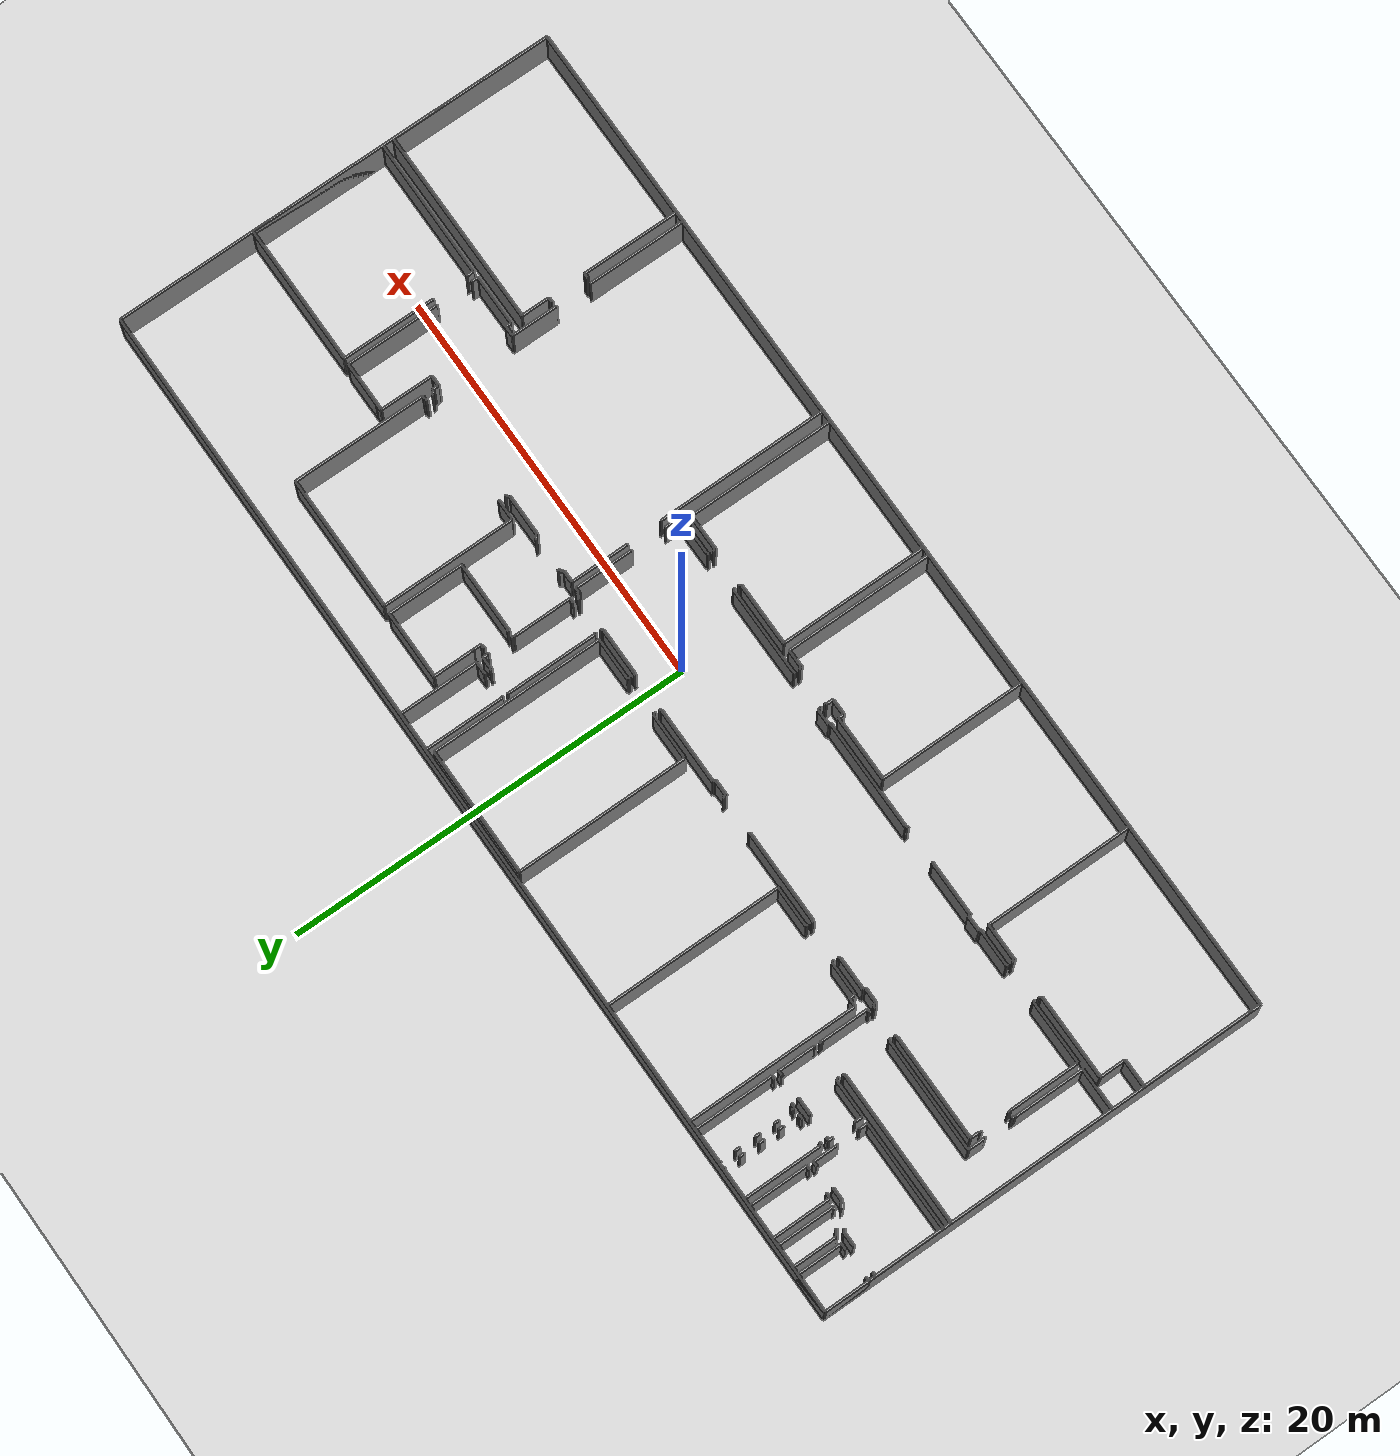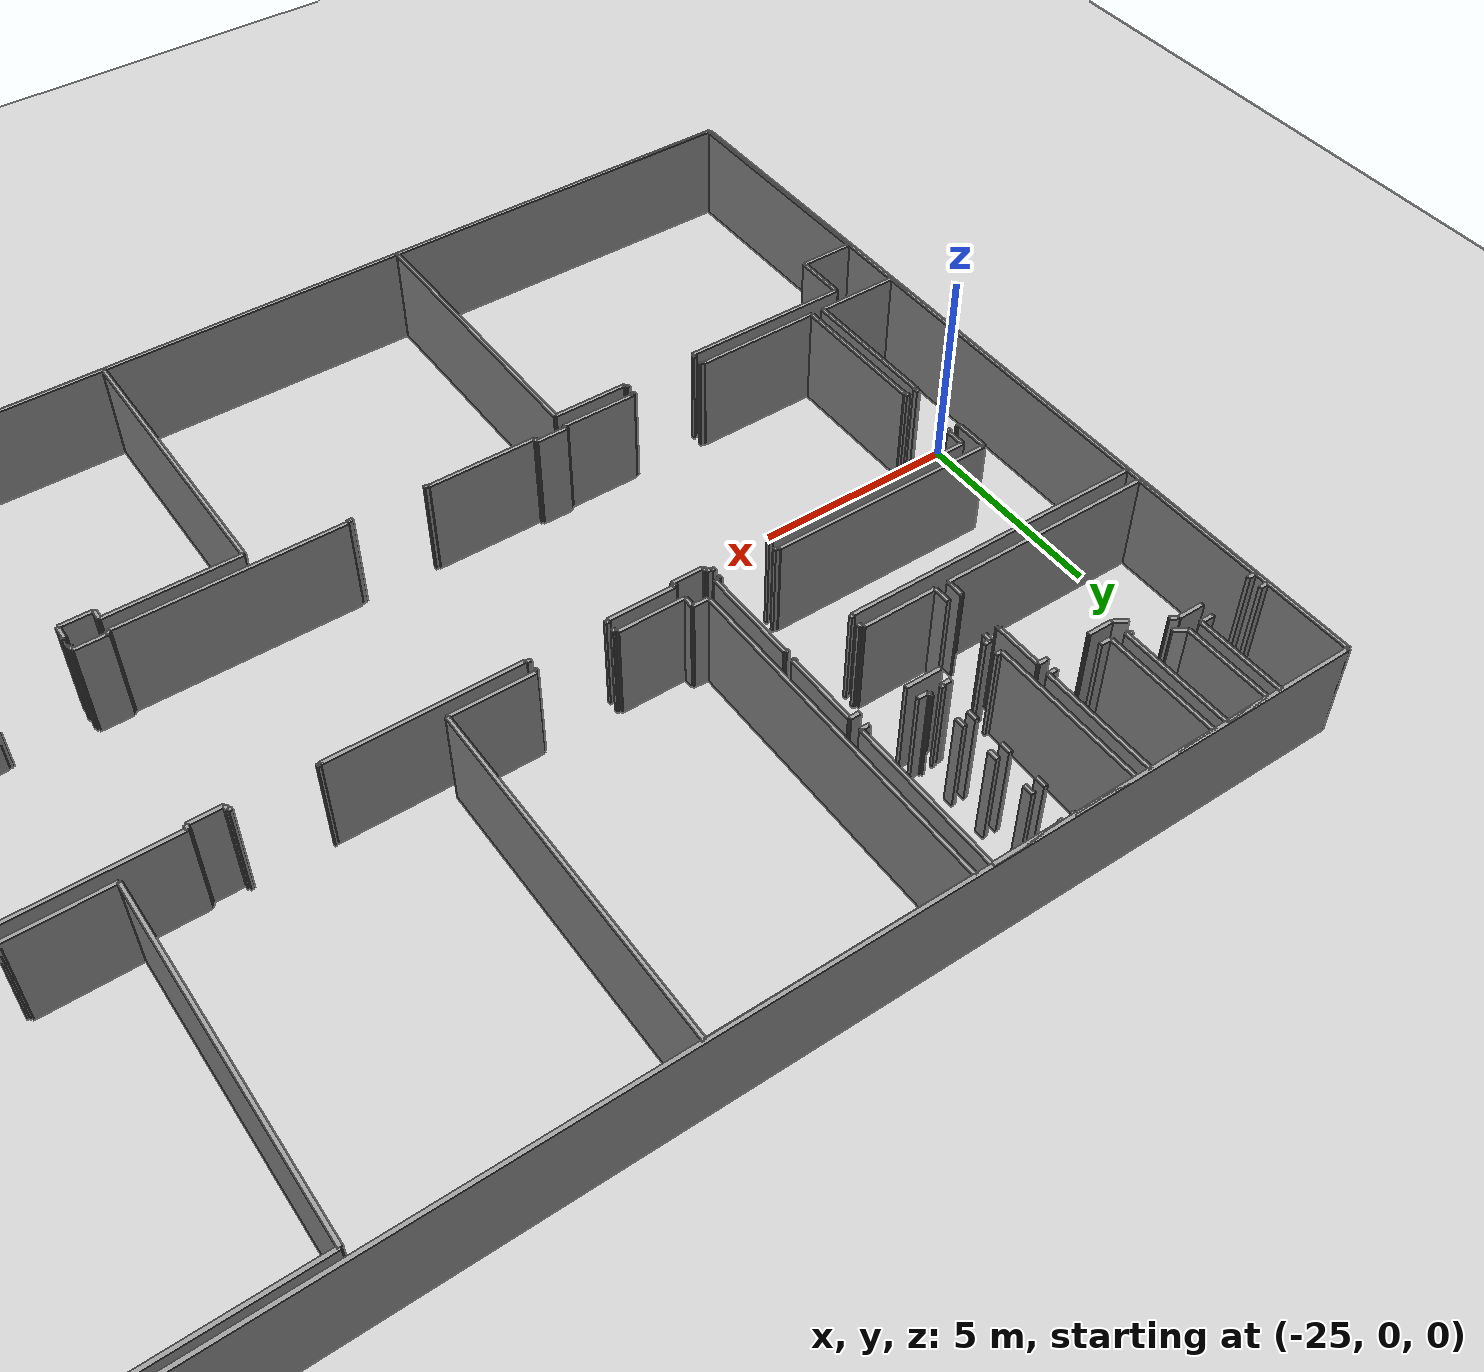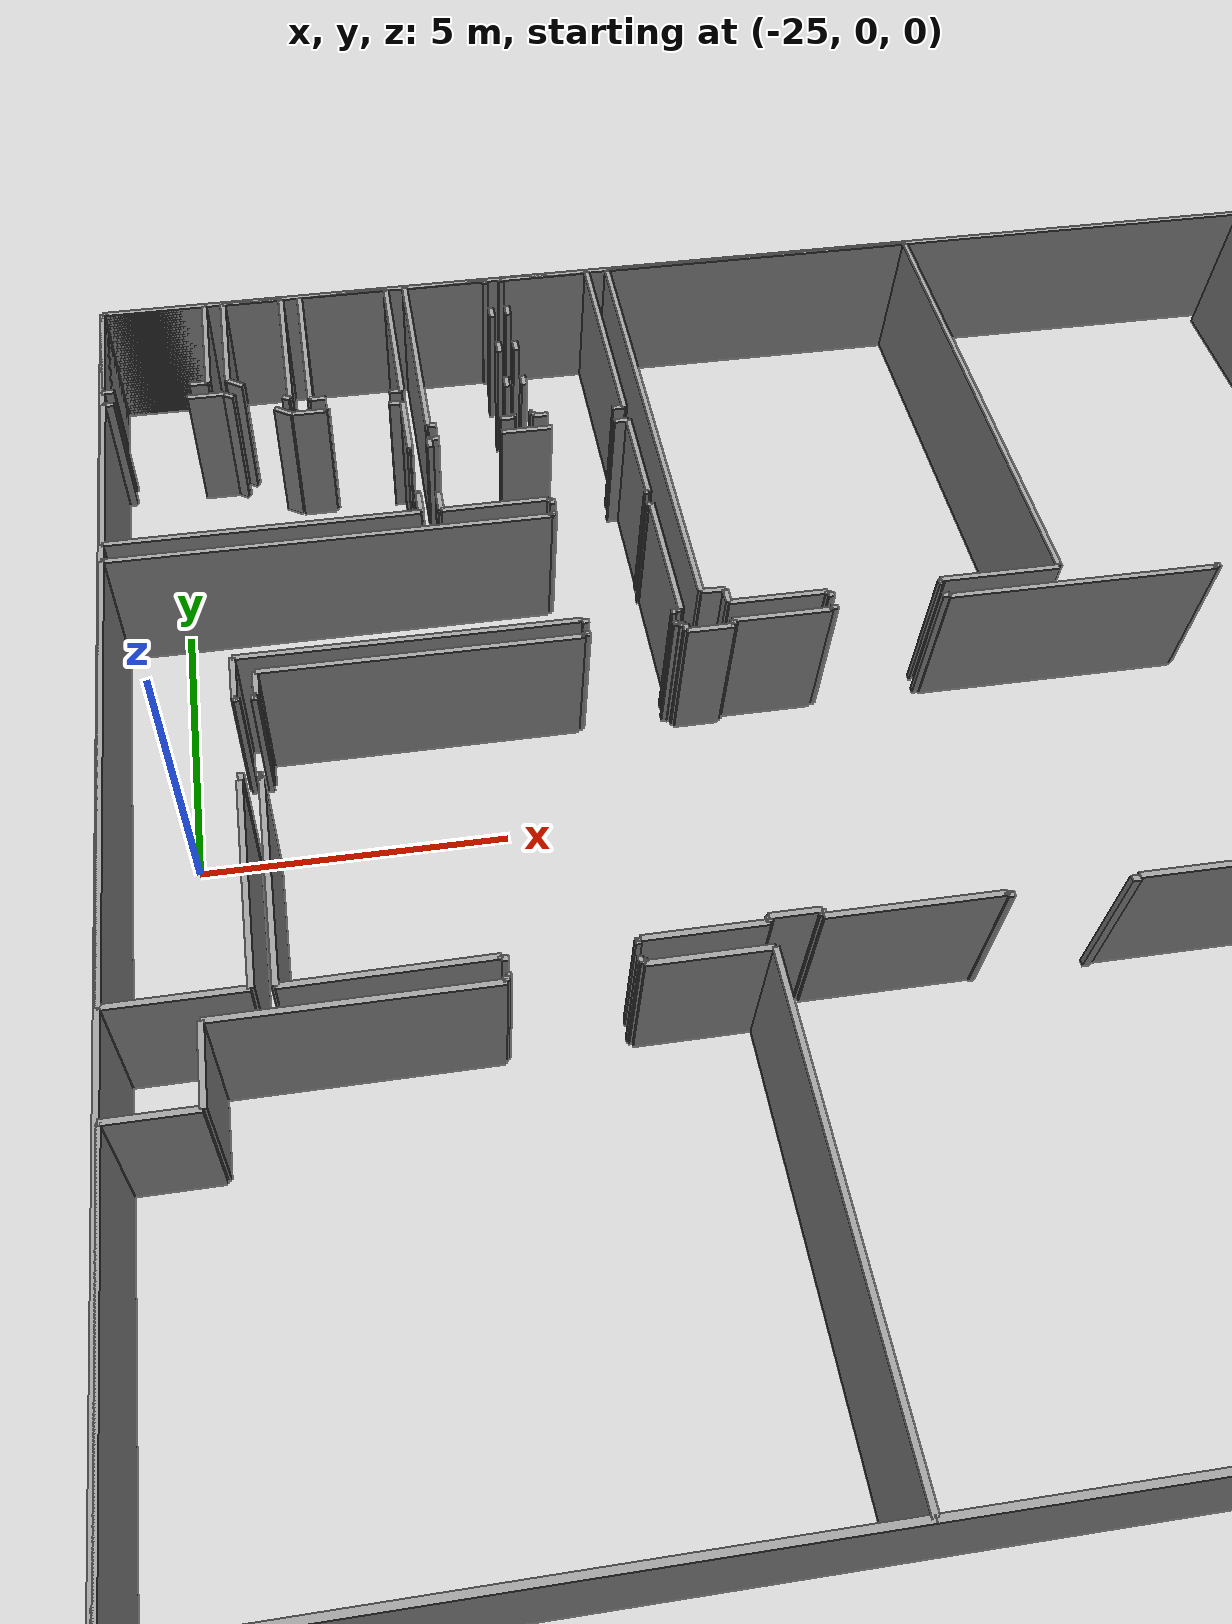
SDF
<sdf version="1.6">
  <world name="default">
    <light name="sun" type="directional">
      <cast_shadows>1</cast_shadows>
      <pose frame="">0 0 10 0 -0 0</pose>
      <diffuse>0.8 0.8 0.8 1</diffuse>
      <specular>0.1 0.1 0.1 1</specular>
      <attenuation>
        <range>1000</range>
        <constant>0.9</constant>
        <linear>0.01</linear>
        <quadratic>0.001</quadratic>
      </attenuation>
      <direction>-0.5 0.5 -1</direction>
    </light>
    <model name="ground_plane">
      <static>1</static>
      <link name="link">
        <collision name="collision">
          <geometry>
            <plane>
              <normal>0 0 1</normal>
              <size>100 100</size>
            </plane>
          </geometry>
          <surface>
            <friction>
              <ode>
                <mu>100</mu>
                <mu2>50</mu2>
              </ode>
              <torsional>
                <ode />
              </torsional>
            </friction>
            <contact>
              <ode />
            </contact>
            <bounce />
          </surface>
          <max_contacts>10</max_contacts>
        </collision>
        <visual name="visual">
          <cast_shadows>0</cast_shadows>
          <geometry>
            <plane>
              <normal>0 0 1</normal>
              <size>100 100</size>
            </plane>
          </geometry>
          <material>
            <script>
              <uri>file://media/materials/scripts/gazebo.material</uri>
              <name>Gazebo/Grey</name>
            </script>
          </material>
        </visual>
        <self_collide>0</self_collide>
        <kinematic>0</kinematic>
        <gravity>1</gravity>
      </link>
    </model>
    <gravity>0 0 -9.8</gravity>
    <magnetic_field>6e-06 2.3e-05 -4.2e-05</magnetic_field>
    <atmosphere type="adiabatic" />
    <physics default="0" name="default_physics" type="ode">
      <max_step_size>0.001</max_step_size>
      <real_time_factor>1</real_time_factor>
      <real_time_update_rate>1000</real_time_update_rate>
    </physics>
    <scene>
      <ambient>0.4 0.4 0.4 1</ambient>
      <background>0.7 0.7 0.7 1</background>
      <shadows>1</shadows>
    </scene>
    <spherical_coordinates>
      <surface_model>EARTH_WGS84</surface_model>
      <latitude_deg>0</latitude_deg>
      <longitude_deg>0</longitude_deg>
      <elevation>0</elevation>
      <heading_deg>0</heading_deg>
    </spherical_coordinates>
  <model name="0510030938_A_40_1_102">
		<static>1</static>
		<link name="Wall_0">
			<collision name="Wall_0_Collision">
				<geometry>
					<box>
						<size>8.27512581973 0.1 2.5</size>
					</box>
				</geometry>
				<pose frame="">4.13756290987 0 1.25 0 0 0</pose>
			</collision>
			<visual name="Wall_0_Visual">
				<pose frame="">4.13756290987 0 1.25 0 0 0</pose>
				<geometry>
					<box>
						<size>8.27512581973 0.1 2.5</size>
					</box>
				</geometry>
				<material>
					<script>
						<uri>file://media/materials/scripts/gazebo.material</uri>
						<name>Gazebo/Grey</name>
					</script>
					<ambient>1 1 1 1</ambient>
				</material>
			</visual>
			<pose frame="">0.00724416653958 -14.7061664379 0 0 0 1.57079632679</pose>
		</link>
		<link name="Wall_1">
			<collision name="Wall_1_Collision">
				<geometry>
					<box>
						<size>7.57650856591 0.1 2.5</size>
					</box>
				</geometry>
				<pose frame="">3.78825428295 0 1.25 0 0 0</pose>
			</collision>
			<visual name="Wall_1_Visual">
				<pose frame="">3.78825428295 0 1.25 0 0 0</pose>
				<geometry>
					<box>
						<size>7.57650856591 0.1 2.5</size>
					</box>
				</geometry>
				<material>
					<script>
						<uri>file://media/materials/scripts/gazebo.material</uri>
						<name>Gazebo/Grey</name>
					</script>
					<ambient>1 1 1 1</ambient>
				</material>
			</visual>
			<pose frame="">0.00724416653958 -6.43104061817 0 0 0 0.0</pose>
		</link>
		<link name="Wall_2">
			<collision name="Wall_2_Collision">
				<geometry>
					<box>
						<size>0.0350770169285 0.1 2.5</size>
					</box>
				</geometry>
				<pose frame="">0.0175385084642 0 1.25 0 0 0</pose>
			</collision>
			<visual name="Wall_2_Visual">
				<pose frame="">0.0175385084642 0 1.25 0 0 0</pose>
				<geometry>
					<box>
						<size>0.0350770169285 0.1 2.5</size>
					</box>
				</geometry>
				<material>
					<script>
						<uri>file://media/materials/scripts/gazebo.material</uri>
						<name>Gazebo/Grey</name>
					</script>
					<ambient>1 1 1 1</ambient>
				</material>
			</visual>
			<pose frame="">7.58375273245 -6.43104061817 0 0 0 1.57079632679</pose>
		</link>
		<link name="Wall_3">
			<collision name="Wall_3_Collision">
				<geometry>
					<box>
						<size>0.0847694575771 0.1 2.5</size>
					</box>
				</geometry>
				<pose frame="">0.0423847287886 0 1.25 0 0 0</pose>
			</collision>
			<visual name="Wall_3_Visual">
				<pose frame="">0.0423847287886 0 1.25 0 0 0</pose>
				<geometry>
					<box>
						<size>0.0847694575771 0.1 2.5</size>
					</box>
				</geometry>
				<material>
					<script>
						<uri>file://media/materials/scripts/gazebo.material</uri>
						<name>Gazebo/Grey</name>
					</script>
					<ambient>1 1 1 1</ambient>
				</material>
			</visual>
			<pose frame="">7.58375273245 -6.39596360124 0 0 0 0.0</pose>
		</link>
		<link name="Wall_4">
			<collision name="Wall_4_Collision">
				<geometry>
					<box>
						<size>0.0874383610391 0.1 2.5</size>
					</box>
				</geometry>
				<pose frame="">0.0437191805195 0 1.25 0 0 0</pose>
			</collision>
			<visual name="Wall_4_Visual">
				<pose frame="">0.0437191805195 0 1.25 0 0 0</pose>
				<geometry>
					<box>
						<size>0.0874383610391 0.1 2.5</size>
					</box>
				</geometry>
				<material>
					<script>
						<uri>file://media/materials/scripts/gazebo.material</uri>
						<name>Gazebo/Grey</name>
					</script>
					<ambient>1 1 1 1</ambient>
				</material>
			</visual>
			<pose frame="">9.22500127091 -6.39596360124 0 0 0 0.0</pose>
		</link>
		<link name="Wall_5">
			<collision name="Wall_5_Collision">
				<geometry>
					<box>
						<size>2.42018707742 0.1 2.5</size>
					</box>
				</geometry>
				<pose frame="">1.21009353871 0 1.25 0 0 0</pose>
			</collision>
			<visual name="Wall_5_Visual">
				<pose frame="">1.21009353871 0 1.25 0 0 0</pose>
				<geometry>
					<box>
						<size>2.42018707742 0.1 2.5</size>
					</box>
				</geometry>
				<material>
					<script>
						<uri>file://media/materials/scripts/gazebo.material</uri>
						<name>Gazebo/Grey</name>
					</script>
					<ambient>1 1 1 1</ambient>
				</material>
			</visual>
			<pose frame="">9.31243963195 -6.39596360124 0 0 0 -1.57079632679</pose>
		</link>
		<link name="Wall_6">
			<collision name="Wall_6_Collision">
				<geometry>
					<box>
						<size>0.0915052615525 0.1 2.5</size>
					</box>
				</geometry>
				<pose frame="">0.0457526307763 0 1.25 0 0 0</pose>
			</collision>
			<visual name="Wall_6_Visual">
				<pose frame="">0.0457526307763 0 1.25 0 0 0</pose>
				<geometry>
					<box>
						<size>0.0915052615525 0.1 2.5</size>
					</box>
				</geometry>
				<material>
					<script>
						<uri>file://media/materials/scripts/gazebo.material</uri>
						<name>Gazebo/Grey</name>
					</script>
					<ambient>1 1 1 1</ambient>
				</material>
			</visual>
			<pose frame="">9.31243963195 -8.81615067866 0 0 0 3.14159265359</pose>
		</link>
		<link name="Wall_7">
			<collision name="Wall_7_Collision">
				<geometry>
					<box>
						<size>0.031010116415 0.1 2.5</size>
					</box>
				</geometry>
				<pose frame="">0.0155050582075 0 1.25 0 0 0</pose>
			</collision>
			<visual name="Wall_7_Visual">
				<pose frame="">0.0155050582075 0 1.25 0 0 0</pose>
				<geometry>
					<box>
						<size>0.031010116415 0.1 2.5</size>
					</box>
				</geometry>
				<material>
					<script>
						<uri>file://media/materials/scripts/gazebo.material</uri>
						<name>Gazebo/Grey</name>
					</script>
					<ambient>1 1 1 1</ambient>
				</material>
			</visual>
			<pose frame="">9.22093437039 -8.81615067866 0 0 0 -1.57079632679</pose>
		</link>
		<link name="Wall_8">
			<collision name="Wall_8_Collision">
				<geometry>
					<box>
						<size>0.070281124498 0.1 2.5</size>
					</box>
				</geometry>
				<pose frame="">0.035140562249 0 1.25 0 0 0</pose>
			</collision>
			<visual name="Wall_8_Visual">
				<pose frame="">0.035140562249 0 1.25 0 0 0</pose>
				<geometry>
					<box>
						<size>0.070281124498 0.1 2.5</size>
					</box>
				</geometry>
				<material>
					<script>
						<uri>file://media/materials/scripts/gazebo.material</uri>
						<name>Gazebo/Grey</name>
					</script>
					<ambient>1 1 1 1</ambient>
				</material>
			</visual>
			<pose frame="">9.22093437039 -8.84716079508 0 0 0 3.14159265359</pose>
		</link>
		<link name="Wall_9">
			<collision name="Wall_9_Collision">
				<geometry>
					<box>
						<size>0.108408316812 0.1 2.5</size>
					</box>
				</geometry>
				<pose frame="">0.0542041584058 0 1.25 0 0 0</pose>
			</collision>
			<visual name="Wall_9_Visual">
				<pose frame="">0.0542041584058 0 1.25 0 0 0</pose>
				<geometry>
					<box>
						<size>0.108408316812 0.1 2.5</size>
					</box>
				</geometry>
				<material>
					<script>
						<uri>file://media/materials/scripts/gazebo.material</uri>
						<name>Gazebo/Grey</name>
					</script>
					<ambient>1 1 1 1</ambient>
				</material>
			</visual>
			<pose frame="">7.79027502415 -8.84716079508 0 0 0 3.14159265359</pose>
		</link>
		<link name="Wall_10">
			<collision name="Wall_10_Collision">
				<geometry>
					<box>
						<size>0.0318997509023 0.1 2.5</size>
					</box>
				</geometry>
				<pose frame="">0.0159498754512 0 1.25 0 0 0</pose>
			</collision>
			<visual name="Wall_10_Visual">
				<pose frame="">0.0159498754512 0 1.25 0 0 0</pose>
				<geometry>
					<box>
						<size>0.0318997509023 0.1 2.5</size>
					</box>
				</geometry>
				<material>
					<script>
						<uri>file://media/materials/scripts/gazebo.material</uri>
						<name>Gazebo/Grey</name>
					</script>
					<ambient>1 1 1 1</ambient>
				</material>
			</visual>
			<pose frame="">7.68186670734 -8.84716079508 0 0 0 1.57079632679</pose>
		</link>
		<link name="Wall_11">
			<collision name="Wall_11_Collision">
				<geometry>
					<box>
						<size>5.61016216766 0.1 2.5</size>
					</box>
				</geometry>
				<pose frame="">2.80508108383 0 1.25 0 0 0</pose>
			</collision>
			<visual name="Wall_11_Visual">
				<pose frame="">2.80508108383 0 1.25 0 0 0</pose>
				<geometry>
					<box>
						<size>5.61016216766 0.1 2.5</size>
					</box>
				</geometry>
				<material>
					<script>
						<uri>file://media/materials/scripts/gazebo.material</uri>
						<name>Gazebo/Grey</name>
					</script>
					<ambient>1 1 1 1</ambient>
				</material>
			</visual>
			<pose frame="">7.68186670734 -8.81526104418 0 0 0 3.14159265359</pose>
		</link>
		<link name="Wall_12">
			<collision name="Wall_12_Collision">
				<geometry>
					<box>
						<size>0.824691169742 0.1 2.5</size>
					</box>
				</geometry>
				<pose frame="">0.412345584871 0 1.25 0 0 0</pose>
			</collision>
			<visual name="Wall_12_Visual">
				<pose frame="">0.412345584871 0 1.25 0 0 0</pose>
				<geometry>
					<box>
						<size>0.824691169742 0.1 2.5</size>
					</box>
				</geometry>
				<material>
					<script>
						<uri>file://media/materials/scripts/gazebo.material</uri>
						<name>Gazebo/Grey</name>
					</script>
					<ambient>1 1 1 1</ambient>
				</material>
			</visual>
			<pose frame="">2.07170453968 -8.81526104418 0 0 0 -1.57079632679</pose>
		</link>
		<link name="Wall_13">
			<collision name="Wall_13_Collision">
				<geometry>
					<box>
						<size>0.0330435666718 0.1 2.5</size>
					</box>
				</geometry>
				<pose frame="">0.0165217833359 0 1.25 0 0 0</pose>
			</collision>
			<visual name="Wall_13_Visual">
				<pose frame="">0.0165217833359 0 1.25 0 0 0</pose>
				<geometry>
					<box>
						<size>0.0330435666718 0.1 2.5</size>
					</box>
				</geometry>
				<material>
					<script>
						<uri>file://media/materials/scripts/gazebo.material</uri>
						<name>Gazebo/Grey</name>
					</script>
					<ambient>1 1 1 1</ambient>
				</material>
			</visual>
			<pose frame="">2.07170453968 -9.63995221392 0 0 0 0.0</pose>
		</link>
		<link name="Wall_14">
			<collision name="Wall_14_Collision">
				<geometry>
					<box>
						<size>0.0660871333435 0.1 2.5</size>
					</box>
				</geometry>
				<pose frame="">0.0330435666718 0 1.25 0 0 0</pose>
			</collision>
			<visual name="Wall_14_Visual">
				<pose frame="">0.0330435666718 0 1.25 0 0 0</pose>
				<geometry>
					<box>
						<size>0.0660871333435 0.1 2.5</size>
					</box>
				</geometry>
				<material>
					<script>
						<uri>file://media/materials/scripts/gazebo.material</uri>
						<name>Gazebo/Grey</name>
					</script>
					<ambient>1 1 1 1</ambient>
				</material>
			</visual>
			<pose frame="">2.10474810635 -9.63995221392 0 0 0 -1.57079632679</pose>
		</link>
		<link name="Wall_15">
			<collision name="Wall_15_Collision">
				<geometry>
					<box>
						<size>0.133953535662 0.1 2.5</size>
					</box>
				</geometry>
				<pose frame="">0.0669767678308 0 1.25 0 0 0</pose>
			</collision>
			<visual name="Wall_15_Visual">
				<pose frame="">0.0669767678308 0 1.25 0 0 0</pose>
				<geometry>
					<box>
						<size>0.133953535662 0.1 2.5</size>
					</box>
				</geometry>
				<material>
					<script>
						<uri>file://media/materials/scripts/gazebo.material</uri>
						<name>Gazebo/Grey</name>
					</script>
					<ambient>1 1 1 1</ambient>
				</material>
			</visual>
			<pose frame="">2.10474810635 -11.0726450104 0 0 0 -1.57079632679</pose>
		</link>
		<link name="Wall_16">
			<collision name="Wall_16_Collision">
				<geometry>
					<box>
						<size>0.025418128209 0.1 2.5</size>
					</box>
				</geometry>
				<pose frame="">0.0127090641045 0 1.25 0 0 0</pose>
			</collision>
			<visual name="Wall_16_Visual">
				<pose frame="">0.0127090641045 0 1.25 0 0 0</pose>
				<geometry>
					<box>
						<size>0.025418128209 0.1 2.5</size>
					</box>
				</geometry>
				<material>
					<script>
						<uri>file://media/materials/scripts/gazebo.material</uri>
						<name>Gazebo/Grey</name>
					</script>
					<ambient>1 1 1 1</ambient>
				</material>
			</visual>
			<pose frame="">2.10474810635 -11.2065985461 0 0 0 3.14159265359</pose>
		</link>
		<link name="Wall_17">
			<collision name="Wall_17_Collision">
				<geometry>
					<box>
						<size>3.49651771644 0.1 2.5</size>
					</box>
				</geometry>
				<pose frame="">1.74825885822 0 1.25 0 0 0</pose>
			</collision>
			<visual name="Wall_17_Visual">
				<pose frame="">1.74825885822 0 1.25 0 0 0</pose>
				<geometry>
					<box>
						<size>3.49651771644 0.1 2.5</size>
					</box>
				</geometry>
				<material>
					<script>
						<uri>file://media/materials/scripts/gazebo.material</uri>
						<name>Gazebo/Grey</name>
					</script>
					<ambient>1 1 1 1</ambient>
				</material>
			</visual>
			<pose frame="">2.07932997814 -11.2065985461 0 0 0 -1.57079632679</pose>
		</link>
		<link name="Wall_18">
			<collision name="Wall_18_Collision">
				<geometry>
					<box>
						<size>2.07208805658 0.1 2.5</size>
					</box>
				</geometry>
				<pose frame="">1.03604402829 0 1.25 0 0 0</pose>
			</collision>
			<visual name="Wall_18_Visual">
				<pose frame="">1.03604402829 0 1.25 0 0 0</pose>
				<geometry>
					<box>
						<size>2.07208805658 0.1 2.5</size>
					</box>
				</geometry>
				<material>
					<script>
						<uri>file://media/materials/scripts/gazebo.material</uri>
						<name>Gazebo/Grey</name>
					</script>
					<ambient>1 1 1 1</ambient>
				</material>
			</visual>
			<pose frame="">2.07932997814 -14.7031162625 0 0 0 -3.14012062325</pose>
		</link>
		<link name="Wall_19">
			<collision name="Wall_19_Collision">
				<geometry>
					<box>
						<size>0.436047989426 0.1 2.5</size>
					</box>
				</geometry>
				<pose frame="">0.218023994713 0 1.25 0 0 0</pose>
			</collision>
			<visual name="Wall_19_Visual">
				<pose frame="">0.218023994713 0 1.25 0 0 0</pose>
				<geometry>
					<box>
						<size>0.436047989426 0.1 2.5</size>
					</box>
				</geometry>
				<material>
					<script>
						<uri>file://media/materials/scripts/gazebo.material</uri>
						<name>Gazebo/Grey</name>
					</script>
					<ambient>1 1 1 1</ambient>
				</material>
			</visual>
			<pose frame="">5.7366173555 -6.04138071272 0 0 0 1.57079632679</pose>
		</link>
		<link name="Wall_20">
			<collision name="Wall_20_Collision">
				<geometry>
					<box>
						<size>0.213131005033 0.1 2.5</size>
					</box>
				</geometry>
				<pose frame="">0.106565502516 0 1.25 0 0 0</pose>
			</collision>
			<visual name="Wall_20_Visual">
				<pose frame="">0.106565502516 0 1.25 0 0 0</pose>
				<geometry>
					<box>
						<size>0.213131005033 0.1 2.5</size>
					</box>
				</geometry>
				<material>
					<script>
						<uri>file://media/materials/scripts/gazebo.material</uri>
						<name>Gazebo/Grey</name>
					</script>
					<ambient>1 1 1 1</ambient>
				</material>
			</visual>
			<pose frame="">5.7366173555 -4.48731635402 0 0 0 1.57079632679</pose>
		</link>
		<link name="Wall_21">
			<collision name="Wall_21_Collision">
				<geometry>
					<box>
						<size>0.17144527477 0.1 2.5</size>
					</box>
				</geometry>
				<pose frame="">0.085722637385 0 1.25 0 0 0</pose>
			</collision>
			<visual name="Wall_21_Visual">
				<pose frame="">0.085722637385 0 1.25 0 0 0</pose>
				<geometry>
					<box>
						<size>0.17144527477 0.1 2.5</size>
					</box>
				</geometry>
				<material>
					<script>
						<uri>file://media/materials/scripts/gazebo.material</uri>
						<name>Gazebo/Grey</name>
					</script>
					<ambient>1 1 1 1</ambient>
				</material>
			</visual>
			<pose frame="">5.7366173555 -4.27418534899 0 0 0 0.0</pose>
		</link>
		<link name="Wall_22">
			<collision name="Wall_22_Collision">
				<geometry>
					<box>
						<size>0.904758273601 0.1 2.5</size>
					</box>
				</geometry>
				<pose frame="">0.4523791368 0 1.25 0 0 0</pose>
			</collision>
			<visual name="Wall_22_Visual">
				<pose frame="">0.4523791368 0 1.25 0 0 0</pose>
				<geometry>
					<box>
						<size>0.904758273601 0.1 2.5</size>
					</box>
				</geometry>
				<material>
					<script>
						<uri>file://media/materials/scripts/gazebo.material</uri>
						<name>Gazebo/Grey</name>
					</script>
					<ambient>1 1 1 1</ambient>
				</material>
			</visual>
			<pose frame="">7.02951044685 -4.27418534899 0 0 0 0.0</pose>
		</link>
		<link name="Wall_23">
			<collision name="Wall_23_Collision">
				<geometry>
					<box>
						<size>0.254435463372 0.1 2.5</size>
					</box>
				</geometry>
				<pose frame="">0.127217731686 0 1.25 0 0 0</pose>
			</collision>
			<visual name="Wall_23_Visual">
				<pose frame="">0.127217731686 0 1.25 0 0 0</pose>
				<geometry>
					<box>
						<size>0.254435463372 0.1 2.5</size>
					</box>
				</geometry>
				<material>
					<script>
						<uri>file://media/materials/scripts/gazebo.material</uri>
						<name>Gazebo/Grey</name>
					</script>
					<ambient>1 1 1 1</ambient>
				</material>
			</visual>
			<pose frame="">9.06524833511 -4.27418534899 0 0 0 0.0</pose>
		</link>
		<link name="Wall_24">
			<collision name="Wall_24_Collision">
				<geometry>
					<box>
						<size>1.84039957298 0.1 2.5</size>
					</box>
				</geometry>
				<pose frame="">0.920199786488 0 1.25 0 0 0</pose>
			</collision>
			<visual name="Wall_24_Visual">
				<pose frame="">0.920199786488 0 1.25 0 0 0</pose>
				<geometry>
					<box>
						<size>1.84039957298 0.1 2.5</size>
					</box>
				</geometry>
				<material>
					<script>
						<uri>file://media/materials/scripts/gazebo.material</uri>
						<name>Gazebo/Grey</name>
					</script>
					<ambient>1 1 1 1</ambient>
				</material>
			</visual>
			<pose frame="">9.31968379849 -4.27418534899 0 0 0 -1.57079632679</pose>
		</link>
		<link name="Wall_25">
			<collision name="Wall_25_Collision">
				<geometry>
					<box>
						<size>0.0721874841137 0.1 2.5</size>
					</box>
				</geometry>
				<pose frame="">0.0360937420568 0 1.25 0 0 0</pose>
			</collision>
			<visual name="Wall_25_Visual">
				<pose frame="">0.0360937420568 0 1.25 0 0 0</pose>
				<geometry>
					<box>
						<size>0.0721874841137 0.1 2.5</size>
					</box>
				</geometry>
				<material>
					<script>
						<uri>file://media/materials/scripts/gazebo.material</uri>
						<name>Gazebo/Grey</name>
					</script>
					<ambient>1 1 1 1</ambient>
				</material>
			</visual>
			<pose frame="">9.31968379849 -6.11458492197 0 0 0 3.14159265359</pose>
		</link>
		<link name="Wall_26">
			<collision name="Wall_26_Collision">
				<geometry>
					<box>
						<size>0.0908698083473 0.1 2.5</size>
					</box>
				</geometry>
				<pose frame="">0.0454349041737 0 1.25 0 0 0</pose>
			</collision>
			<visual name="Wall_26_Visual">
				<pose frame="">0.0454349041737 0 1.25 0 0 0</pose>
				<geometry>
					<box>
						<size>0.0908698083473 0.1 2.5</size>
					</box>
				</geometry>
				<material>
					<script>
						<uri>file://media/materials/scripts/gazebo.material</uri>
						<name>Gazebo/Grey</name>
					</script>
					<ambient>1 1 1 1</ambient>
				</material>
			</visual>
			<pose frame="">7.69241523054 -6.11458492197 0 0 0 3.14159265359</pose>
		</link>
		<link name="Wall_27">
			<collision name="Wall_27_Collision">
				<geometry>
					<box>
						<size>0.0828630979615 0.1 2.5</size>
					</box>
				</geometry>
				<pose frame="">0.0414315489807 0 1.25 0 0 0</pose>
			</collision>
			<visual name="Wall_27_Visual">
				<pose frame="">0.0414315489807 0 1.25 0 0 0</pose>
				<geometry>
					<box>
						<size>0.0828630979615 0.1 2.5</size>
					</box>
				</geometry>
				<material>
					<script>
						<uri>file://media/materials/scripts/gazebo.material</uri>
						<name>Gazebo/Grey</name>
					</script>
					<ambient>1 1 1 1</ambient>
				</material>
			</visual>
			<pose frame="">7.6015454222 -6.11458492197 0 0 0 1.57079632679</pose>
		</link>
		<link name="Wall_28">
			<collision name="Wall_28_Collision">
				<geometry>
					<box>
						<size>1.86495307933 0.1 2.5</size>
					</box>
				</geometry>
				<pose frame="">0.932476539663 0 1.25 0 0 0</pose>
			</collision>
			<visual name="Wall_28_Visual">
				<pose frame="">0.932476539663 0 1.25 0 0 0</pose>
				<geometry>
					<box>
						<size>1.86495307933 0.1 2.5</size>
					</box>
				</geometry>
				<material>
					<script>
						<uri>file://media/materials/scripts/gazebo.material</uri>
						<name>Gazebo/Grey</name>
					</script>
					<ambient>1 1 1 1</ambient>
				</material>
			</visual>
			<pose frame="">7.6015454222 -6.031721824 0 0 0 -3.13641347133</pose>
		</link>
		<link name="Wall_29">
			<collision name="Wall_29_Collision">
				<geometry>
					<box>
						<size>3.47059122566 0.1 2.5</size>
					</box>
				</geometry>
				<pose frame="">1.73529561283 0 1.25 0 0 0</pose>
			</collision>
			<visual name="Wall_29_Visual">
				<pose frame="">1.73529561283 0 1.25 0 0 0</pose>
				<geometry>
					<box>
						<size>3.47059122566 0.1 2.5</size>
					</box>
				</geometry>
				<material>
					<script>
						<uri>file://media/materials/scripts/gazebo.material</uri>
						<name>Gazebo/Grey</name>
					</script>
					<ambient>1 1 1 1</ambient>
				</material>
			</visual>
			<pose frame="">0.016775964618 -6.04112653144 0 0 0 1.57079632679</pose>
		</link>
		<link name="Wall_30">
			<collision name="Wall_30_Collision">
				<geometry>
					<box>
						<size>0.20067612221 0.1 2.5</size>
					</box>
				</geometry>
				<pose frame="">0.100338061105 0 1.25 0 0 0</pose>
			</collision>
			<visual name="Wall_30_Visual">
				<pose frame="">0.100338061105 0 1.25 0 0 0</pose>
				<geometry>
					<box>
						<size>0.20067612221 0.1 2.5</size>
					</box>
				</geometry>
				<material>
					<script>
						<uri>file://media/materials/scripts/gazebo.material</uri>
						<name>Gazebo/Grey</name>
					</script>
					<ambient>1 1 1 1</ambient>
				</material>
			</visual>
			<pose frame="">0.016775964618 -2.57053530578 0 0 0 0.0</pose>
		</link>
		<link name="Wall_31">
			<collision name="Wall_31_Collision">
				<geometry>
					<box>
						<size>0.654516801383 0.1 2.5</size>
					</box>
				</geometry>
				<pose frame="">0.327258400691 0 1.25 0 0 0</pose>
			</collision>
			<visual name="Wall_31_Visual">
				<pose frame="">0.327258400691 0 1.25 0 0 0</pose>
				<geometry>
					<box>
						<size>0.654516801383 0.1 2.5</size>
					</box>
				</geometry>
				<material>
					<script>
						<uri>file://media/materials/scripts/gazebo.material</uri>
						<name>Gazebo/Grey</name>
					</script>
					<ambient>1 1 1 1</ambient>
				</material>
			</visual>
			<pose frame="">1.53144222459 -2.57053530578 0 0 0 0.0</pose>
		</link>
		<link name="Wall_32">
			<collision name="Wall_32_Collision">
				<geometry>
					<box>
						<size>0.209723164445 0.1 2.5</size>
					</box>
				</geometry>
				<pose frame="">0.104861582223 0 1.25 0 0 0</pose>
			</collision>
			<visual name="Wall_32_Visual">
				<pose frame="">0.104861582223 0 1.25 0 0 0</pose>
				<geometry>
					<box>
						<size>0.209723164445 0.1 2.5</size>
					</box>
				</geometry>
				<material>
					<script>
						<uri>file://media/materials/scripts/gazebo.material</uri>
						<name>Gazebo/Grey</name>
					</script>
					<ambient>1 1 1 1</ambient>
				</material>
			</visual>
			<pose frame="">2.18595902598 -2.57053530578 0 0 0 -0.524933782635</pose>
		</link>
		<link name="Wall_33">
			<collision name="Wall_33_Collision">
				<geometry>
					<box>
						<size>0.343461699112 0.1 2.5</size>
					</box>
				</geometry>
				<pose frame="">0.171730849556 0 1.25 0 0 0</pose>
			</collision>
			<visual name="Wall_33_Visual">
				<pose frame="">0.171730849556 0 1.25 0 0 0</pose>
				<geometry>
					<box>
						<size>0.343461699112 0.1 2.5</size>
					</box>
				</geometry>
				<material>
					<script>
						<uri>file://media/materials/scripts/gazebo.material</uri>
						<name>Gazebo/Grey</name>
					</script>
					<ambient>1 1 1 1</ambient>
				</material>
			</visual>
			<pose frame="">3.08868384932 -3.0904631183 0 0 0 -0.563266863326</pose>
		</link>
		<link name="Wall_34">
			<collision name="Wall_34_Collision">
				<geometry>
					<box>
						<size>0.625158863301 0.1 2.5</size>
					</box>
				</geometry>
				<pose frame="">0.312579431651 0 1.25 0 0 0</pose>
			</collision>
			<visual name="Wall_34_Visual">
				<pose frame="">0.312579431651 0 1.25 0 0 0</pose>
				<geometry>
					<box>
						<size>0.625158863301 0.1 2.5</size>
					</box>
				</geometry>
				<material>
					<script>
						<uri>file://media/materials/scripts/gazebo.material</uri>
						<name>Gazebo/Grey</name>
					</script>
					<ambient>1 1 1 1</ambient>
				</material>
			</visual>
			<pose frame="">3.37908596411 -3.27385491332 0 0 0 0.0</pose>
		</link>
		<link name="Wall_35">
			<collision name="Wall_35_Collision">
				<geometry>
					<box>
						<size>0.0219866809008 0.1 2.5</size>
					</box>
				</geometry>
				<pose frame="">0.0109933404504 0 1.25 0 0 0</pose>
			</collision>
			<visual name="Wall_35_Visual">
				<pose frame="">0.0109933404504 0 1.25 0 0 0</pose>
				<geometry>
					<box>
						<size>0.0219866809008 0.1 2.5</size>
					</box>
				</geometry>
				<material>
					<script>
						<uri>file://media/materials/scripts/gazebo.material</uri>
						<name>Gazebo/Grey</name>
					</script>
					<ambient>1 1 1 1</ambient>
				</material>
			</visual>
			<pose frame="">4.00424482741 -3.27385491332 0 0 0 1.57079632679</pose>
		</link>
		<link name="Wall_36">
			<collision name="Wall_36_Collision">
				<geometry>
					<box>
						<size>0.245793299781 0.1 2.5</size>
					</box>
				</geometry>
				<pose frame="">0.122896649891 0 1.25 0 0 0</pose>
			</collision>
			<visual name="Wall_36_Visual">
				<pose frame="">0.122896649891 0 1.25 0 0 0</pose>
				<geometry>
					<box>
						<size>0.245793299781 0.1 2.5</size>
					</box>
				</geometry>
				<material>
					<script>
						<uri>file://media/materials/scripts/gazebo.material</uri>
						<name>Gazebo/Grey</name>
					</script>
					<ambient>1 1 1 1</ambient>
				</material>
			</visual>
			<pose frame="">5.12899700066 -3.25186823242 0 0 0 0.0</pose>
		</link>
		<link name="Wall_37">
			<collision name="Wall_37_Collision">
				<geometry>
					<box>
						<size>1.20647145544 0.1 2.5</size>
					</box>
				</geometry>
				<pose frame="">0.603235727721 0 1.25 0 0 0</pose>
			</collision>
			<visual name="Wall_37_Visual">
				<pose frame="">0.603235727721 0 1.25 0 0 0</pose>
				<geometry>
					<box>
						<size>1.20647145544 0.1 2.5</size>
					</box>
				</geometry>
				<material>
					<script>
						<uri>file://media/materials/scripts/gazebo.material</uri>
						<name>Gazebo/Grey</name>
					</script>
					<ambient>1 1 1 1</ambient>
				</material>
			</visual>
			<pose frame="">5.37479030044 -3.25186823242 0 0 0 -1.57079632679</pose>
		</link>
		<link name="Wall_38">
			<collision name="Wall_38_Collision">
				<geometry>
					<box>
						<size>0.0491840780845 0.1 2.5</size>
					</box>
				</geometry>
				<pose frame="">0.0245920390422 0 1.25 0 0 0</pose>
			</collision>
			<visual name="Wall_38_Visual">
				<pose frame="">0.0245920390422 0 1.25 0 0 0</pose>
				<geometry>
					<box>
						<size>0.0491840780845 0.1 2.5</size>
					</box>
				</geometry>
				<material>
					<script>
						<uri>file://media/materials/scripts/gazebo.material</uri>
						<name>Gazebo/Grey</name>
					</script>
					<ambient>1 1 1 1</ambient>
				</material>
			</visual>
			<pose frame="">5.37479030044 -4.45833968787 0 0 0 0.0</pose>
		</link>
		<link name="Wall_39">
			<collision name="Wall_39_Collision">
				<geometry>
					<box>
						<size>0.0334248385949 0.1 2.5</size>
					</box>
				</geometry>
				<pose frame="">0.0167124192974 0 1.25 0 0 0</pose>
			</collision>
			<visual name="Wall_39_Visual">
				<pose frame="">0.0167124192974 0 1.25 0 0 0</pose>
				<geometry>
					<box>
						<size>0.0334248385949 0.1 2.5</size>
					</box>
				</geometry>
				<material>
					<script>
						<uri>file://media/materials/scripts/gazebo.material</uri>
						<name>Gazebo/Grey</name>
					</script>
					<ambient>1 1 1 1</ambient>
				</material>
			</visual>
			<pose frame="">5.42397437853 -5.59008184637 0 0 0 3.14159265359</pose>
		</link>
		<link name="Wall_40">
			<collision name="Wall_40_Collision">
				<geometry>
					<box>
						<size>0.445452696863 0.1 2.5</size>
					</box>
				</geometry>
				<pose frame="">0.222726348432 0 1.25 0 0 0</pose>
			</collision>
			<visual name="Wall_40_Visual">
				<pose frame="">0.222726348432 0 1.25 0 0 0</pose>
				<geometry>
					<box>
						<size>0.445452696863 0.1 2.5</size>
					</box>
				</geometry>
				<material>
					<script>
						<uri>file://media/materials/scripts/gazebo.material</uri>
						<name>Gazebo/Grey</name>
					</script>
					<ambient>1 1 1 1</ambient>
				</material>
			</visual>
			<pose frame="">5.39054953993 -5.59008184637 0 0 0 -1.57079632679</pose>
		</link>
		<link name="Wall_41">
			<collision name="Wall_41_Collision">
				<geometry>
					<box>
						<size>5.37377648485 0.1 2.5</size>
					</box>
				</geometry>
				<pose frame="">2.68688824242 0 1.25 0 0 0</pose>
			</collision>
			<visual name="Wall_41_Visual">
				<pose frame="">2.68688824242 0 1.25 0 0 0</pose>
				<geometry>
					<box>
						<size>5.37377648485 0.1 2.5</size>
					</box>
				</geometry>
				<material>
					<script>
						<uri>file://media/materials/scripts/gazebo.material</uri>
						<name>Gazebo/Grey</name>
					</script>
					<ambient>1 1 1 1</ambient>
				</material>
			</visual>
			<pose frame="">5.39054953993 -6.03553454324 0 0 0 -3.14055204663</pose>
		</link>
		<link name="Wall_42">
			<collision name="Wall_42_Collision">
				<geometry>
					<box>
						<size>2.23044075034 0.1 2.5</size>
					</box>
				</geometry>
				<pose frame="">1.11522037517 0 1.25 0 0 0</pose>
			</collision>
			<visual name="Wall_42_Visual">
				<pose frame="">1.11522037517 0 1.25 0 0 0</pose>
				<geometry>
					<box>
						<size>2.23044075034 0.1 2.5</size>
					</box>
				</geometry>
				<material>
					<script>
						<uri>file://media/materials/scripts/gazebo.material</uri>
						<name>Gazebo/Grey</name>
					</script>
					<ambient>1 1 1 1</ambient>
				</material>
			</visual>
			<pose frame="">0.0 -2.23044075034 0 0 0 1.57079632679</pose>
		</link>
		<link name="Wall_43">
			<collision name="Wall_43_Collision">
				<geometry>
					<box>
						<size>1.91360378222 0.1 2.5</size>
					</box>
				</geometry>
				<pose frame="">0.956801891109 0 1.25 0 0 0</pose>
			</collision>
			<visual name="Wall_43_Visual">
				<pose frame="">0.956801891109 0 1.25 0 0 0</pose>
				<geometry>
					<box>
						<size>1.91360378222 0.1 2.5</size>
					</box>
				</geometry>
				<material>
					<script>
						<uri>file://media/materials/scripts/gazebo.material</uri>
						<name>Gazebo/Grey</name>
					</script>
					<ambient>1 1 1 1</ambient>
				</material>
			</visual>
			<pose frame="">0.0 -0.0 0 0 0 0.0</pose>
		</link>
		<link name="Wall_44">
			<collision name="Wall_44_Collision">
				<geometry>
					<box>
						<size>2.22217985868 0.1 2.5</size>
					</box>
				</geometry>
				<pose frame="">1.11108992934 0 1.25 0 0 0</pose>
			</collision>
			<visual name="Wall_44_Visual">
				<pose frame="">1.11108992934 0 1.25 0 0 0</pose>
				<geometry>
					<box>
						<size>2.22217985868 0.1 2.5</size>
					</box>
				</geometry>
				<material>
					<script>
						<uri>file://media/materials/scripts/gazebo.material</uri>
						<name>Gazebo/Grey</name>
					</script>
					<ambient>1 1 1 1</ambient>
				</material>
			</visual>
			<pose frame="">1.91360378222 -0.0 0 0 0 -1.57079632679</pose>
		</link>
		<link name="Wall_45">
			<collision name="Wall_45_Collision">
				<geometry>
					<box>
						<size>0.334883839154 0.1 2.5</size>
					</box>
				</geometry>
				<pose frame="">0.167441919577 0 1.25 0 0 0</pose>
			</collision>
			<visual name="Wall_45_Visual">
				<pose frame="">0.167441919577 0 1.25 0 0 0</pose>
				<geometry>
					<box>
						<size>0.334883839154 0.1 2.5</size>
					</box>
				</geometry>
				<material>
					<script>
						<uri>file://media/materials/scripts/gazebo.material</uri>
						<name>Gazebo/Grey</name>
					</script>
					<ambient>1 1 1 1</ambient>
				</material>
			</visual>
			<pose frame="">1.91360378222 -2.22217985868 0 0 0 3.14159265359</pose>
		</link>
		<link name="Wall_46">
			<collision name="Wall_46_Collision">
				<geometry>
					<box>
						<size>0.22192697144 0.1 2.5</size>
					</box>
				</geometry>
				<pose frame="">0.11096348572 0 1.25 0 0 0</pose>
			</collision>
			<visual name="Wall_46_Visual">
				<pose frame="">0.11096348572 0 1.25 0 0 0</pose>
				<geometry>
					<box>
						<size>0.22192697144 0.1 2.5</size>
					</box>
				</geometry>
				<material>
					<script>
						<uri>file://media/materials/scripts/gazebo.material</uri>
						<name>Gazebo/Grey</name>
					</script>
					<ambient>1 1 1 1</ambient>
				</material>
			</visual>
			<pose frame="">0.221773168624 -2.22217985868 0 0 0 -3.1043605835</pose>
		</link>
		<link name="Wall_47">
			<collision name="Wall_47_Collision">
				<geometry>
					<box>
						<size>2.2005744497 0.1 2.5</size>
					</box>
				</geometry>
				<pose frame="">1.10028722485 0 1.25 0 0 0</pose>
			</collision>
			<visual name="Wall_47_Visual">
				<pose frame="">1.10028722485 0 1.25 0 0 0</pose>
				<geometry>
					<box>
						<size>2.2005744497 0.1 2.5</size>
					</box>
				</geometry>
				<material>
					<script>
						<uri>file://media/materials/scripts/gazebo.material</uri>
						<name>Gazebo/Grey</name>
					</script>
					<ambient>1 1 1 1</ambient>
				</material>
			</visual>
			<pose frame="">2.26793248945 -2.21366478573 0 0 0 1.57079632679</pose>
		</link>
		<link name="Wall_48">
			<collision name="Wall_48_Collision">
				<geometry>
					<box>
						<size>1.10174876722 0.1 2.5</size>
					</box>
				</geometry>
				<pose frame="">0.55087438361 0 1.25 0 0 0</pose>
			</collision>
			<visual name="Wall_48_Visual">
				<pose frame="">0.55087438361 0 1.25 0 0 0</pose>
				<geometry>
					<box>
						<size>1.10174876722 0.1 2.5</size>
					</box>
				</geometry>
				<material>
					<script>
						<uri>file://media/materials/scripts/gazebo.material</uri>
						<name>Gazebo/Grey</name>
					</script>
					<ambient>1 1 1 1</ambient>
				</material>
			</visual>
			<pose frame="">2.26793248945 -0.0130903360277 0 0 0 0.0</pose>
		</link>
		<link name="Wall_49">
			<collision name="Wall_49_Collision">
				<geometry>
					<box>
						<size>2.85242234762 0.1 2.5</size>
					</box>
				</geometry>
				<pose frame="">1.42621117381 0 1.25 0 0 0</pose>
			</collision>
			<visual name="Wall_49_Visual">
				<pose frame="">1.42621117381 0 1.25 0 0 0</pose>
				<geometry>
					<box>
						<size>2.85242234762 0.1 2.5</size>
					</box>
				</geometry>
				<material>
					<script>
						<uri>file://media/materials/scripts/gazebo.material</uri>
						<name>Gazebo/Grey</name>
					</script>
					<ambient>1 1 1 1</ambient>
				</material>
			</visual>
			<pose frame="">3.36968125667 -0.0130903360277 0 0 0 -1.57079632679</pose>
		</link>
		<link name="Wall_50">
			<collision name="Wall_50_Collision">
				<geometry>
					<box>
						<size>0.139142894435 0.1 2.5</size>
					</box>
				</geometry>
				<pose frame="">0.0695714472177 0 1.25 0 0 0</pose>
			</collision>
			<visual name="Wall_50_Visual">
				<pose frame="">0.0695714472177 0 1.25 0 0 0</pose>
				<geometry>
					<box>
						<size>0.139142894435 0.1 2.5</size>
					</box>
				</geometry>
				<material>
					<script>
						<uri>file://media/materials/scripts/gazebo.material</uri>
						<name>Gazebo/Grey</name>
					</script>
					<ambient>1 1 1 1</ambient>
				</material>
			</visual>
			<pose frame="">3.36968125667 -2.86551268365 0 0 0 2.64771314672</pose>
		</link>
		<link name="Wall_51">
			<collision name="Wall_51_Collision">
				<geometry>
					<box>
						<size>0.337085327396 0.1 2.5</size>
					</box>
				</geometry>
				<pose frame="">0.168542663698 0 1.25 0 0 0</pose>
			</collision>
			<visual name="Wall_51_Visual">
				<pose frame="">0.168542663698 0 1.25 0 0 0</pose>
				<geometry>
					<box>
						<size>0.337085327396 0.1 2.5</size>
					</box>
				</geometry>
				<material>
					<script>
						<uri>file://media/materials/scripts/gazebo.material</uri>
						<name>Gazebo/Grey</name>
					</script>
					<ambient>1 1 1 1</ambient>
				</material>
			</visual>
			<pose frame="">2.54918407808 -2.39947130293 0 0 0 2.55777281348</pose>
		</link>
		<link name="Wall_52">
			<collision name="Wall_52_Collision">
				<geometry>
					<box>
						<size>2.92994763866 0.1 2.5</size>
					</box>
				</geometry>
				<pose frame="">1.46497381933 0 1.25 0 0 0</pose>
			</collision>
			<visual name="Wall_52_Visual">
				<pose frame="">1.46497381933 0 1.25 0 0 0</pose>
				<geometry>
					<box>
						<size>2.92994763866 0.1 2.5</size>
					</box>
				</geometry>
				<material>
					<script>
						<uri>file://media/materials/scripts/gazebo.material</uri>
						<name>Gazebo/Grey</name>
					</script>
					<ambient>1 1 1 1</ambient>
				</material>
			</visual>
			<pose frame="">3.72718722993 -2.93261654212 0 0 0 1.57079632679</pose>
		</link>
		<link name="Wall_53">
			<collision name="Wall_53_Collision">
				<geometry>
					<box>
						<size>1.66323521936 0.1 2.5</size>
					</box>
				</geometry>
				<pose frame="">0.831617609679 0 1.25 0 0 0</pose>
			</collision>
			<visual name="Wall_53_Visual">
				<pose frame="">0.831617609679 0 1.25 0 0 0</pose>
				<geometry>
					<box>
						<size>1.66323521936 0.1 2.5</size>
					</box>
				</geometry>
				<material>
					<script>
						<uri>file://media/materials/scripts/gazebo.material</uri>
						<name>Gazebo/Grey</name>
					</script>
					<ambient>1 1 1 1</ambient>
				</material>
			</visual>
			<pose frame="">3.72718722993 -0.00266890346195 0 0 0 0.0</pose>
		</link>
		<link name="Wall_54">
			<collision name="Wall_54_Collision">
				<geometry>
					<box>
						<size>2.93401453917 0.1 2.5</size>
					</box>
				</geometry>
				<pose frame="">1.46700726958 0 1.25 0 0 0</pose>
			</collision>
			<visual name="Wall_54_Visual">
				<pose frame="">1.46700726958 0 1.25 0 0 0</pose>
				<geometry>
					<box>
						<size>2.93401453917 0.1 2.5</size>
					</box>
				</geometry>
				<material>
					<script>
						<uri>file://media/materials/scripts/gazebo.material</uri>
						<name>Gazebo/Grey</name>
					</script>
					<ambient>1 1 1 1</ambient>
				</material>
			</visual>
			<pose frame="">5.39042244929 -0.00266890346195 0 0 0 -1.57079632679</pose>
		</link>
		<link name="Wall_55">
			<collision name="Wall_55_Collision">
				<geometry>
					<box>
						<size>0.225331706573 0.1 2.5</size>
					</box>
				</geometry>
				<pose frame="">0.112665853287 0 1.25 0 0 0</pose>
			</collision>
			<visual name="Wall_55_Visual">
				<pose frame="">0.112665853287 0 1.25 0 0 0</pose>
				<geometry>
					<box>
						<size>0.225331706573 0.1 2.5</size>
					</box>
				</geometry>
				<material>
					<script>
						<uri>file://media/materials/scripts/gazebo.material</uri>
						<name>Gazebo/Grey</name>
					</script>
					<ambient>1 1 1 1</ambient>
				</material>
			</visual>
			<pose frame="">5.39042244929 -2.93668344263 0 0 0 3.14159265359</pose>
		</link>
		<link name="Wall_56">
			<collision name="Wall_56_Collision">
				<geometry>
					<box>
						<size>0.278104060691 0.1 2.5</size>
					</box>
				</geometry>
				<pose frame="">0.139052030346 0 1.25 0 0 0</pose>
			</collision>
			<visual name="Wall_56_Visual">
				<pose frame="">0.139052030346 0 1.25 0 0 0</pose>
				<geometry>
					<box>
						<size>0.278104060691 0.1 2.5</size>
					</box>
				</geometry>
				<material>
					<script>
						<uri>file://media/materials/scripts/gazebo.material</uri>
						<name>Gazebo/Grey</name>
					</script>
					<ambient>1 1 1 1</ambient>
				</material>
			</visual>
			<pose frame="">4.00526155254 -2.93668344263 0 0 0 3.1269684677</pose>
		</link>
		<link name="Wall_57">
			<collision name="Wall_57_Collision">
				<geometry>
					<box>
						<size>3.91057902496 0.1 2.5</size>
					</box>
				</geometry>
				<pose frame="">1.95528951248 0 1.25 0 0 0</pose>
			</collision>
			<visual name="Wall_57_Visual">
				<pose frame="">1.95528951248 0 1.25 0 0 0</pose>
				<geometry>
					<box>
						<size>3.91057902496 0.1 2.5</size>
					</box>
				</geometry>
				<material>
					<script>
						<uri>file://media/materials/scripts/gazebo.material</uri>
						<name>Gazebo/Grey</name>
					</script>
					<ambient>1 1 1 1</ambient>
				</material>
			</visual>
			<pose frame="">5.75555386101 -3.91833155406 0 0 0 1.57079632679</pose>
		</link>
		<link name="Wall_58">
			<collision name="Wall_58_Collision">
				<geometry>
					<box>
						<size>1.55660617152 0.1 2.5</size>
					</box>
				</geometry>
				<pose frame="">0.778303085761 0 1.25 0 0 0</pose>
			</collision>
			<visual name="Wall_58_Visual">
				<pose frame="">0.778303085761 0 1.25 0 0 0</pose>
				<geometry>
					<box>
						<size>1.55660617152 0.1 2.5</size>
					</box>
				</geometry>
				<material>
					<script>
						<uri>file://media/materials/scripts/gazebo.material</uri>
						<name>Gazebo/Grey</name>
					</script>
					<ambient>1 1 1 1</ambient>
				</material>
			</visual>
			<pose frame="">5.75555386101 -0.00775252910375 0 0 0 0.0</pose>
		</link>
		<link name="Wall_59">
			<collision name="Wall_59_Collision">
				<geometry>
					<box>
						<size>0.0996390625794 0.1 2.5</size>
					</box>
				</geometry>
				<pose frame="">0.0498195312897 0 1.25 0 0 0</pose>
			</collision>
			<visual name="Wall_59_Visual">
				<pose frame="">0.0498195312897 0 1.25 0 0 0</pose>
				<geometry>
					<box>
						<size>0.0996390625794 0.1 2.5</size>
					</box>
				</geometry>
				<material>
					<script>
						<uri>file://media/materials/scripts/gazebo.material</uri>
						<name>Gazebo/Grey</name>
					</script>
					<ambient>1 1 1 1</ambient>
				</material>
			</visual>
			<pose frame="">7.31216003254 -0.00775252910375 0 0 0 -1.57079632679</pose>
		</link>
		<link name="Wall_60">
			<collision name="Wall_60_Collision">
				<geometry>
					<box>
						<size>0.267017436836 0.1 2.5</size>
					</box>
				</geometry>
				<pose frame="">0.133508718418 0 1.25 0 0 0</pose>
			</collision>
			<visual name="Wall_60_Visual">
				<pose frame="">0.133508718418 0 1.25 0 0 0</pose>
				<geometry>
					<box>
						<size>0.267017436836 0.1 2.5</size>
					</box>
				</geometry>
				<material>
					<script>
						<uri>file://media/materials/scripts/gazebo.material</uri>
						<name>Gazebo/Grey</name>
					</script>
					<ambient>1 1 1 1</ambient>
				</material>
			</visual>
			<pose frame="">7.31216003254 -0.83295206141 0 0 0 -1.57079632679</pose>
		</link>
		<link name="Wall_61">
			<collision name="Wall_61_Collision">
				<geometry>
					<box>
						<size>0.276422144273 0.1 2.5</size>
					</box>
				</geometry>
				<pose frame="">0.138211072137 0 1.25 0 0 0</pose>
			</collision>
			<visual name="Wall_61_Visual">
				<pose frame="">0.138211072137 0 1.25 0 0 0</pose>
				<geometry>
					<box>
						<size>0.276422144273 0.1 2.5</size>
					</box>
				</geometry>
				<material>
					<script>
						<uri>file://media/materials/scripts/gazebo.material</uri>
						<name>Gazebo/Grey</name>
					</script>
					<ambient>1 1 1 1</ambient>
				</material>
			</visual>
			<pose frame="">7.31216003254 -1.8414162981 0 0 0 -1.57079632679</pose>
		</link>
		<link name="Wall_62">
			<collision name="Wall_62_Collision">
				<geometry>
					<box>
						<size>0.257612729399 0.1 2.5</size>
					</box>
				</geometry>
				<pose frame="">0.128806364699 0 1.25 0 0 0</pose>
			</collision>
			<visual name="Wall_62_Visual">
				<pose frame="">0.128806364699 0 1.25 0 0 0</pose>
				<geometry>
					<box>
						<size>0.257612729399 0.1 2.5</size>
					</box>
				</geometry>
				<material>
					<script>
						<uri>file://media/materials/scripts/gazebo.material</uri>
						<name>Gazebo/Grey</name>
					</script>
					<ambient>1 1 1 1</ambient>
				</material>
			</visual>
			<pose frame="">7.31216003254 -2.84034873672 0 0 0 -1.57079632679</pose>
		</link>
		<link name="Wall_63">
			<collision name="Wall_63_Collision">
				<geometry>
					<box>
						<size>0.0817192821921 0.1 2.5</size>
					</box>
				</geometry>
				<pose frame="">0.040859641096 0 1.25 0 0 0</pose>
			</collision>
			<visual name="Wall_63_Visual">
				<pose frame="">0.040859641096 0 1.25 0 0 0</pose>
				<geometry>
					<box>
						<size>0.0817192821921 0.1 2.5</size>
					</box>
				</geometry>
				<material>
					<script>
						<uri>file://media/materials/scripts/gazebo.material</uri>
						<name>Gazebo/Grey</name>
					</script>
					<ambient>1 1 1 1</ambient>
				</material>
			</visual>
			<pose frame="">7.31216003254 -3.84245844136 0 0 0 -1.57079632679</pose>
		</link>
		<link name="Wall_64">
			<collision name="Wall_64_Collision">
				<geometry>
					<box>
						<size>0.251258197346 0.1 2.5</size>
					</box>
				</geometry>
				<pose frame="">0.125629098673 0 1.25 0 0 0</pose>
			</collision>
			<visual name="Wall_64_Visual">
				<pose frame="">0.125629098673 0 1.25 0 0 0</pose>
				<geometry>
					<box>
						<size>0.251258197346 0.1 2.5</size>
					</box>
				</geometry>
				<material>
					<script>
						<uri>file://media/materials/scripts/gazebo.material</uri>
						<name>Gazebo/Grey</name>
					</script>
					<ambient>1 1 1 1</ambient>
				</material>
			</visual>
			<pose frame="">7.31216003254 -3.92417772355 0 0 0 3.14159265359</pose>
		</link>
		<link name="Wall_65">
			<collision name="Wall_65_Collision">
				<geometry>
					<box>
						<size>0.14627111386 0.1 2.5</size>
					</box>
				</geometry>
				<pose frame="">0.0731355569299 0 1.25 0 0 0</pose>
			</collision>
			<visual name="Wall_65_Visual">
				<pose frame="">0.0731355569299 0 1.25 0 0 0</pose>
				<geometry>
					<box>
						<size>0.14627111386 0.1 2.5</size>
					</box>
				</geometry>
				<material>
					<script>
						<uri>file://media/materials/scripts/gazebo.material</uri>
						<name>Gazebo/Grey</name>
					</script>
					<ambient>1 1 1 1</ambient>
				</material>
			</visual>
			<pose frame="">5.90170809822 -3.92417772355 0 0 0 3.10161396647</pose>
		</link>
		<link name="Wall_66">
			<collision name="Wall_66_Collision">
				<geometry>
					<box>
						<size>0.0879467236033 0.1 2.5</size>
					</box>
				</geometry>
				<pose frame="">0.0439733618016 0 1.25 0 0 0</pose>
			</collision>
			<visual name="Wall_66_Visual">
				<pose frame="">0.0439733618016 0 1.25 0 0 0</pose>
				<geometry>
					<box>
						<size>0.0879467236033 0.1 2.5</size>
					</box>
				</geometry>
				<material>
					<script>
						<uri>file://media/materials/scripts/gazebo.material</uri>
						<name>Gazebo/Grey</name>
					</script>
					<ambient>1 1 1 1</ambient>
				</material>
			</visual>
			<pose frame="">7.64729805297 -3.92023791368 0 0 0 1.57079632679</pose>
		</link>
		<link name="Wall_67">
			<collision name="Wall_67_Collision">
				<geometry>
					<box>
						<size>0.0261806720553 0.1 2.5</size>
					</box>
				</geometry>
				<pose frame="">0.0130903360277 0 1.25 0 0 0</pose>
			</collision>
			<visual name="Wall_67_Visual">
				<pose frame="">0.0130903360277 0 1.25 0 0 0</pose>
				<geometry>
					<box>
						<size>0.0261806720553 0.1 2.5</size>
					</box>
				</geometry>
				<material>
					<script>
						<uri>file://media/materials/scripts/gazebo.material</uri>
						<name>Gazebo/Grey</name>
					</script>
					<ambient>1 1 1 1</ambient>
				</material>
			</visual>
			<pose frame="">7.64729805297 -3.83229119008 0 0 0 3.14159265359</pose>
		</link>
		<link name="Wall_68">
			<collision name="Wall_68_Collision">
				<geometry>
					<box>
						<size>0.249987290936 0.1 2.5</size>
					</box>
				</geometry>
				<pose frame="">0.124993645468 0 1.25 0 0 0</pose>
			</collision>
			<visual name="Wall_68_Visual">
				<pose frame="">0.124993645468 0 1.25 0 0 0</pose>
				<geometry>
					<box>
						<size>0.249987290936 0.1 2.5</size>
					</box>
				</geometry>
				<material>
					<script>
						<uri>file://media/materials/scripts/gazebo.material</uri>
						<name>Gazebo/Grey</name>
					</script>
					<ambient>1 1 1 1</ambient>
				</material>
			</visual>
			<pose frame="">7.62111738092 -3.0883025774 0 0 0 1.57079632679</pose>
		</link>
		<link name="Wall_69">
			<collision name="Wall_69_Collision">
				<geometry>
					<box>
						<size>0.25291037568 0.1 2.5</size>
					</box>
				</geometry>
				<pose frame="">0.12645518784 0 1.25 0 0 0</pose>
			</collision>
			<visual name="Wall_69_Visual">
				<pose frame="">0.12645518784 0 1.25 0 0 0</pose>
				<geometry>
					<box>
						<size>0.25291037568 0.1 2.5</size>
					</box>
				</geometry>
				<material>
					<script>
						<uri>file://media/materials/scripts/gazebo.material</uri>
						<name>Gazebo/Grey</name>
					</script>
					<ambient>1 1 1 1</ambient>
				</material>
			</visual>
			<pose frame="">7.62111738092 -2.10652737532 0 0 0 1.57079632679</pose>
		</link>
		<link name="Wall_70">
			<collision name="Wall_70_Collision">
				<geometry>
					<box>
						<size>0.252656194398 0.1 2.5</size>
					</box>
				</geometry>
				<pose frame="">0.126328097199 0 1.25 0 0 0</pose>
			</collision>
			<visual name="Wall_70_Visual">
				<pose frame="">0.126328097199 0 1.25 0 0 0</pose>
				<geometry>
					<box>
						<size>0.252656194398 0.1 2.5</size>
					</box>
				</geometry>
				<material>
					<script>
						<uri>file://media/materials/scripts/gazebo.material</uri>
						<name>Gazebo/Grey</name>
					</script>
					<ambient>1 1 1 1</ambient>
				</material>
			</visual>
			<pose frame="">7.62111738092 -1.08116008337 0 0 0 1.57079632679</pose>
		</link>
		<link name="Wall_71">
			<collision name="Wall_71_Collision">
				<geometry>
					<box>
						<size>0.0821005541152 0.1 2.5</size>
					</box>
				</geometry>
				<pose frame="">0.0410502770576 0 1.25 0 0 0</pose>
			</collision>
			<visual name="Wall_71_Visual">
				<pose frame="">0.0410502770576 0 1.25 0 0 0</pose>
				<geometry>
					<box>
						<size>0.0821005541152 0.1 2.5</size>
					</box>
				</geometry>
				<material>
					<script>
						<uri>file://media/materials/scripts/gazebo.material</uri>
						<name>Gazebo/Grey</name>
					</script>
					<ambient>1 1 1 1</ambient>
				</material>
			</visual>
			<pose frame="">7.62111738092 -0.101799603477 0 0 0 1.57079632679</pose>
		</link>
		<link name="Wall_72">
			<collision name="Wall_72_Collision">
				<geometry>
					<box>
						<size>1.69183061359 0.1 2.5</size>
					</box>
				</geometry>
				<pose frame="">0.845915306797 0 1.25 0 0 0</pose>
			</collision>
			<visual name="Wall_72_Visual">
				<pose frame="">0.845915306797 0 1.25 0 0 0</pose>
				<geometry>
					<box>
						<size>1.69183061359 0.1 2.5</size>
					</box>
				</geometry>
				<material>
					<script>
						<uri>file://media/materials/scripts/gazebo.material</uri>
						<name>Gazebo/Grey</name>
					</script>
					<ambient>1 1 1 1</ambient>
				</material>
			</visual>
			<pose frame="">7.62111738092 -0.019699049362 0 0 0 0.0</pose>
		</link>
		<link name="Wall_73">
			<collision name="Wall_73_Collision">
				<geometry>
					<box>
						<size>3.90930811855 0.1 2.5</size>
					</box>
				</geometry>
				<pose frame="">1.95465405928 0 1.25 0 0 0</pose>
			</collision>
			<visual name="Wall_73_Visual">
				<pose frame="">1.95465405928 0 1.25 0 0 0</pose>
				<geometry>
					<box>
						<size>3.90930811855 0.1 2.5</size>
					</box>
				</geometry>
				<material>
					<script>
						<uri>file://media/materials/scripts/gazebo.material</uri>
						<name>Gazebo/Grey</name>
					</script>
					<ambient>1 1 1 1</ambient>
				</material>
			</visual>
			<pose frame="">9.31294799451 -0.019699049362 0 0 0 -1.57079632679</pose>
		</link>
		<link name="Wall_74">
			<collision name="Wall_74_Collision">
				<geometry>
					<box>
						<size>0.211860098622 0.1 2.5</size>
					</box>
				</geometry>
				<pose frame="">0.105930049311 0 1.25 0 0 0</pose>
			</collision>
			<visual name="Wall_74_Visual">
				<pose frame="">0.105930049311 0 1.25 0 0 0</pose>
				<geometry>
					<box>
						<size>0.211860098622 0.1 2.5</size>
					</box>
				</geometry>
				<material>
					<script>
						<uri>file://media/materials/scripts/gazebo.material</uri>
						<name>Gazebo/Grey</name>
					</script>
					<ambient>1 1 1 1</ambient>
				</material>
			</visual>
			<pose frame="">9.31294799451 -3.92900716791 0 0 0 3.14159265359</pose>
		</link>
		<link name="Wall_75">
			<collision name="Wall_75_Collision">
				<geometry>
					<box>
						<size>0.26512904964 0.1 2.5</size>
					</box>
				</geometry>
				<pose frame="">0.13256452482 0 1.25 0 0 0</pose>
			</collision>
			<visual name="Wall_75_Visual">
				<pose frame="">0.13256452482 0 1.25 0 0 0</pose>
				<geometry>
					<box>
						<size>0.26512904964 0.1 2.5</size>
					</box>
				</geometry>
				<material>
					<script>
						<uri>file://media/materials/scripts/gazebo.material</uri>
						<name>Gazebo/Grey</name>
					</script>
					<ambient>1 1 1 1</ambient>
				</material>
			</visual>
			<pose frame="">7.91228203955 -3.92900716791 0 0 0 3.10851120162</pose>
		</link>
		<link name="Wall_76">
			<collision name="Wall_76_Collision">
				<geometry>
					<box>
						<size>8.46766814092 0.1 2.5</size>
					</box>
				</geometry>
				<pose frame="">4.23383407046 0 1.25 0 0 0</pose>
			</collision>
			<visual name="Wall_76_Visual">
				<pose frame="">4.23383407046 0 1.25 0 0 0</pose>
				<geometry>
					<box>
						<size>8.46766814092 0.1 2.5</size>
					</box>
				</geometry>
				<material>
					<script>
						<uri>file://media/materials/scripts/gazebo.material</uri>
						<name>Gazebo/Grey</name>
					</script>
					<ambient>1 1 1 1</ambient>
				</material>
			</visual>
			<pose frame="">9.71582532662 -8.47580194194 0 0 0 1.57079632679</pose>
		</link>
		<link name="Wall_77">
			<collision name="Wall_77_Collision">
				<geometry>
					<box>
						<size>5.9877484622 0.1 2.5</size>
					</box>
				</geometry>
				<pose frame="">2.9938742311 0 1.25 0 0 0</pose>
			</collision>
			<visual name="Wall_77_Visual">
				<pose frame="">2.9938742311 0 1.25 0 0 0</pose>
				<geometry>
					<box>
						<size>5.9877484622 0.1 2.5</size>
					</box>
				</geometry>
				<material>
					<script>
						<uri>file://media/materials/scripts/gazebo.material</uri>
						<name>Gazebo/Grey</name>
					</script>
					<ambient>1 1 1 1</ambient>
				</material>
			</visual>
			<pose frame="">9.71582532662 -0.00813380102689 0 0 0 0.0</pose>
		</link>
		<link name="Wall_78">
			<collision name="Wall_78_Collision">
				<geometry>
					<box>
						<size>8.76874586955 0.1 2.5</size>
					</box>
				</geometry>
				<pose frame="">4.38437293478 0 1.25 0 0 0</pose>
			</collision>
			<visual name="Wall_78_Visual">
				<pose frame="">4.38437293478 0 1.25 0 0 0</pose>
				<geometry>
					<box>
						<size>8.76874586955 0.1 2.5</size>
					</box>
				</geometry>
				<material>
					<script>
						<uri>file://media/materials/scripts/gazebo.material</uri>
						<name>Gazebo/Grey</name>
					</script>
					<ambient>1 1 1 1</ambient>
				</material>
			</visual>
			<pose frame="">15.7035737888 -0.00813380102689 0 0 0 -1.57079632679</pose>
		</link>
		<link name="Wall_79">
			<collision name="Wall_79_Collision">
				<geometry>
					<box>
						<size>2.02696863403 0.1 2.5</size>
					</box>
				</geometry>
				<pose frame="">1.01348431701 0 1.25 0 0 0</pose>
			</collision>
			<visual name="Wall_79_Visual">
				<pose frame="">1.01348431701 0 1.25 0 0 0</pose>
				<geometry>
					<box>
						<size>2.02696863403 0.1 2.5</size>
					</box>
				</geometry>
				<material>
					<script>
						<uri>file://media/materials/scripts/gazebo.material</uri>
						<name>Gazebo/Grey</name>
					</script>
					<ambient>1 1 1 1</ambient>
				</material>
			</visual>
			<pose frame="">15.7035737888 -8.77687967058 0 0 0 3.14159265359</pose>
		</link>
		<link name="Wall_80">
			<collision name="Wall_80_Collision">
				<geometry>
					<box>
						<size>0.0668496771898 0.1 2.5</size>
					</box>
				</geometry>
				<pose frame="">0.0334248385949 0 1.25 0 0 0</pose>
			</collision>
			<visual name="Wall_80_Visual">
				<pose frame="">0.0334248385949 0 1.25 0 0 0</pose>
				<geometry>
					<box>
						<size>0.0668496771898 0.1 2.5</size>
					</box>
				</geometry>
				<material>
					<script>
						<uri>file://media/materials/scripts/gazebo.material</uri>
						<name>Gazebo/Grey</name>
					</script>
					<ambient>1 1 1 1</ambient>
				</material>
			</visual>
			<pose frame="">13.6766051548 -8.77687967058 0 0 0 -1.57079632679</pose>
		</link>
		<link name="Wall_81">
			<collision name="Wall_81_Collision">
				<geometry>
					<box>
						<size>0.0573178791114 0.1 2.5</size>
					</box>
				</geometry>
				<pose frame="">0.0286589395557 0 1.25 0 0 0</pose>
			</collision>
			<visual name="Wall_81_Visual">
				<pose frame="">0.0286589395557 0 1.25 0 0 0</pose>
				<geometry>
					<box>
						<size>0.0573178791114 0.1 2.5</size>
					</box>
				</geometry>
				<material>
					<script>
						<uri>file://media/materials/scripts/gazebo.material</uri>
						<name>Gazebo/Grey</name>
					</script>
					<ambient>1 1 1 1</ambient>
				</material>
			</visual>
			<pose frame="">13.6766051548 -8.84372934777 0 0 0 3.14159265359</pose>
		</link>
		<link name="Wall_82">
			<collision name="Wall_82_Collision">
				<geometry>
					<box>
						<size>0.0997661532205 0.1 2.5</size>
					</box>
				</geometry>
				<pose frame="">0.0498830766102 0 1.25 0 0 0</pose>
			</collision>
			<visual name="Wall_82_Visual">
				<pose frame="">0.0498830766102 0 1.25 0 0 0</pose>
				<geometry>
					<box>
						<size>0.0997661532205 0.1 2.5</size>
					</box>
				</geometry>
				<material>
					<script>
						<uri>file://media/materials/scripts/gazebo.material</uri>
						<name>Gazebo/Grey</name>
					</script>
					<ambient>1 1 1 1</ambient>
				</material>
			</visual>
			<pose frame="">11.8573026282 -8.84372934777 0 0 0 3.14159265359</pose>
		</link>
		<link name="Wall_83">
			<collision name="Wall_83_Collision">
				<geometry>
					<box>
						<size>0.0697727619338 0.1 2.5</size>
					</box>
				</geometry>
				<pose frame="">0.0348863809669 0 1.25 0 0 0</pose>
			</collision>
			<visual name="Wall_83_Visual">
				<pose frame="">0.0348863809669 0 1.25 0 0 0</pose>
				<geometry>
					<box>
						<size>0.0697727619338 0.1 2.5</size>
					</box>
				</geometry>
				<material>
					<script>
						<uri>file://media/materials/scripts/gazebo.material</uri>
						<name>Gazebo/Grey</name>
					</script>
					<ambient>1 1 1 1</ambient>
				</material>
			</visual>
			<pose frame="">11.757536475 -8.84372934777 0 0 0 1.57079632679</pose>
		</link>
		<link name="Wall_84">
			<collision name="Wall_84_Collision">
				<geometry>
					<box>
						<size>1.64518834833 0.1 2.5</size>
					</box>
				</geometry>
				<pose frame="">0.822594174165 0 1.25 0 0 0</pose>
			</collision>
			<visual name="Wall_84_Visual">
				<pose frame="">0.822594174165 0 1.25 0 0 0</pose>
				<geometry>
					<box>
						<size>1.64518834833 0.1 2.5</size>
					</box>
				</geometry>
				<material>
					<script>
						<uri>file://media/materials/scripts/gazebo.material</uri>
						<name>Gazebo/Grey</name>
					</script>
					<ambient>1 1 1 1</ambient>
				</material>
			</visual>
			<pose frame="">11.757536475 -8.77395658584 0 0 0 3.14159265359</pose>
		</link>
		<link name="Wall_85">
			<collision name="Wall_85_Collision">
				<geometry>
					<box>
						<size>0.282522495043 0.1 2.5</size>
					</box>
				</geometry>
				<pose frame="">0.141261247522 0 1.25 0 0 0</pose>
			</collision>
			<visual name="Wall_85_Visual">
				<pose frame="">0.141261247522 0 1.25 0 0 0</pose>
				<geometry>
					<box>
						<size>0.282522495043 0.1 2.5</size>
					</box>
				</geometry>
				<material>
					<script>
						<uri>file://media/materials/scripts/gazebo.material</uri>
						<name>Gazebo/Grey</name>
					</script>
					<ambient>1 1 1 1</ambient>
				</material>
			</visual>
			<pose frame="">10.1123481267 -8.77395658584 0 0 0 1.57079632679</pose>
		</link>
		<link name="Wall_86">
			<collision name="Wall_86_Collision">
				<geometry>
					<box>
						<size>0.396830814133 0.1 2.5</size>
					</box>
				</geometry>
				<pose frame="">0.198415407067 0 1.25 0 0 0</pose>
			</collision>
			<visual name="Wall_86_Visual">
				<pose frame="">0.198415407067 0 1.25 0 0 0</pose>
				<geometry>
					<box>
						<size>0.396830814133 0.1 2.5</size>
					</box>
				</geometry>
				<material>
					<script>
						<uri>file://media/materials/scripts/gazebo.material</uri>
						<name>Gazebo/Grey</name>
					</script>
					<ambient>1 1 1 1</ambient>
				</material>
			</visual>
			<pose frame="">10.1123481267 -8.49143409079 0 0 0 3.10218998115</pose>
		</link>
		<link name="Wall_87">
			<collision name="Wall_87_Collision">
				<geometry>
					<box>
						<size>8.53299273042 0.1 2.5</size>
					</box>
				</geometry>
				<pose frame="">4.26649636521 0 1.25 0 0 0</pose>
			</collision>
			<visual name="Wall_87_Visual">
				<pose frame="">4.26649636521 0 1.25 0 0 0</pose>
				<geometry>
					<box>
						<size>8.53299273042 0.1 2.5</size>
					</box>
				</geometry>
				<material>
					<script>
						<uri>file://media/materials/scripts/gazebo.material</uri>
						<name>Gazebo/Grey</name>
					</script>
					<ambient>1 1 1 1</ambient>
				</material>
			</visual>
			<pose frame="">22.5193177774 -8.77192313558 0 0 0 1.57079632679</pose>
		</link>
		<link name="Wall_88">
			<collision name="Wall_88_Collision">
				<geometry>
					<box>
						<size>6.32237812008 0.1 2.5</size>
					</box>
				</geometry>
				<pose frame="">3.16118906004 0 1.25 0 0 0</pose>
			</collision>
			<visual name="Wall_88_Visual">
				<pose frame="">3.16118906004 0 1.25 0 0 0</pose>
				<geometry>
					<box>
						<size>6.32237812008 0.1 2.5</size>
					</box>
				</geometry>
				<material>
					<script>
						<uri>file://media/materials/scripts/gazebo.material</uri>
						<name>Gazebo/Grey</name>
					</script>
					<ambient>1 1 1 1</ambient>
				</material>
			</visual>
			<pose frame="">22.5193177774 -0.238930405165 0 0 0 0.0</pose>
		</link>
		<link name="Wall_89">
			<collision name="Wall_89_Collision">
				<geometry>
					<box>
						<size>8.53083218952 0.1 2.5</size>
					</box>
				</geometry>
				<pose frame="">4.26541609476 0 1.25 0 0 0</pose>
			</collision>
			<visual name="Wall_89_Visual">
				<pose frame="">4.26541609476 0 1.25 0 0 0</pose>
				<geometry>
					<box>
						<size>8.53083218952 0.1 2.5</size>
					</box>
				</geometry>
				<material>
					<script>
						<uri>file://media/materials/scripts/gazebo.material</uri>
						<name>Gazebo/Grey</name>
					</script>
					<ambient>1 1 1 1</ambient>
				</material>
			</visual>
			<pose frame="">28.8416958975 -0.238930405165 0 0 0 -1.57079632679</pose>
		</link>
		<link name="Wall_90">
			<collision name="Wall_90_Collision">
				<geometry>
					<box>
						<size>2.11504244827 0.1 2.5</size>
					</box>
				</geometry>
				<pose frame="">1.05752122414 0 1.25 0 0 0</pose>
			</collision>
			<visual name="Wall_90_Visual">
				<pose frame="">1.05752122414 0 1.25 0 0 0</pose>
				<geometry>
					<box>
						<size>2.11504244827 0.1 2.5</size>
					</box>
				</geometry>
				<material>
					<script>
						<uri>file://media/materials/scripts/gazebo.material</uri>
						<name>Gazebo/Grey</name>
					</script>
					<ambient>1 1 1 1</ambient>
				</material>
			</visual>
			<pose frame="">28.8416958975 -8.76976259468 0 0 0 3.14159265359</pose>
		</link>
		<link name="Wall_91">
			<collision name="Wall_91_Collision">
				<geometry>
					<box>
						<size>0.0748563875756 0.1 2.5</size>
					</box>
				</geometry>
				<pose frame="">0.0374281937878 0 1.25 0 0 0</pose>
			</collision>
			<visual name="Wall_91_Visual">
				<pose frame="">0.0374281937878 0 1.25 0 0 0</pose>
				<geometry>
					<box>
						<size>0.0748563875756 0.1 2.5</size>
					</box>
				</geometry>
				<material>
					<script>
						<uri>file://media/materials/scripts/gazebo.material</uri>
						<name>Gazebo/Grey</name>
					</script>
					<ambient>1 1 1 1</ambient>
				</material>
			</visual>
			<pose frame="">26.7266534492 -8.76976259468 0 0 0 -1.57079632679</pose>
		</link>
		<link name="Wall_92">
			<collision name="Wall_92_Collision">
				<geometry>
					<box>
						<size>0.0624015047532 0.1 2.5</size>
					</box>
				</geometry>
				<pose frame="">0.0312007523766 0 1.25 0 0 0</pose>
			</collision>
			<visual name="Wall_92_Visual">
				<pose frame="">0.0312007523766 0 1.25 0 0 0</pose>
				<geometry>
					<box>
						<size>0.0624015047532 0.1 2.5</size>
					</box>
				</geometry>
				<material>
					<script>
						<uri>file://media/materials/scripts/gazebo.material</uri>
						<name>Gazebo/Grey</name>
					</script>
					<ambient>1 1 1 1</ambient>
				</material>
			</visual>
			<pose frame="">26.7266534492 -8.84461898226 0 0 0 3.14159265359</pose>
		</link>
		<link name="Wall_93">
			<collision name="Wall_93_Collision">
				<geometry>
					<box>
						<size>0.101037059631 0.1 2.5</size>
					</box>
				</geometry>
				<pose frame="">0.0505185298155 0 1.25 0 0 0</pose>
			</collision>
			<visual name="Wall_93_Visual">
				<pose frame="">0.0505185298155 0 1.25 0 0 0</pose>
				<geometry>
					<box>
						<size>0.101037059631 0.1 2.5</size>
					</box>
				</geometry>
				<material>
					<script>
						<uri>file://media/materials/scripts/gazebo.material</uri>
						<name>Gazebo/Grey</name>
					</script>
					<ambient>1 1 1 1</ambient>
				</material>
			</visual>
			<pose frame="">24.9029027502 -8.84461898226 0 0 0 3.14159265359</pose>
		</link>
		<link name="Wall_94">
			<collision name="Wall_94_Collision">
				<geometry>
					<box>
						<size>0.0801941944995 0.1 2.5</size>
					</box>
				</geometry>
				<pose frame="">0.0400970972498 0 1.25 0 0 0</pose>
			</collision>
			<visual name="Wall_94_Visual">
				<pose frame="">0.0400970972498 0 1.25 0 0 0</pose>
				<geometry>
					<box>
						<size>0.0801941944995 0.1 2.5</size>
					</box>
				</geometry>
				<material>
					<script>
						<uri>file://media/materials/scripts/gazebo.material</uri>
						<name>Gazebo/Grey</name>
					</script>
					<ambient>1 1 1 1</ambient>
				</material>
			</visual>
			<pose frame="">24.8018656906 -8.84461898226 0 0 0 1.57079632679</pose>
		</link>
		<link name="Wall_95">
			<collision name="Wall_95_Collision">
				<geometry>
					<box>
						<size>2.28256022947 0.1 2.5</size>
					</box>
				</geometry>
				<pose frame="">1.14128011473 0 1.25 0 0 0</pose>
			</collision>
			<visual name="Wall_95_Visual">
				<pose frame="">1.14128011473 0 1.25 0 0 0</pose>
				<geometry>
					<box>
						<size>2.28256022947 0.1 2.5</size>
					</box>
				</geometry>
				<material>
					<script>
						<uri>file://media/materials/scripts/gazebo.material</uri>
						<name>Gazebo/Grey</name>
					</script>
					<ambient>1 1 1 1</ambient>
				</material>
			</visual>
			<pose frame="">24.8018656906 -8.76442478776 0 0 0 -3.13830758746</pose>
		</link>
		<link name="Wall_96">
			<collision name="Wall_96_Collision">
				<geometry>
					<box>
						<size>4.49417924864 0.1 2.5</size>
					</box>
				</geometry>
				<pose frame="">2.24708962432 0 1.25 0 0 0</pose>
			</collision>
			<visual name="Wall_96_Visual">
				<pose frame="">2.24708962432 0 1.25 0 0 0</pose>
				<geometry>
					<box>
						<size>4.49417924864 0.1 2.5</size>
					</box>
				</geometry>
				<material>
					<script>
						<uri>file://media/materials/scripts/gazebo.material</uri>
						<name>Gazebo/Grey</name>
					</script>
					<ambient>1 1 1 1</ambient>
				</material>
			</visual>
			<pose frame="">29.1280311118 -8.73239794622 0 0 0 1.57079632679</pose>
		</link>
		<link name="Wall_97">
			<collision name="Wall_97_Collision">
				<geometry>
					<box>
						<size>0.0480402623151 0.1 2.5</size>
					</box>
				</geometry>
				<pose frame="">0.0240201311575 0 1.25 0 0 0</pose>
			</collision>
			<visual name="Wall_97_Visual">
				<pose frame="">0.0240201311575 0 1.25 0 0 0</pose>
				<geometry>
					<box>
						<size>0.0480402623151 0.1 2.5</size>
					</box>
				</geometry>
				<material>
					<script>
						<uri>file://media/materials/scripts/gazebo.material</uri>
						<name>Gazebo/Grey</name>
					</script>
					<ambient>1 1 1 1</ambient>
				</material>
			</visual>
			<pose frame="">29.1280311118 -4.23821869758 0 0 0 0.0</pose>
		</link>
		<link name="Wall_98">
			<collision name="Wall_98_Collision">
				<geometry>
					<box>
						<size>0.090107264501 0.1 2.5</size>
					</box>
				</geometry>
				<pose frame="">0.0450536322505 0 1.25 0 0 0</pose>
			</collision>
			<visual name="Wall_98_Visual">
				<pose frame="">0.0450536322505 0 1.25 0 0 0</pose>
				<geometry>
					<box>
						<size>0.090107264501 0.1 2.5</size>
					</box>
				</geometry>
				<material>
					<script>
						<uri>file://media/materials/scripts/gazebo.material</uri>
						<name>Gazebo/Grey</name>
					</script>
					<ambient>1 1 1 1</ambient>
				</material>
			</visual>
			<pose frame="">30.3390778303 -4.23821869758 0 0 0 0.0</pose>
		</link>
		<link name="Wall_99">
			<collision name="Wall_99_Collision">
				<geometry>
					<box>
						<size>0.0380001016725 0.1 2.5</size>
					</box>
				</geometry>
				<pose frame="">0.0190000508363 0 1.25 0 0 0</pose>
			</collision>
			<visual name="Wall_99_Visual">
				<pose frame="">0.0190000508363 0 1.25 0 0 0</pose>
				<geometry>
					<box>
						<size>0.0380001016725 0.1 2.5</size>
					</box>
				</geometry>
				<material>
					<script>
						<uri>file://media/materials/scripts/gazebo.material</uri>
						<name>Gazebo/Grey</name>
					</script>
					<ambient>1 1 1 1</ambient>
				</material>
			</visual>
			<pose frame="">30.4291850948 -4.23821869758 0 0 0 -1.57079632679</pose>
		</link>
		<link name="Wall_100">
			<collision name="Wall_100_Collision">
				<geometry>
					<box>
						<size>0.595546743938 0.1 2.5</size>
					</box>
				</geometry>
				<pose frame="">0.297773371969 0 1.25 0 0 0</pose>
			</collision>
			<visual name="Wall_100_Visual">
				<pose frame="">0.297773371969 0 1.25 0 0 0</pose>
				<geometry>
					<box>
						<size>0.595546743938 0.1 2.5</size>
					</box>
				</geometry>
				<material>
					<script>
						<uri>file://media/materials/scripts/gazebo.material</uri>
						<name>Gazebo/Grey</name>
					</script>
					<ambient>1 1 1 1</ambient>
				</material>
			</visual>
			<pose frame="">30.4291850948 -4.27621879925 0 0 0 0.0</pose>
		</link>
		<link name="Wall_101">
			<collision name="Wall_101_Collision">
				<geometry>
					<box>
						<size>0.233719688882 0.1 2.5</size>
					</box>
				</geometry>
				<pose frame="">0.116859844441 0 1.25 0 0 0</pose>
			</collision>
			<visual name="Wall_101_Visual">
				<pose frame="">0.116859844441 0 1.25 0 0 0</pose>
				<geometry>
					<box>
						<size>0.233719688882 0.1 2.5</size>
					</box>
				</geometry>
				<material>
					<script>
						<uri>file://media/materials/scripts/gazebo.material</uri>
						<name>Gazebo/Grey</name>
					</script>
					<ambient>1 1 1 1</ambient>
				</material>
			</visual>
			<pose frame="">31.0247318387 -4.27621879925 0 0 0 -1.57079632679</pose>
		</link>
		<link name="Wall_102">
			<collision name="Wall_102_Collision">
				<geometry>
					<box>
						<size>0.0250368562859 0.1 2.5</size>
					</box>
				</geometry>
				<pose frame="">0.0125184281429 0 1.25 0 0 0</pose>
			</collision>
			<visual name="Wall_102_Visual">
				<pose frame="">0.0125184281429 0 1.25 0 0 0</pose>
				<geometry>
					<box>
						<size>0.0250368562859 0.1 2.5</size>
					</box>
				</geometry>
				<material>
					<script>
						<uri>file://media/materials/scripts/gazebo.material</uri>
						<name>Gazebo/Grey</name>
					</script>
					<ambient>1 1 1 1</ambient>
				</material>
			</visual>
			<pose frame="">31.0247318387 -4.50993848813 0 0 0 0.0</pose>
		</link>
		<link name="Wall_103">
			<collision name="Wall_103_Collision">
				<geometry>
					<box>
						<size>0.0706623964211 0.1 2.5</size>
					</box>
				</geometry>
				<pose frame="">0.0353311982106 0 1.25 0 0 0</pose>
			</collision>
			<visual name="Wall_103_Visual">
				<pose frame="">0.0353311982106 0 1.25 0 0 0</pose>
				<geometry>
					<box>
						<size>0.0706623964211 0.1 2.5</size>
					</box>
				</geometry>
				<material>
					<script>
						<uri>file://media/materials/scripts/gazebo.material</uri>
						<name>Gazebo/Grey</name>
					</script>
					<ambient>1 1 1 1</ambient>
				</material>
			</visual>
			<pose frame="">31.049768695 -4.50993848813 0 0 0 -1.57079632679</pose>
		</link>
		<link name="Wall_104">
			<collision name="Wall_104_Collision">
				<geometry>
					<box>
						<size>0.108027044888 0.1 2.5</size>
					</box>
				</geometry>
				<pose frame="">0.0540135224442 0 1.25 0 0 0</pose>
			</collision>
			<visual name="Wall_104_Visual">
				<pose frame="">0.0540135224442 0 1.25 0 0 0</pose>
				<geometry>
					<box>
						<size>0.108027044888 0.1 2.5</size>
					</box>
				</geometry>
				<material>
					<script>
						<uri>file://media/materials/scripts/gazebo.material</uri>
						<name>Gazebo/Grey</name>
					</script>
					<ambient>1 1 1 1</ambient>
				</material>
			</visual>
			<pose frame="">31.049768695 -5.74106552793 0 0 0 -1.57079632679</pose>
		</link>
		<link name="Wall_105">
			<collision name="Wall_105_Collision">
				<geometry>
					<box>
						<size>0.0189365055157 0.1 2.5</size>
					</box>
				</geometry>
				<pose frame="">0.00946825275786 0 1.25 0 0 0</pose>
			</collision>
			<visual name="Wall_105_Visual">
				<pose frame="">0.00946825275786 0 1.25 0 0 0</pose>
				<geometry>
					<box>
						<size>0.0189365055157 0.1 2.5</size>
					</box>
				</geometry>
				<material>
					<script>
						<uri>file://media/materials/scripts/gazebo.material</uri>
						<name>Gazebo/Grey</name>
					</script>
					<ambient>1 1 1 1</ambient>
				</material>
			</visual>
			<pose frame="">31.049768695 -5.84909257282 0 0 0 3.14159265359</pose>
		</link>
		<link name="Wall_106">
			<collision name="Wall_106_Collision">
				<geometry>
					<box>
						<size>2.93376035789 0.1 2.5</size>
					</box>
				</geometry>
				<pose frame="">1.46688017894 0 1.25 0 0 0</pose>
			</collision>
			<visual name="Wall_106_Visual">
				<pose frame="">1.46688017894 0 1.25 0 0 0</pose>
				<geometry>
					<box>
						<size>2.93376035789 0.1 2.5</size>
					</box>
				</geometry>
				<material>
					<script>
						<uri>file://media/materials/scripts/gazebo.material</uri>
						<name>Gazebo/Grey</name>
					</script>
					<ambient>1 1 1 1</ambient>
				</material>
			</visual>
			<pose frame="">31.0308321895 -5.84909257282 0 0 0 -1.57079632679</pose>
		</link>
		<link name="Wall_107">
			<collision name="Wall_107_Collision">
				<geometry>
					<box>
						<size>0.267398708759 0.1 2.5</size>
					</box>
				</geometry>
				<pose frame="">0.13369935438 0 1.25 0 0 0</pose>
			</collision>
			<visual name="Wall_107_Visual">
				<pose frame="">0.13369935438 0 1.25 0 0 0</pose>
				<geometry>
					<box>
						<size>0.267398708759 0.1 2.5</size>
					</box>
				</geometry>
				<material>
					<script>
						<uri>file://media/materials/scripts/gazebo.material</uri>
						<name>Gazebo/Grey</name>
					</script>
					<ambient>1 1 1 1</ambient>
				</material>
			</visual>
			<pose frame="">31.0308321895 -8.78285293071 0 0 0 3.14159265359</pose>
		</link>
		<link name="Wall_108">
			<collision name="Wall_108_Collision">
				<geometry>
					<box>
						<size>0.0765085659092 0.1 2.5</size>
					</box>
				</geometry>
				<pose frame="">0.0382542829546 0 1.25 0 0 0</pose>
			</collision>
			<visual name="Wall_108_Visual">
				<pose frame="">0.0382542829546 0 1.25 0 0 0</pose>
				<geometry>
					<box>
						<size>0.0765085659092 0.1 2.5</size>
					</box>
				</geometry>
				<material>
					<script>
						<uri>file://media/materials/scripts/gazebo.material</uri>
						<name>Gazebo/Grey</name>
					</script>
					<ambient>1 1 1 1</ambient>
				</material>
			</visual>
			<pose frame="">29.1999644146 -8.78285293071 0 0 0 3.14159265359</pose>
		</link>
		<link name="Wall_109">
			<collision name="Wall_109_Collision">
				<geometry>
					<box>
						<size>0.0506620024537 0.1 2.5</size>
					</box>
				</geometry>
				<pose frame="">0.0253310012268 0 1.25 0 0 0</pose>
			</collision>
			<visual name="Wall_109_Visual">
				<pose frame="">0.0253310012268 0 1.25 0 0 0</pose>
				<geometry>
					<box>
						<size>0.0506620024537 0.1 2.5</size>
					</box>
				</geometry>
				<material>
					<script>
						<uri>file://media/materials/scripts/gazebo.material</uri>
						<name>Gazebo/Grey</name>
					</script>
					<ambient>1 1 1 1</ambient>
				</material>
			</visual>
			<pose frame="">29.1234558487 -8.78285293071 0 0 0 1.48036355746</pose>
		</link>
		<link name="Wall_110">
			<collision name="Wall_110_Collision">
				<geometry>
					<box>
						<size>3.94552895125 0.1 2.5</size>
					</box>
				</geometry>
				<pose frame="">1.97276447562 0 1.25 0 0 0</pose>
			</collision>
			<visual name="Wall_110_Visual">
				<pose frame="">1.97276447562 0 1.25 0 0 0</pose>
				<geometry>
					<box>
						<size>3.94552895125 0.1 2.5</size>
					</box>
				</geometry>
				<material>
					<script>
						<uri>file://media/materials/scripts/gazebo.material</uri>
						<name>Gazebo/Grey</name>
					</script>
					<ambient>1 1 1 1</ambient>
				</material>
			</visual>
			<pose frame="">29.1233287581 -3.95989019369 0 0 0 1.57079632679</pose>
		</link>
		<link name="Wall_111">
			<collision name="Wall_111_Collision">
				<geometry>
					<box>
						<size>1.89670072696 0.1 2.5</size>
					</box>
				</geometry>
				<pose frame="">0.948350363479 0 1.25 0 0 0</pose>
			</collision>
			<visual name="Wall_111_Visual">
				<pose frame="">0.948350363479 0 1.25 0 0 0</pose>
				<geometry>
					<box>
						<size>1.89670072696 0.1 2.5</size>
					</box>
				</geometry>
				<material>
					<script>
						<uri>file://media/materials/scripts/gazebo.material</uri>
						<name>Gazebo/Grey</name>
					</script>
					<ambient>1 1 1 1</ambient>
				</material>
			</visual>
			<pose frame="">29.1233287581 -0.0143612424381 0 0 0 0.0</pose>
		</link>
		<link name="Wall_112">
			<collision name="Wall_112_Collision">
				<geometry>
					<box>
						<size>3.92519444868 0.1 2.5</size>
					</box>
				</geometry>
				<pose frame="">1.96259722434 0 1.25 0 0 0</pose>
			</collision>
			<visual name="Wall_112_Visual">
				<pose frame="">1.96259722434 0 1.25 0 0 0</pose>
				<geometry>
					<box>
						<size>3.92519444868 0.1 2.5</size>
					</box>
				</geometry>
				<material>
					<script>
						<uri>file://media/materials/scripts/gazebo.material</uri>
						<name>Gazebo/Grey</name>
					</script>
					<ambient>1 1 1 1</ambient>
				</material>
			</visual>
			<pose frame="">31.020029485 -0.0143612424381 0 0 0 -1.57079632679</pose>
		</link>
		<link name="Wall_113">
			<collision name="Wall_113_Collision">
				<geometry>
					<box>
						<size>0.581566773423 0.1 2.5</size>
					</box>
				</geometry>
				<pose frame="">0.290783386711 0 1.25 0 0 0</pose>
			</collision>
			<visual name="Wall_113_Visual">
				<pose frame="">0.290783386711 0 1.25 0 0 0</pose>
				<geometry>
					<box>
						<size>0.581566773423 0.1 2.5</size>
					</box>
				</geometry>
				<material>
					<script>
						<uri>file://media/materials/scripts/gazebo.material</uri>
						<name>Gazebo/Grey</name>
					</script>
					<ambient>1 1 1 1</ambient>
				</material>
			</visual>
			<pose frame="">31.020029485 -3.93955569112 0 0 0 3.14159265359</pose>
		</link>
		<link name="Wall_114">
			<collision name="Wall_114_Collision">
				<geometry>
					<box>
						<size>0.0287224848762 0.1 2.5</size>
					</box>
				</geometry>
				<pose frame="">0.0143612424381 0 1.25 0 0 0</pose>
			</collision>
			<visual name="Wall_114_Visual">
				<pose frame="">0.0143612424381 0 1.25 0 0 0</pose>
				<geometry>
					<box>
						<size>0.0287224848762 0.1 2.5</size>
					</box>
				</geometry>
				<material>
					<script>
						<uri>file://media/materials/scripts/gazebo.material</uri>
						<name>Gazebo/Grey</name>
					</script>
					<ambient>1 1 1 1</ambient>
				</material>
			</visual>
			<pose frame="">30.4384627116 -3.93955569112 0 0 0 -1.57079632679</pose>
		</link>
		<link name="Wall_115">
			<collision name="Wall_115_Collision">
				<geometry>
					<box>
						<size>0.0743480250114 0.1 2.5</size>
					</box>
				</geometry>
				<pose frame="">0.0371740125057 0 1.25 0 0 0</pose>
			</collision>
			<visual name="Wall_115_Visual">
				<pose frame="">0.0371740125057 0 1.25 0 0 0</pose>
				<geometry>
					<box>
						<size>0.0743480250114 0.1 2.5</size>
					</box>
				</geometry>
				<material>
					<script>
						<uri>file://media/materials/scripts/gazebo.material</uri>
						<name>Gazebo/Grey</name>
					</script>
					<ambient>1 1 1 1</ambient>
				</material>
			</visual>
			<pose frame="">30.4384627116 -3.968278176 0 0 0 3.14159265359</pose>
		</link>
		<link name="Wall_116">
			<collision name="Wall_116_Collision">
				<geometry>
					<box>
						<size>0.0758300983176 0.1 2.5</size>
					</box>
				</geometry>
				<pose frame="">0.0379150491588 0 1.25 0 0 0</pose>
			</collision>
			<visual name="Wall_116_Visual">
				<pose frame="">0.0379150491588 0 1.25 0 0 0</pose>
				<geometry>
					<box>
						<size>0.0758300983176 0.1 2.5</size>
					</box>
				</geometry>
				<material>
					<script>
						<uri>file://media/materials/scripts/gazebo.material</uri>
						<name>Gazebo/Grey</name>
					</script>
					<ambient>1 1 1 1</ambient>
				</material>
			</visual>
			<pose frame="">29.1986935082 -3.968278176 0 0 0 3.03075035006</pose>
		</link>
		<link name="Wall_117">
			<collision name="Wall_117_Collision">
				<geometry>
					<box>
						<size>2.02252046159 0.1 2.5</size>
					</box>
				</geometry>
				<pose frame="">1.0112602308 0 1.25 0 0 0</pose>
			</collision>
			<visual name="Wall_117_Visual">
				<pose frame="">1.0112602308 0 1.25 0 0 0</pose>
				<geometry>
					<box>
						<size>2.02252046159 0.1 2.5</size>
					</box>
				</geometry>
				<material>
					<script>
						<uri>file://media/materials/scripts/gazebo.material</uri>
						<name>Gazebo/Grey</name>
					</script>
					<ambient>1 1 1 1</ambient>
				</material>
			</visual>
			<pose frame="">31.5492349143 -4.12739565858 0 0 0 1.57079632679</pose>
		</link>
		<link name="Wall_118">
			<collision name="Wall_118_Collision">
				<geometry>
					<box>
						<size>3.36053073052 0.1 2.5</size>
					</box>
				</geometry>
				<pose frame="">1.68026536526 0 1.25 0 0 0</pose>
			</collision>
			<visual name="Wall_118_Visual">
				<pose frame="">1.68026536526 0 1.25 0 0 0</pose>
				<geometry>
					<box>
						<size>3.36053073052 0.1 2.5</size>
					</box>
				</geometry>
				<material>
					<script>
						<uri>file://media/materials/scripts/gazebo.material</uri>
						<name>Gazebo/Grey</name>
					</script>
					<ambient>1 1 1 1</ambient>
				</material>
			</visual>
			<pose frame="">31.5492349143 -2.10487519699 0 0 0 0.0</pose>
		</link>
		<link name="Wall_119">
			<collision name="Wall_119_Collision">
				<geometry>
					<box>
						<size>3.74065883788 0.1 2.5</size>
					</box>
				</geometry>
				<pose frame="">1.87032941894 0 1.25 0 0 0</pose>
			</collision>
			<visual name="Wall_119_Visual">
				<pose frame="">1.87032941894 0 1.25 0 0 0</pose>
				<geometry>
					<box>
						<size>3.74065883788 0.1 2.5</size>
					</box>
				</geometry>
				<material>
					<script>
						<uri>file://media/materials/scripts/gazebo.material</uri>
						<name>Gazebo/Grey</name>
					</script>
					<ambient>1 1 1 1</ambient>
				</material>
			</visual>
			<pose frame="">34.9097656449 -2.10487519699 0 0 0 -1.57079632679</pose>
		</link>
		<link name="Wall_120">
			<collision name="Wall_120_Collision">
				<geometry>
					<box>
						<size>3.54468506939 0.1 2.5</size>
					</box>
				</geometry>
				<pose frame="">1.7723425347 0 1.25 0 0 0</pose>
			</collision>
			<visual name="Wall_120_Visual">
				<pose frame="">1.7723425347 0 1.25 0 0 0</pose>
				<geometry>
					<box>
						<size>3.54468506939 0.1 2.5</size>
					</box>
				</geometry>
				<material>
					<script>
						<uri>file://media/materials/scripts/gazebo.material</uri>
						<name>Gazebo/Grey</name>
					</script>
					<ambient>1 1 1 1</ambient>
				</material>
			</visual>
			<pose frame="">34.9097656449 -5.84553403487 0 0 0 3.14159265359</pose>
		</link>
		<link name="Wall_121">
			<collision name="Wall_121_Collision">
				<geometry>
					<box>
						<size>0.0822276447562 0.1 2.5</size>
					</box>
				</geometry>
				<pose frame="">0.0411138223781 0 1.25 0 0 0</pose>
			</collision>
			<visual name="Wall_121_Visual">
				<pose frame="">0.0411138223781 0 1.25 0 0 0</pose>
				<geometry>
					<box>
						<size>0.0822276447562 0.1 2.5</size>
					</box>
				</geometry>
				<material>
					<script>
						<uri>file://media/materials/scripts/gazebo.material</uri>
						<name>Gazebo/Grey</name>
					</script>
					<ambient>1 1 1 1</ambient>
				</material>
			</visual>
			<pose frame="">31.3650805755 -5.84553403487 0 0 0 1.57079632679</pose>
		</link>
		<link name="Wall_122">
			<collision name="Wall_122_Collision">
				<geometry>
					<box>
						<size>0.0686289461644 0.1 2.5</size>
					</box>
				</geometry>
				<pose frame="">0.0343144730822 0 1.25 0 0 0</pose>
			</collision>
			<visual name="Wall_122_Visual">
				<pose frame="">0.0343144730822 0 1.25 0 0 0</pose>
				<geometry>
					<box>
						<size>0.0686289461644 0.1 2.5</size>
					</box>
				</geometry>
				<material>
					<script>
						<uri>file://media/materials/scripts/gazebo.material</uri>
						<name>Gazebo/Grey</name>
					</script>
					<ambient>1 1 1 1</ambient>
				</material>
			</visual>
			<pose frame="">31.3650805755 -4.5884805043 0 0 0 1.57079632679</pose>
		</link>
		<link name="Wall_123">
			<collision name="Wall_123_Collision">
				<geometry>
					<box>
						<size>0.185933607849 0.1 2.5</size>
					</box>
				</geometry>
				<pose frame="">0.0929668039246 0 1.25 0 0 0</pose>
			</collision>
			<visual name="Wall_123_Visual">
				<pose frame="">0.0929668039246 0 1.25 0 0 0</pose>
				<geometry>
					<box>
						<size>0.185933607849 0.1 2.5</size>
					</box>
				</geometry>
				<material>
					<script>
						<uri>file://media/materials/scripts/gazebo.material</uri>
						<name>Gazebo/Grey</name>
					</script>
					<ambient>1 1 1 1</ambient>
				</material>
			</visual>
			<pose frame="">31.3650805755 -4.51985155813 0 0 0 0.0</pose>
		</link>
		<link name="Wall_124">
			<collision name="Wall_124_Collision">
				<geometry>
					<box>
						<size>0.392459932844 0.1 2.5</size>
					</box>
				</geometry>
				<pose frame="">0.196229966422 0 1.25 0 0 0</pose>
			</collision>
			<visual name="Wall_124_Visual">
				<pose frame="">0.196229966422 0 1.25 0 0 0</pose>
				<geometry>
					<box>
						<size>0.392459932844 0.1 2.5</size>
					</box>
				</geometry>
				<material>
					<script>
						<uri>file://media/materials/scripts/gazebo.material</uri>
						<name>Gazebo/Grey</name>
					</script>
					<ambient>1 1 1 1</ambient>
				</material>
			</visual>
			<pose frame="">31.5510141833 -4.51985155813 0 0 0 1.57532997449</pose>
		</link>
		<link name="Wall_125">
			<collision name="Wall_125_Collision">
				<geometry>
					<box>
						<size>6.02790910477 0.1 2.5</size>
					</box>
				</geometry>
				<pose frame="">3.01395455239 0 1.25 0 0 0</pose>
			</collision>
			<visual name="Wall_125_Visual">
				<pose frame="">3.01395455239 0 1.25 0 0 0</pose>
				<geometry>
					<box>
						<size>6.02790910477 0.1 2.5</size>
					</box>
				</geometry>
				<material>
					<script>
						<uri>file://media/materials/scripts/gazebo.material</uri>
						<name>Gazebo/Grey</name>
					</script>
					<ambient>1 1 1 1</ambient>
				</material>
			</visual>
			<pose frame="">0.0181739616695 -22.3940064054 0 0 0 1.57079632679</pose>
		</link>
		<link name="Wall_126">
			<collision name="Wall_126_Collision">
				<geometry>
					<box>
						<size>1.36482639418 0.1 2.5</size>
					</box>
				</geometry>
				<pose frame="">0.682413197092 0 1.25 0 0 0</pose>
			</collision>
			<visual name="Wall_126_Visual">
				<pose frame="">0.682413197092 0 1.25 0 0 0</pose>
				<geometry>
					<box>
						<size>1.36482639418 0.1 2.5</size>
					</box>
				</geometry>
				<material>
					<script>
						<uri>file://media/materials/scripts/gazebo.material</uri>
						<name>Gazebo/Grey</name>
					</script>
					<ambient>1 1 1 1</ambient>
				</material>
			</visual>
			<pose frame="">0.0181739616695 -16.3660973006 0 0 0 0.0</pose>
		</link>
		<link name="Wall_127">
			<collision name="Wall_127_Collision">
				<geometry>
					<box>
						<size>1.27014386661 0.1 2.5</size>
					</box>
				</geometry>
				<pose frame="">0.635071933303 0 1.25 0 0 0</pose>
			</collision>
			<visual name="Wall_127_Visual">
				<pose frame="">0.635071933303 0 1.25 0 0 0</pose>
				<geometry>
					<box>
						<size>1.27014386661 0.1 2.5</size>
					</box>
				</geometry>
				<material>
					<script>
						<uri>file://media/materials/scripts/gazebo.material</uri>
						<name>Gazebo/Grey</name>
					</script>
					<ambient>1 1 1 1</ambient>
				</material>
			</visual>
			<pose frame="">1.38300035585 -16.3660973006 0 0 0 1.57079632679</pose>
		</link>
		<link name="Wall_128">
			<collision name="Wall_128_Collision">
				<geometry>
					<box>
						<size>4.16844593564 0.1 2.5</size>
					</box>
				</geometry>
				<pose frame="">2.08422296782 0 1.25 0 0 0</pose>
			</collision>
			<visual name="Wall_128_Visual">
				<pose frame="">2.08422296782 0 1.25 0 0 0</pose>
				<geometry>
					<box>
						<size>4.16844593564 0.1 2.5</size>
					</box>
				</geometry>
				<material>
					<script>
						<uri>file://media/materials/scripts/gazebo.material</uri>
						<name>Gazebo/Grey</name>
					</script>
					<ambient>1 1 1 1</ambient>
				</material>
			</visual>
			<pose frame="">1.38300035585 -15.095953434 0 0 0 0.0</pose>
		</link>
		<link name="Wall_129">
			<collision name="Wall_129_Collision">
				<geometry>
					<box>
						<size>0.0868029078339 0.1 2.5</size>
					</box>
				</geometry>
				<pose frame="">0.0434014539169 0 1.25 0 0 0</pose>
			</collision>
			<visual name="Wall_129_Visual">
				<pose frame="">0.0434014539169 0 1.25 0 0 0</pose>
				<geometry>
					<box>
						<size>0.0868029078339 0.1 2.5</size>
					</box>
				</geometry>
				<material>
					<script>
						<uri>file://media/materials/scripts/gazebo.material</uri>
						<name>Gazebo/Grey</name>
					</script>
					<ambient>1 1 1 1</ambient>
				</material>
			</visual>
			<pose frame="">5.5514462915 -15.095953434 0 0 0 1.57079632679</pose>
		</link>
		<link name="Wall_130">
			<collision name="Wall_130_Collision">
				<geometry>
					<box>
						<size>0.0710436683443 0.1 2.5</size>
					</box>
				</geometry>
				<pose frame="">0.0355218341721 0 1.25 0 0 0</pose>
			</collision>
			<visual name="Wall_130_Visual">
				<pose frame="">0.0355218341721 0 1.25 0 0 0</pose>
				<geometry>
					<box>
						<size>0.0710436683443 0.1 2.5</size>
					</box>
				</geometry>
				<material>
					<script>
						<uri>file://media/materials/scripts/gazebo.material</uri>
						<name>Gazebo/Grey</name>
					</script>
					<ambient>1 1 1 1</ambient>
				</material>
			</visual>
			<pose frame="">5.5514462915 -15.0091505262 0 0 0 0.0</pose>
		</link>
		<link name="Wall_131">
			<collision name="Wall_131_Collision">
				<geometry>
					<box>
						<size>0.0789232880891 0.1 2.5</size>
					</box>
				</geometry>
				<pose frame="">0.0394616440445 0 1.25 0 0 0</pose>
			</collision>
			<visual name="Wall_131_Visual">
				<pose frame="">0.0394616440445 0 1.25 0 0 0</pose>
				<geometry>
					<box>
						<size>0.0789232880891 0.1 2.5</size>
					</box>
				</geometry>
				<material>
					<script>
						<uri>file://media/materials/scripts/gazebo.material</uri>
						<name>Gazebo/Grey</name>
					</script>
					<ambient>1 1 1 1</ambient>
				</material>
			</visual>
			<pose frame="">7.38269533832 -15.0091505262 0 0 0 0.0</pose>
		</link>
		<link name="Wall_132">
			<collision name="Wall_132_Collision">
				<geometry>
					<box>
						<size>0.0756189314219 0.1 2.5</size>
					</box>
				</geometry>
				<pose frame="">0.0378094657109 0 1.25 0 0 0</pose>
			</collision>
			<visual name="Wall_132_Visual">
				<pose frame="">0.0378094657109 0 1.25 0 0 0</pose>
				<geometry>
					<box>
						<size>0.0756189314219 0.1 2.5</size>
					</box>
				</geometry>
				<material>
					<script>
						<uri>file://media/materials/scripts/gazebo.material</uri>
						<name>Gazebo/Grey</name>
					</script>
					<ambient>1 1 1 1</ambient>
				</material>
			</visual>
			<pose frame="">7.4616186264 -15.0091505262 0 0 0 -1.57079632679</pose>
		</link>
		<link name="Wall_133">
			<collision name="Wall_133_Collision">
				<geometry>
					<box>
						<size>1.84891464593 0.1 2.5</size>
					</box>
				</geometry>
				<pose frame="">0.924457322963 0 1.25 0 0 0</pose>
			</collision>
			<visual name="Wall_133_Visual">
				<pose frame="">0.924457322963 0 1.25 0 0 0</pose>
				<geometry>
					<box>
						<size>1.84891464593 0.1 2.5</size>
					</box>
				</geometry>
				<material>
					<script>
						<uri>file://media/materials/scripts/gazebo.material</uri>
						<name>Gazebo/Grey</name>
					</script>
					<ambient>1 1 1 1</ambient>
				</material>
			</visual>
			<pose frame="">7.4616186264 -15.0847694576 0 0 0 0.0</pose>
		</link>
		<link name="Wall_134">
			<collision name="Wall_134_Collision">
				<geometry>
					<box>
						<size>7.30783895074 0.1 2.5</size>
					</box>
				</geometry>
				<pose frame="">3.65391947537 0 1.25 0 0 0</pose>
			</collision>
			<visual name="Wall_134_Visual">
				<pose frame="">3.65391947537 0 1.25 0 0 0</pose>
				<geometry>
					<box>
						<size>7.30783895074 0.1 2.5</size>
					</box>
				</geometry>
				<material>
					<script>
						<uri>file://media/materials/scripts/gazebo.material</uri>
						<name>Gazebo/Grey</name>
					</script>
					<ambient>1 1 1 1</ambient>
				</material>
			</visual>
			<pose frame="">9.31053327233 -15.0847694576 0 0 0 -1.57079632679</pose>
		</link>
		<link name="Wall_135">
			<collision name="Wall_135_Collision">
				<geometry>
					<box>
						<size>9.29235941582 0.1 2.5</size>
					</box>
				</geometry>
				<pose frame="">4.64617970791 0 1.25 0 0 0</pose>
			</collision>
			<visual name="Wall_135_Visual">
				<pose frame="">4.64617970791 0 1.25 0 0 0</pose>
				<geometry>
					<box>
						<size>9.29235941582 0.1 2.5</size>
					</box>
				</geometry>
				<material>
					<script>
						<uri>file://media/materials/scripts/gazebo.material</uri>
						<name>Gazebo/Grey</name>
					</script>
					<ambient>1 1 1 1</ambient>
				</material>
			</visual>
			<pose frame="">9.31053327233 -22.3926084083 0 0 0 -3.14144220772</pose>
		</link>
		<link name="Wall_136">
			<collision name="Wall_136_Collision">
				<geometry>
					<box>
						<size>7.2913171674 0.1 2.5</size>
					</box>
				</geometry>
				<pose frame="">3.6456585837 0 1.25 0 0 0</pose>
			</collision>
			<visual name="Wall_136_Visual">
				<pose frame="">3.6456585837 0 1.25 0 0 0</pose>
				<geometry>
					<box>
						<size>7.2913171674 0.1 2.5</size>
					</box>
				</geometry>
				<material>
					<script>
						<uri>file://media/materials/scripts/gazebo.material</uri>
						<name>Gazebo/Grey</name>
					</script>
					<ambient>1 1 1 1</ambient>
				</material>
			</visual>
			<pose frame="">16.9799450968 -22.3844746073 0 0 0 1.57079632679</pose>
		</link>
		<link name="Wall_137">
			<collision name="Wall_137_Collision">
				<geometry>
					<box>
						<size>3.21564739973 0.1 2.5</size>
					</box>
				</geometry>
				<pose frame="">1.60782369986 0 1.25 0 0 0</pose>
			</collision>
			<visual name="Wall_137_Visual">
				<pose frame="">1.60782369986 0 1.25 0 0 0</pose>
				<geometry>
					<box>
						<size>3.21564739973 0.1 2.5</size>
					</box>
				</geometry>
				<material>
					<script>
						<uri>file://media/materials/scripts/gazebo.material</uri>
						<name>Gazebo/Grey</name>
					</script>
					<ambient>1 1 1 1</ambient>
				</material>
			</visual>
			<pose frame="">16.9799450968 -15.0931574399 0 0 0 0.0</pose>
		</link>
		<link name="Wall_138">
			<collision name="Wall_138_Collision">
				<geometry>
					<box>
						<size>0.270067612221 0.1 2.5</size>
					</box>
				</geometry>
				<pose frame="">0.135033806111 0 1.25 0 0 0</pose>
			</collision>
			<visual name="Wall_138_Visual">
				<pose frame="">0.135033806111 0 1.25 0 0 0</pose>
				<geometry>
					<box>
						<size>0.270067612221 0.1 2.5</size>
					</box>
				</geometry>
				<material>
					<script>
						<uri>file://media/materials/scripts/gazebo.material</uri>
						<name>Gazebo/Grey</name>
					</script>
					<ambient>1 1 1 1</ambient>
				</material>
			</visual>
			<pose frame="">20.1955924966 -15.0931574399 0 0 0 -1.57079632679</pose>
		</link>
		<link name="Wall_139">
			<collision name="Wall_139_Collision">
				<geometry>
					<box>
						<size>0.789359971532 0.1 2.5</size>
					</box>
				</geometry>
				<pose frame="">0.394679985766 0 1.25 0 0 0</pose>
			</collision>
			<visual name="Wall_139_Visual">
				<pose frame="">0.394679985766 0 1.25 0 0 0</pose>
				<geometry>
					<box>
						<size>0.789359971532 0.1 2.5</size>
					</box>
				</geometry>
				<material>
					<script>
						<uri>file://media/materials/scripts/gazebo.material</uri>
						<name>Gazebo/Grey</name>
					</script>
					<ambient>1 1 1 1</ambient>
				</material>
			</visual>
			<pose frame="">20.1955924966 -15.3632250521 0 0 0 0.0</pose>
		</link>
		<link name="Wall_140">
			<collision name="Wall_140_Collision">
				<geometry>
					<box>
						<size>0.361445783133 0.1 2.5</size>
					</box>
				</geometry>
				<pose frame="">0.180722891566 0 1.25 0 0 0</pose>
			</collision>
			<visual name="Wall_140_Visual">
				<pose frame="">0.180722891566 0 1.25 0 0 0</pose>
				<geometry>
					<box>
						<size>0.361445783133 0.1 2.5</size>
					</box>
				</geometry>
				<material>
					<script>
						<uri>file://media/materials/scripts/gazebo.material</uri>
						<name>Gazebo/Grey</name>
					</script>
					<ambient>1 1 1 1</ambient>
				</material>
			</visual>
			<pose frame="">20.9849524681 -15.3632250521 0 0 0 1.57079632679</pose>
		</link>
		<link name="Wall_141">
			<collision name="Wall_141_Collision">
				<geometry>
					<box>
						<size>0.0789232880891 0.1 2.5</size>
					</box>
				</geometry>
				<pose frame="">0.0394616440445 0 1.25 0 0 0</pose>
			</collision>
			<visual name="Wall_141_Visual">
				<pose frame="">0.0394616440445 0 1.25 0 0 0</pose>
				<geometry>
					<box>
						<size>0.0789232880891 0.1 2.5</size>
					</box>
				</geometry>
				<material>
					<script>
						<uri>file://media/materials/scripts/gazebo.material</uri>
						<name>Gazebo/Grey</name>
					</script>
					<ambient>1 1 1 1</ambient>
				</material>
			</visual>
			<pose frame="">20.9849524681 -15.001779269 0 0 0 0.0</pose>
		</link>
		<link name="Wall_142">
			<collision name="Wall_142_Collision">
				<geometry>
					<box>
						<size>0.0915052615525 0.1 2.5</size>
					</box>
				</geometry>
				<pose frame="">0.0457526307763 0 1.25 0 0 0</pose>
			</collision>
			<visual name="Wall_142_Visual">
				<pose frame="">0.0457526307763 0 1.25 0 0 0</pose>
				<geometry>
					<box>
						<size>0.0915052615525 0.1 2.5</size>
					</box>
				</geometry>
				<material>
					<script>
						<uri>file://media/materials/scripts/gazebo.material</uri>
						<name>Gazebo/Grey</name>
					</script>
					<ambient>1 1 1 1</ambient>
				</material>
			</visual>
			<pose frame="">22.8170911494 -15.001779269 0 0 0 0.0</pose>
		</link>
		<link name="Wall_143">
			<collision name="Wall_143_Collision">
				<geometry>
					<box>
						<size>0.0954450714249 0.1 2.5</size>
					</box>
				</geometry>
				<pose frame="">0.0477225357125 0 1.25 0 0 0</pose>
			</collision>
			<visual name="Wall_143_Visual">
				<pose frame="">0.0477225357125 0 1.25 0 0 0</pose>
				<geometry>
					<box>
						<size>0.0954450714249 0.1 2.5</size>
					</box>
				</geometry>
				<material>
					<script>
						<uri>file://media/materials/scripts/gazebo.material</uri>
						<name>Gazebo/Grey</name>
					</script>
					<ambient>1 1 1 1</ambient>
				</material>
			</visual>
			<pose frame="">22.908596411 -15.001779269 0 0 0 -1.57079632679</pose>
		</link>
		<link name="Wall_144">
			<collision name="Wall_144_Collision">
				<geometry>
					<box>
						<size>0.89738701642 0.1 2.5</size>
					</box>
				</geometry>
				<pose frame="">0.44869350821 0 1.25 0 0 0</pose>
			</collision>
			<visual name="Wall_144_Visual">
				<pose frame="">0.44869350821 0 1.25 0 0 0</pose>
				<geometry>
					<box>
						<size>0.89738701642 0.1 2.5</size>
					</box>
				</geometry>
				<material>
					<script>
						<uri>file://media/materials/scripts/gazebo.material</uri>
						<name>Gazebo/Grey</name>
					</script>
					<ambient>1 1 1 1</ambient>
				</material>
			</visual>
			<pose frame="">22.908596411 -15.0972243404 0 0 0 0.0</pose>
		</link>
		<link name="Wall_145">
			<collision name="Wall_145_Collision">
				<geometry>
					<box>
						<size>7.29576533984 0.1 2.5</size>
					</box>
				</geometry>
				<pose frame="">3.64788266992 0 1.25 0 0 0</pose>
			</collision>
			<visual name="Wall_145_Visual">
				<pose frame="">3.64788266992 0 1.25 0 0 0</pose>
				<geometry>
					<box>
						<size>7.29576533984 0.1 2.5</size>
					</box>
				</geometry>
				<material>
					<script>
						<uri>file://media/materials/scripts/gazebo.material</uri>
						<name>Gazebo/Grey</name>
					</script>
					<ambient>1 1 1 1</ambient>
				</material>
			</visual>
			<pose frame="">23.8059834274 -15.0972243404 0 0 0 -1.57079632679</pose>
		</link>
		<link name="Wall_146">
			<collision name="Wall_146_Collision">
				<geometry>
					<box>
						<size>6.82604364156 0.1 2.5</size>
					</box>
				</geometry>
				<pose frame="">3.41302182078 0 1.25 0 0 0</pose>
			</collision>
			<visual name="Wall_146_Visual">
				<pose frame="">3.41302182078 0 1.25 0 0 0</pose>
				<geometry>
					<box>
						<size>6.82604364156 0.1 2.5</size>
					</box>
				</geometry>
				<material>
					<script>
						<uri>file://media/materials/scripts/gazebo.material</uri>
						<name>Gazebo/Grey</name>
					</script>
					<ambient>1 1 1 1</ambient>
				</material>
			</visual>
			<pose frame="">23.8059834274 -22.3929896802 0 0 0 3.14034521428</pose>
		</link>
		<link name="Wall_147">
			<collision name="Wall_147_Collision">
				<geometry>
					<box>
						<size>7.29271516446 0.1 2.5</size>
					</box>
				</geometry>
				<pose frame="">3.64635758223 0 1.25 0 0 0</pose>
			</collision>
			<visual name="Wall_147_Visual">
				<pose frame="">3.64635758223 0 1.25 0 0 0</pose>
				<geometry>
					<box>
						<size>7.29271516446 0.1 2.5</size>
					</box>
				</geometry>
				<material>
					<script>
						<uri>file://media/materials/scripts/gazebo.material</uri>
						<name>Gazebo/Grey</name>
					</script>
					<ambient>1 1 1 1</ambient>
				</material>
			</visual>
			<pose frame="">24.1924660668 -22.3697320929 0 0 0 1.57079632679</pose>
		</link>
		<link name="Wall_148">
			<collision name="Wall_148_Collision">
				<geometry>
					<box>
						<size>3.14129937471 0.1 2.5</size>
					</box>
				</geometry>
				<pose frame="">1.57064968736 0 1.25 0 0 0</pose>
			</collision>
			<visual name="Wall_148_Visual">
				<pose frame="">1.57064968736 0 1.25 0 0 0</pose>
				<geometry>
					<box>
						<size>3.14129937471 0.1 2.5</size>
					</box>
				</geometry>
				<material>
					<script>
						<uri>file://media/materials/scripts/gazebo.material</uri>
						<name>Gazebo/Grey</name>
					</script>
					<ambient>1 1 1 1</ambient>
				</material>
			</visual>
			<pose frame="">24.1924660668 -15.0770169285 0 0 0 0.0</pose>
		</link>
		<link name="Wall_149">
			<collision name="Wall_149_Collision">
				<geometry>
					<box>
						<size>0.0757460220629 0.1 2.5</size>
					</box>
				</geometry>
				<pose frame="">0.0378730110315 0 1.25 0 0 0</pose>
			</collision>
			<visual name="Wall_149_Visual">
				<pose frame="">0.0378730110315 0 1.25 0 0 0</pose>
				<geometry>
					<box>
						<size>0.0757460220629 0.1 2.5</size>
					</box>
				</geometry>
				<material>
					<script>
						<uri>file://media/materials/scripts/gazebo.material</uri>
						<name>Gazebo/Grey</name>
					</script>
					<ambient>1 1 1 1</ambient>
				</material>
			</visual>
			<pose frame="">27.3337654415 -15.0770169285 0 0 0 1.57079632679</pose>
		</link>
		<link name="Wall_150">
			<collision name="Wall_150_Collision">
				<geometry>
					<box>
						<size>0.0757460220629 0.1 2.5</size>
					</box>
				</geometry>
				<pose frame="">0.0378730110315 0 1.25 0 0 0</pose>
			</collision>
			<visual name="Wall_150_Visual">
				<pose frame="">0.0378730110315 0 1.25 0 0 0</pose>
				<geometry>
					<box>
						<size>0.0757460220629 0.1 2.5</size>
					</box>
				</geometry>
				<material>
					<script>
						<uri>file://media/materials/scripts/gazebo.material</uri>
						<name>Gazebo/Grey</name>
					</script>
					<ambient>1 1 1 1</ambient>
				</material>
			</visual>
			<pose frame="">27.3337654415 -15.0012709064 0 0 0 0.0</pose>
		</link>
		<link name="Wall_151">
			<collision name="Wall_151_Collision">
				<geometry>
					<box>
						<size>0.0808296477047 0.1 2.5</size>
					</box>
				</geometry>
				<pose frame="">0.0404148238524 0 1.25 0 0 0</pose>
			</collision>
			<visual name="Wall_151_Visual">
				<pose frame="">0.0404148238524 0 1.25 0 0 0</pose>
				<geometry>
					<box>
						<size>0.0808296477047 0.1 2.5</size>
					</box>
				</geometry>
				<material>
					<script>
						<uri>file://media/materials/scripts/gazebo.material</uri>
						<name>Gazebo/Grey</name>
					</script>
					<ambient>1 1 1 1</ambient>
				</material>
			</visual>
			<pose frame="">29.1652686696 -15.0012709064 0 0 0 0.0</pose>
		</link>
		<link name="Wall_152">
			<collision name="Wall_152_Collision">
				<geometry>
					<box>
						<size>0.0874383610391 0.1 2.5</size>
					</box>
				</geometry>
				<pose frame="">0.0437191805195 0 1.25 0 0 0</pose>
			</collision>
			<visual name="Wall_152_Visual">
				<pose frame="">0.0437191805195 0 1.25 0 0 0</pose>
				<geometry>
					<box>
						<size>0.0874383610391 0.1 2.5</size>
					</box>
				</geometry>
				<material>
					<script>
						<uri>file://media/materials/scripts/gazebo.material</uri>
						<name>Gazebo/Grey</name>
					</script>
					<ambient>1 1 1 1</ambient>
				</material>
			</visual>
			<pose frame="">29.2460983173 -15.0012709064 0 0 0 -1.57079632679</pose>
		</link>
		<link name="Wall_153">
			<collision name="Wall_153_Collision">
				<geometry>
					<box>
						<size>1.79693457374 0.1 2.5</size>
					</box>
				</geometry>
				<pose frame="">0.898467286869 0 1.25 0 0 0</pose>
			</collision>
			<visual name="Wall_153_Visual">
				<pose frame="">0.898467286869 0 1.25 0 0 0</pose>
				<geometry>
					<box>
						<size>1.79693457374 0.1 2.5</size>
					</box>
				</geometry>
				<material>
					<script>
						<uri>file://media/materials/scripts/gazebo.material</uri>
						<name>Gazebo/Grey</name>
					</script>
					<ambient>1 1 1 1</ambient>
				</material>
			</visual>
			<pose frame="">29.2460983173 -15.0887092674 0 0 0 0.0</pose>
		</link>
		<link name="Wall_154">
			<collision name="Wall_154_Collision">
				<geometry>
					<box>
						<size>7.29792588074 0.1 2.5</size>
					</box>
				</geometry>
				<pose frame="">3.64896294037 0 1.25 0 0 0</pose>
			</collision>
			<visual name="Wall_154_Visual">
				<pose frame="">3.64896294037 0 1.25 0 0 0</pose>
				<geometry>
					<box>
						<size>7.29792588074 0.1 2.5</size>
					</box>
				</geometry>
				<material>
					<script>
						<uri>file://media/materials/scripts/gazebo.material</uri>
						<name>Gazebo/Grey</name>
					</script>
					<ambient>1 1 1 1</ambient>
				</material>
			</visual>
			<pose frame="">31.0430328911 -15.0887092674 0 0 0 -1.57079632679</pose>
		</link>
		<link name="Wall_155">
			<collision name="Wall_155_Collision">
				<geometry>
					<box>
						<size>6.85058767749 0.1 2.5</size>
					</box>
				</geometry>
				<pose frame="">3.42529383874 0 1.25 0 0 0</pose>
			</collision>
			<visual name="Wall_155_Visual">
				<pose frame="">3.42529383874 0 1.25 0 0 0</pose>
				<geometry>
					<box>
						<size>6.85058767749 0.1 2.5</size>
					</box>
				</geometry>
				<material>
					<script>
						<uri>file://media/materials/scripts/gazebo.material</uri>
						<name>Gazebo/Grey</name>
					</script>
					<ambient>1 1 1 1</ambient>
				</material>
			</visual>
			<pose frame="">31.0430328911 -22.3866351482 0 0 0 3.13912526346</pose>
		</link>
		<link name="Wall_156">
			<collision name="Wall_156_Collision">
				<geometry>
					<box>
						<size>3.52854455798 0.1 2.5</size>
					</box>
				</geometry>
				<pose frame="">1.76427227899 0 1.25 0 0 0</pose>
			</collision>
			<visual name="Wall_156_Visual">
				<pose frame="">1.76427227899 0 1.25 0 0 0</pose>
				<geometry>
					<box>
						<size>3.52854455798 0.1 2.5</size>
					</box>
				</geometry>
				<material>
					<script>
						<uri>file://media/materials/scripts/gazebo.material</uri>
						<name>Gazebo/Grey</name>
					</script>
					<ambient>1 1 1 1</ambient>
				</material>
			</visual>
			<pose frame="">2.40913019165 -14.7179858675 0 0 0 1.57079632679</pose>
		</link>
		<link name="Wall_157">
			<collision name="Wall_157_Collision">
				<geometry>
					<box>
						<size>0.0294850287225 0.1 2.5</size>
					</box>
				</geometry>
				<pose frame="">0.0147425143612 0 1.25 0 0 0</pose>
			</collision>
			<visual name="Wall_157_Visual">
				<pose frame="">0.0147425143612 0 1.25 0 0 0</pose>
				<geometry>
					<box>
						<size>0.0294850287225 0.1 2.5</size>
					</box>
				</geometry>
				<material>
					<script>
						<uri>file://media/materials/scripts/gazebo.material</uri>
						<name>Gazebo/Grey</name>
					</script>
					<ambient>1 1 1 1</ambient>
				</material>
			</visual>
			<pose frame="">2.40913019165 -11.1894413095 0 0 0 3.14159265359</pose>
		</link>
		<link name="Wall_158">
			<collision name="Wall_158_Collision">
				<geometry>
					<box>
						<size>0.0969701591175 0.1 2.5</size>
					</box>
				</geometry>
				<pose frame="">0.0484850795587 0 1.25 0 0 0</pose>
			</collision>
			<visual name="Wall_158_Visual">
				<pose frame="">0.0484850795587 0 1.25 0 0 0</pose>
				<geometry>
					<box>
						<size>0.0969701591175 0.1 2.5</size>
					</box>
				</geometry>
				<material>
					<script>
						<uri>file://media/materials/scripts/gazebo.material</uri>
						<name>Gazebo/Grey</name>
					</script>
					<ambient>1 1 1 1</ambient>
				</material>
			</visual>
			<pose frame="">2.37964516293 -11.1894413095 0 0 0 1.57079632679</pose>
		</link>
		<link name="Wall_159">
			<collision name="Wall_159_Collision">
				<geometry>
					<box>
						<size>0.095572162066 0.1 2.5</size>
					</box>
				</geometry>
				<pose frame="">0.047786081033 0 1.25 0 0 0</pose>
			</collision>
			<visual name="Wall_159_Visual">
				<pose frame="">0.047786081033 0 1.25 0 0 0</pose>
				<geometry>
					<box>
						<size>0.095572162066 0.1 2.5</size>
					</box>
				</geometry>
				<material>
					<script>
						<uri>file://media/materials/scripts/gazebo.material</uri>
						<name>Gazebo/Grey</name>
					</script>
					<ambient>1 1 1 1</ambient>
				</material>
			</visual>
			<pose frame="">2.37964516293 -9.71226678867 0 0 0 1.57079632679</pose>
		</link>
		<link name="Wall_160">
			<collision name="Wall_160_Collision">
				<geometry>
					<box>
						<size>0.0330435666718 0.1 2.5</size>
					</box>
				</geometry>
				<pose frame="">0.0165217833359 0 1.25 0 0 0</pose>
			</collision>
			<visual name="Wall_160_Visual">
				<pose frame="">0.0165217833359 0 1.25 0 0 0</pose>
				<geometry>
					<box>
						<size>0.0330435666718 0.1 2.5</size>
					</box>
				</geometry>
				<material>
					<script>
						<uri>file://media/materials/scripts/gazebo.material</uri>
						<name>Gazebo/Grey</name>
					</script>
					<ambient>1 1 1 1</ambient>
				</material>
			</visual>
			<pose frame="">2.37964516293 -9.61669462661 0 0 0 0.0</pose>
		</link>
		<link name="Wall_161">
			<collision name="Wall_161_Collision">
				<geometry>
					<box>
						<size>0.467185196482 0.1 2.5</size>
					</box>
				</geometry>
				<pose frame="">0.233592598241 0 1.25 0 0 0</pose>
			</collision>
			<visual name="Wall_161_Visual">
				<pose frame="">0.233592598241 0 1.25 0 0 0</pose>
				<geometry>
					<box>
						<size>0.467185196482 0.1 2.5</size>
					</box>
				</geometry>
				<material>
					<script>
						<uri>file://media/materials/scripts/gazebo.material</uri>
						<name>Gazebo/Grey</name>
					</script>
					<ambient>1 1 1 1</ambient>
				</material>
			</visual>
			<pose frame="">2.4126887296 -9.61669462661 0 0 0 1.57079632679</pose>
		</link>
		<link name="Wall_162">
			<collision name="Wall_162_Collision">
				<geometry>
					<box>
						<size>5.26498398658 0.1 2.5</size>
					</box>
				</geometry>
				<pose frame="">2.63249199329 0 1.25 0 0 0</pose>
			</collision>
			<visual name="Wall_162_Visual">
				<pose frame="">2.63249199329 0 1.25 0 0 0</pose>
				<geometry>
					<box>
						<size>5.26498398658 0.1 2.5</size>
					</box>
				</geometry>
				<material>
					<script>
						<uri>file://media/materials/scripts/gazebo.material</uri>
						<name>Gazebo/Grey</name>
					</script>
					<ambient>1 1 1 1</ambient>
				</material>
			</visual>
			<pose frame="">2.4126887296 -9.14950943013 0 0 0 0.0</pose>
		</link>
		<link name="Wall_163">
			<collision name="Wall_163_Collision">
				<geometry>
					<box>
						<size>0.0390168268009 0.1 2.5</size>
					</box>
				</geometry>
				<pose frame="">0.0195084134004 0 1.25 0 0 0</pose>
			</collision>
			<visual name="Wall_163_Visual">
				<pose frame="">0.0195084134004 0 1.25 0 0 0</pose>
				<geometry>
					<box>
						<size>0.0390168268009 0.1 2.5</size>
					</box>
				</geometry>
				<material>
					<script>
						<uri>file://media/materials/scripts/gazebo.material</uri>
						<name>Gazebo/Grey</name>
					</script>
					<ambient>1 1 1 1</ambient>
				</material>
			</visual>
			<pose frame="">7.67767271618 -9.14950943013 0 0 0 1.57079632679</pose>
		</link>
		<link name="Wall_164">
			<collision name="Wall_164_Collision">
				<geometry>
					<box>
						<size>0.0915052615525 0.1 2.5</size>
					</box>
				</geometry>
				<pose frame="">0.0457526307763 0 1.25 0 0 0</pose>
			</collision>
			<visual name="Wall_164_Visual">
				<pose frame="">0.0457526307763 0 1.25 0 0 0</pose>
				<geometry>
					<box>
						<size>0.0915052615525 0.1 2.5</size>
					</box>
				</geometry>
				<material>
					<script>
						<uri>file://media/materials/scripts/gazebo.material</uri>
						<name>Gazebo/Grey</name>
					</script>
					<ambient>1 1 1 1</ambient>
				</material>
			</visual>
			<pose frame="">7.67767271618 -9.11049260332 0 0 0 0.0</pose>
		</link>
		<link name="Wall_165">
			<collision name="Wall_165_Collision">
				<geometry>
					<box>
						<size>0.0866758171928 0.1 2.5</size>
					</box>
				</geometry>
				<pose frame="">0.0433379085964 0 1.25 0 0 0</pose>
			</collision>
			<visual name="Wall_165_Visual">
				<pose frame="">0.0433379085964 0 1.25 0 0 0</pose>
				<geometry>
					<box>
						<size>0.0866758171928 0.1 2.5</size>
					</box>
				</geometry>
				<material>
					<script>
						<uri>file://media/materials/scripts/gazebo.material</uri>
						<name>Gazebo/Grey</name>
					</script>
					<ambient>1 1 1 1</ambient>
				</material>
			</visual>
			<pose frame="">9.12180367038 -9.11049260332 0 0 0 0.0</pose>
		</link>
		<link name="Wall_166">
			<collision name="Wall_166_Collision">
				<geometry>
					<box>
						<size>0.0278328503889 0.1 2.5</size>
					</box>
				</geometry>
				<pose frame="">0.0139164251944 0 1.25 0 0 0</pose>
			</collision>
			<visual name="Wall_166_Visual">
				<pose frame="">0.0139164251944 0 1.25 0 0 0</pose>
				<geometry>
					<box>
						<size>0.0278328503889 0.1 2.5</size>
					</box>
				</geometry>
				<material>
					<script>
						<uri>file://media/materials/scripts/gazebo.material</uri>
						<name>Gazebo/Grey</name>
					</script>
					<ambient>1 1 1 1</ambient>
				</material>
			</visual>
			<pose frame="">9.20847948757 -9.11049260332 0 0 0 -1.57079632679</pose>
		</link>
		<link name="Wall_167">
			<collision name="Wall_167_Collision">
				<geometry>
					<box>
						<size>0.107391591683 0.1 2.5</size>
					</box>
				</geometry>
				<pose frame="">0.0536957958416 0 1.25 0 0 0</pose>
			</collision>
			<visual name="Wall_167_Visual">
				<pose frame="">0.0536957958416 0 1.25 0 0 0</pose>
				<geometry>
					<box>
						<size>0.107391591683 0.1 2.5</size>
					</box>
				</geometry>
				<material>
					<script>
						<uri>file://media/materials/scripts/gazebo.material</uri>
						<name>Gazebo/Grey</name>
					</script>
					<ambient>1 1 1 1</ambient>
				</material>
			</visual>
			<pose frame="">9.20847948757 -9.13832545371 0 0 0 0.0</pose>
		</link>
		<link name="Wall_168">
			<collision name="Wall_168_Collision">
				<geometry>
					<box>
						<size>0.134334807585 0.1 2.5</size>
					</box>
				</geometry>
				<pose frame="">0.0671674037924 0 1.25 0 0 0</pose>
			</collision>
			<visual name="Wall_168_Visual">
				<pose frame="">0.0671674037924 0 1.25 0 0 0</pose>
				<geometry>
					<box>
						<size>0.134334807585 0.1 2.5</size>
					</box>
				</geometry>
				<material>
					<script>
						<uri>file://media/materials/scripts/gazebo.material</uri>
						<name>Gazebo/Grey</name>
					</script>
					<ambient>1 1 1 1</ambient>
				</material>
			</visual>
			<pose frame="">9.31587107925 -9.13832545371 0 0 0 -1.57079632679</pose>
		</link>
		<link name="Wall_169">
			<collision name="Wall_169_Collision">
				<geometry>
					<box>
						<size>0.775634182299 0.1 2.5</size>
					</box>
				</geometry>
				<pose frame="">0.387817091149 0 1.25 0 0 0</pose>
			</collision>
			<visual name="Wall_169_Visual">
				<pose frame="">0.387817091149 0 1.25 0 0 0</pose>
				<geometry>
					<box>
						<size>0.775634182299 0.1 2.5</size>
					</box>
				</geometry>
				<material>
					<script>
						<uri>file://media/materials/scripts/gazebo.material</uri>
						<name>Gazebo/Grey</name>
					</script>
					<ambient>1 1 1 1</ambient>
				</material>
			</visual>
			<pose frame="">9.31587107925 -9.2726602613 0 0 0 0.0</pose>
		</link>
		<link name="Wall_170">
			<collision name="Wall_170_Collision">
				<geometry>
					<box>
						<size>0.117685933608 0.1 2.5</size>
					</box>
				</geometry>
				<pose frame="">0.0588429668039 0 1.25 0 0 0</pose>
			</collision>
			<visual name="Wall_170_Visual">
				<pose frame="">0.0588429668039 0 1.25 0 0 0</pose>
				<geometry>
					<box>
						<size>0.117685933608 0.1 2.5</size>
					</box>
				</geometry>
				<material>
					<script>
						<uri>file://media/materials/scripts/gazebo.material</uri>
						<name>Gazebo/Grey</name>
					</script>
					<ambient>1 1 1 1</ambient>
				</material>
			</visual>
			<pose frame="">10.0915052616 -9.2726602613 0 0 0 1.57079632679</pose>
		</link>
		<link name="Wall_171">
			<collision name="Wall_171_Collision">
				<geometry>
					<box>
						<size>1.64938233948 0.1 2.5</size>
					</box>
				</geometry>
				<pose frame="">0.824691169742 0 1.25 0 0 0</pose>
			</collision>
			<visual name="Wall_171_Visual">
				<pose frame="">0.824691169742 0 1.25 0 0 0</pose>
				<geometry>
					<box>
						<size>1.64938233948 0.1 2.5</size>
					</box>
				</geometry>
				<material>
					<script>
						<uri>file://media/materials/scripts/gazebo.material</uri>
						<name>Gazebo/Grey</name>
					</script>
					<ambient>1 1 1 1</ambient>
				</material>
			</visual>
			<pose frame="">10.0915052616 -9.15497432769 0 0 0 0.0</pose>
		</link>
		<link name="Wall_172">
			<collision name="Wall_172_Collision">
				<geometry>
					<box>
						<size>0.0331706573128 0.1 2.5</size>
					</box>
				</geometry>
				<pose frame="">0.0165853286564 0 1.25 0 0 0</pose>
			</collision>
			<visual name="Wall_172_Visual">
				<pose frame="">0.0165853286564 0 1.25 0 0 0</pose>
				<geometry>
					<box>
						<size>0.0331706573128 0.1 2.5</size>
					</box>
				</geometry>
				<material>
					<script>
						<uri>file://media/materials/scripts/gazebo.material</uri>
						<name>Gazebo/Grey</name>
					</script>
					<ambient>1 1 1 1</ambient>
				</material>
			</visual>
			<pose frame="">11.740887601 -9.15497432769 0 0 0 1.57079632679</pose>
		</link>
		<link name="Wall_173">
			<collision name="Wall_173_Collision">
				<geometry>
					<box>
						<size>0.0991307000153 0.1 2.5</size>
					</box>
				</geometry>
				<pose frame="">0.0495653500076 0 1.25 0 0 0</pose>
			</collision>
			<visual name="Wall_173_Visual">
				<pose frame="">0.0495653500076 0 1.25 0 0 0</pose>
				<geometry>
					<box>
						<size>0.0991307000153 0.1 2.5</size>
					</box>
				</geometry>
				<material>
					<script>
						<uri>file://media/materials/scripts/gazebo.material</uri>
						<name>Gazebo/Grey</name>
					</script>
					<ambient>1 1 1 1</ambient>
				</material>
			</visual>
			<pose frame="">11.740887601 -9.12180367038 0 0 0 0.0</pose>
		</link>
		<link name="Wall_174">
			<collision name="Wall_174_Collision">
				<geometry>
					<box>
						<size>0.111966854761 0.1 2.5</size>
					</box>
				</geometry>
				<pose frame="">0.0559834273804 0 1.25 0 0 0</pose>
			</collision>
			<visual name="Wall_174_Visual">
				<pose frame="">0.0559834273804 0 1.25 0 0 0</pose>
				<geometry>
					<box>
						<size>0.111966854761 0.1 2.5</size>
					</box>
				</geometry>
				<material>
					<script>
						<uri>file://media/materials/scripts/gazebo.material</uri>
						<name>Gazebo/Grey</name>
					</script>
					<ambient>1 1 1 1</ambient>
				</material>
			</visual>
			<pose frame="">13.5936149662 -9.12180367038 0 0 0 0.0</pose>
		</link>
		<link name="Wall_175">
			<collision name="Wall_175_Collision">
				<geometry>
					<box>
						<size>0.014107061156 0.1 2.5</size>
					</box>
				</geometry>
				<pose frame="">0.00705353057801 0 1.25 0 0 0</pose>
			</collision>
			<visual name="Wall_175_Visual">
				<pose frame="">0.00705353057801 0 1.25 0 0 0</pose>
				<geometry>
					<box>
						<size>0.014107061156 0.1 2.5</size>
					</box>
				</geometry>
				<material>
					<script>
						<uri>file://media/materials/scripts/gazebo.material</uri>
						<name>Gazebo/Grey</name>
					</script>
					<ambient>1 1 1 1</ambient>
				</material>
			</visual>
			<pose frame="">13.705581821 -9.12180367038 0 0 0 -1.57079632679</pose>
		</link>
		<link name="Wall_176">
			<collision name="Wall_176_Collision">
				<geometry>
					<box>
						<size>0.0109297951299 0.1 2.5</size>
					</box>
				</geometry>
				<pose frame="">0.00546489756494 0 1.25 0 0 0</pose>
			</collision>
			<visual name="Wall_176_Visual">
				<pose frame="">0.00546489756494 0 1.25 0 0 0</pose>
				<geometry>
					<box>
						<size>0.0109297951299 0.1 2.5</size>
					</box>
				</geometry>
				<material>
					<script>
						<uri>file://media/materials/scripts/gazebo.material</uri>
						<name>Gazebo/Grey</name>
					</script>
					<ambient>1 1 1 1</ambient>
				</material>
			</visual>
			<pose frame="">13.705581821 -9.13591073153 0 0 0 -1.57079632679</pose>
		</link>
		<link name="Wall_177">
			<collision name="Wall_177_Collision">
				<geometry>
					<box>
						<size>4.57322962737 0.1 2.5</size>
					</box>
				</geometry>
				<pose frame="">2.28661481369 0 1.25 0 0 0</pose>
			</collision>
			<visual name="Wall_177_Visual">
				<pose frame="">2.28661481369 0 1.25 0 0 0</pose>
				<geometry>
					<box>
						<size>4.57322962737 0.1 2.5</size>
					</box>
				</geometry>
				<material>
					<script>
						<uri>file://media/materials/scripts/gazebo.material</uri>
						<name>Gazebo/Grey</name>
					</script>
					<ambient>1 1 1 1</ambient>
				</material>
			</visual>
			<pose frame="">13.705581821 -9.14684052666 0 0 0 0.0</pose>
		</link>
		<link name="Wall_178">
			<collision name="Wall_178_Collision">
				<geometry>
					<box>
						<size>0.0231304966702 0.1 2.5</size>
					</box>
				</geometry>
				<pose frame="">0.0115652483351 0 1.25 0 0 0</pose>
			</collision>
			<visual name="Wall_178_Visual">
				<pose frame="">0.0115652483351 0 1.25 0 0 0</pose>
				<geometry>
					<box>
						<size>0.0231304966702 0.1 2.5</size>
					</box>
				</geometry>
				<material>
					<script>
						<uri>file://media/materials/scripts/gazebo.material</uri>
						<name>Gazebo/Grey</name>
					</script>
					<ambient>1 1 1 1</ambient>
				</material>
			</visual>
			<pose frame="">18.2788114483 -9.14684052666 0 0 0 1.57079632679</pose>
		</link>
		<link name="Wall_179">
			<collision name="Wall_179_Collision">
				<geometry>
					<box>
						<size>0.0718062121905 0.1 2.5</size>
					</box>
				</geometry>
				<pose frame="">0.0359031060953 0 1.25 0 0 0</pose>
			</collision>
			<visual name="Wall_179_Visual">
				<pose frame="">0.0359031060953 0 1.25 0 0 0</pose>
				<geometry>
					<box>
						<size>0.0718062121905 0.1 2.5</size>
					</box>
				</geometry>
				<material>
					<script>
						<uri>file://media/materials/scripts/gazebo.material</uri>
						<name>Gazebo/Grey</name>
					</script>
					<ambient>1 1 1 1</ambient>
				</material>
			</visual>
			<pose frame="">18.2788114483 -9.12371002999 0 0 0 0.0</pose>
		</link>
		<link name="Wall_180">
			<collision name="Wall_180_Collision">
				<geometry>
					<box>
						<size>0.084388185654 0.1 2.5</size>
					</box>
				</geometry>
				<pose frame="">0.042194092827 0 1.25 0 0 0</pose>
			</collision>
			<visual name="Wall_180_Visual">
				<pose frame="">0.042194092827 0 1.25 0 0 0</pose>
				<geometry>
					<box>
						<size>0.084388185654 0.1 2.5</size>
					</box>
				</geometry>
				<material>
					<script>
						<uri>file://media/materials/scripts/gazebo.material</uri>
						<name>Gazebo/Grey</name>
					</script>
					<ambient>1 1 1 1</ambient>
				</material>
			</visual>
			<pose frame="">20.1127293986 -9.12371002999 0 0 0 0.0</pose>
		</link>
		<link name="Wall_181">
			<collision name="Wall_181_Collision">
				<geometry>
					<box>
						<size>0.145518783997 0.1 2.5</size>
					</box>
				</geometry>
				<pose frame="">0.0727593919984 0 1.25 0 0 0</pose>
			</collision>
			<visual name="Wall_181_Visual">
				<pose frame="">0.0727593919984 0 1.25 0 0 0</pose>
				<geometry>
					<box>
						<size>0.145518783997 0.1 2.5</size>
					</box>
				</geometry>
				<material>
					<script>
						<uri>file://media/materials/scripts/gazebo.material</uri>
						<name>Gazebo/Grey</name>
					</script>
					<ambient>1 1 1 1</ambient>
				</material>
			</visual>
			<pose frame="">20.1971175843 -9.12371002999 0 0 0 -1.57079632679</pose>
		</link>
		<link name="Wall_182">
			<collision name="Wall_182_Collision">
				<geometry>
					<box>
						<size>0.792155965635 0.1 2.5</size>
					</box>
				</geometry>
				<pose frame="">0.396077982817 0 1.25 0 0 0</pose>
			</collision>
			<visual name="Wall_182_Visual">
				<pose frame="">0.396077982817 0 1.25 0 0 0</pose>
				<geometry>
					<box>
						<size>0.792155965635 0.1 2.5</size>
					</box>
				</geometry>
				<material>
					<script>
						<uri>file://media/materials/scripts/gazebo.material</uri>
						<name>Gazebo/Grey</name>
					</script>
					<ambient>1 1 1 1</ambient>
				</material>
			</visual>
			<pose frame="">20.1971175843 -9.26922881399 0 0 0 0.0</pose>
		</link>
		<link name="Wall_183">
			<collision name="Wall_183_Collision">
				<geometry>
					<box>
						<size>0.118575568095 0.1 2.5</size>
					</box>
				</geometry>
				<pose frame="">0.0592877840476 0 1.25 0 0 0</pose>
			</collision>
			<visual name="Wall_183_Visual">
				<pose frame="">0.0592877840476 0 1.25 0 0 0</pose>
				<geometry>
					<box>
						<size>0.118575568095 0.1 2.5</size>
					</box>
				</geometry>
				<material>
					<script>
						<uri>file://media/materials/scripts/gazebo.material</uri>
						<name>Gazebo/Grey</name>
					</script>
					<ambient>1 1 1 1</ambient>
				</material>
			</visual>
			<pose frame="">20.9892735499 -9.26922881399 0 0 0 1.57079632679</pose>
		</link>
		<link name="Wall_184">
			<collision name="Wall_184_Collision">
				<geometry>
					<box>
						<size>3.79899344212 0.1 2.5</size>
					</box>
				</geometry>
				<pose frame="">1.89949672106 0 1.25 0 0 0</pose>
			</collision>
			<visual name="Wall_184_Visual">
				<pose frame="">1.89949672106 0 1.25 0 0 0</pose>
				<geometry>
					<box>
						<size>3.79899344212 0.1 2.5</size>
					</box>
				</geometry>
				<material>
					<script>
						<uri>file://media/materials/scripts/gazebo.material</uri>
						<name>Gazebo/Grey</name>
					</script>
					<ambient>1 1 1 1</ambient>
				</material>
			</visual>
			<pose frame="">20.9892735499 -9.15065324589 0 0 0 0.0</pose>
		</link>
		<link name="Wall_185">
			<collision name="Wall_185_Collision">
				<geometry>
					<box>
						<size>0.0318997509023 0.1 2.5</size>
					</box>
				</geometry>
				<pose frame="">0.0159498754512 0 1.25 0 0 0</pose>
			</collision>
			<visual name="Wall_185_Visual">
				<pose frame="">0.0159498754512 0 1.25 0 0 0</pose>
				<geometry>
					<box>
						<size>0.0318997509023 0.1 2.5</size>
					</box>
				</geometry>
				<material>
					<script>
						<uri>file://media/materials/scripts/gazebo.material</uri>
						<name>Gazebo/Grey</name>
					</script>
					<ambient>1 1 1 1</ambient>
				</material>
			</visual>
			<pose frame="">24.788266992 -9.15065324589 0 0 0 1.57079632679</pose>
		</link>
		<link name="Wall_186">
			<collision name="Wall_186_Collision">
				<geometry>
					<box>
						<size>0.0921407147578 0.1 2.5</size>
					</box>
				</geometry>
				<pose frame="">0.0460703573789 0 1.25 0 0 0</pose>
			</collision>
			<visual name="Wall_186_Visual">
				<pose frame="">0.0460703573789 0 1.25 0 0 0</pose>
				<geometry>
					<box>
						<size>0.0921407147578 0.1 2.5</size>
					</box>
				</geometry>
				<material>
					<script>
						<uri>file://media/materials/scripts/gazebo.material</uri>
						<name>Gazebo/Grey</name>
					</script>
					<ambient>1 1 1 1</ambient>
				</material>
			</visual>
			<pose frame="">24.788266992 -9.11875349499 0 0 0 0.0</pose>
		</link>
		<link name="Wall_187">
			<collision name="Wall_187_Collision">
				<geometry>
					<box>
						<size>0.0828630979615 0.1 2.5</size>
					</box>
				</geometry>
				<pose frame="">0.0414315489807 0 1.25 0 0 0</pose>
			</collision>
			<visual name="Wall_187_Visual">
				<pose frame="">0.0414315489807 0 1.25 0 0 0</pose>
				<geometry>
					<box>
						<size>0.0828630979615 0.1 2.5</size>
					</box>
				</geometry>
				<material>
					<script>
						<uri>file://media/materials/scripts/gazebo.material</uri>
						<name>Gazebo/Grey</name>
					</script>
					<ambient>1 1 1 1</ambient>
				</material>
			</visual>
			<pose frame="">26.6439174419 -9.11875349499 0 0 0 0.0</pose>
		</link>
		<link name="Wall_188">
			<collision name="Wall_188_Collision">
				<geometry>
					<box>
						<size>0.019699049362 0.1 2.5</size>
					</box>
				</geometry>
				<pose frame="">0.00984952468101 0 1.25 0 0 0</pose>
			</collision>
			<visual name="Wall_188_Visual">
				<pose frame="">0.00984952468101 0 1.25 0 0 0</pose>
				<geometry>
					<box>
						<size>0.019699049362 0.1 2.5</size>
					</box>
				</geometry>
				<material>
					<script>
						<uri>file://media/materials/scripts/gazebo.material</uri>
						<name>Gazebo/Grey</name>
					</script>
					<ambient>1 1 1 1</ambient>
				</material>
			</visual>
			<pose frame="">26.7267805399 -9.11875349499 0 0 0 -1.57079632679</pose>
		</link>
		<link name="Wall_189">
			<collision name="Wall_189_Collision">
				<geometry>
					<box>
						<size>2.38625387626 0.1 2.5</size>
					</box>
				</geometry>
				<pose frame="">1.19312693813 0 1.25 0 0 0</pose>
			</collision>
			<visual name="Wall_189_Visual">
				<pose frame="">1.19312693813 0 1.25 0 0 0</pose>
				<geometry>
					<box>
						<size>2.38625387626 0.1 2.5</size>
					</box>
				</geometry>
				<material>
					<script>
						<uri>file://media/materials/scripts/gazebo.material</uri>
						<name>Gazebo/Grey</name>
					</script>
					<ambient>1 1 1 1</ambient>
				</material>
			</visual>
			<pose frame="">26.7267805399 -9.13845254435 0 0 0 0.0</pose>
		</link>
		<link name="Wall_190">
			<collision name="Wall_190_Collision">
				<geometry>
					<box>
						<size>0.0719333028316 0.1 2.5</size>
					</box>
				</geometry>
				<pose frame="">0.0359666514158 0 1.25 0 0 0</pose>
			</collision>
			<visual name="Wall_190_Visual">
				<pose frame="">0.0359666514158 0 1.25 0 0 0</pose>
				<geometry>
					<box>
						<size>0.0719333028316 0.1 2.5</size>
					</box>
				</geometry>
				<material>
					<script>
						<uri>file://media/materials/scripts/gazebo.material</uri>
						<name>Gazebo/Grey</name>
					</script>
					<ambient>1 1 1 1</ambient>
				</material>
			</visual>
			<pose frame="">29.1130344161 -9.13845254435 0 0 0 1.57079632679</pose>
		</link>
		<link name="Wall_191">
			<collision name="Wall_191_Collision">
				<geometry>
					<box>
						<size>0.0651974988562 0.1 2.5</size>
					</box>
				</geometry>
				<pose frame="">0.0325987494281 0 1.25 0 0 0</pose>
			</collision>
			<visual name="Wall_191_Visual">
				<pose frame="">0.0325987494281 0 1.25 0 0 0</pose>
				<geometry>
					<box>
						<size>0.0651974988562 0.1 2.5</size>
					</box>
				</geometry>
				<material>
					<script>
						<uri>file://media/materials/scripts/gazebo.material</uri>
						<name>Gazebo/Grey</name>
					</script>
					<ambient>1 1 1 1</ambient>
				</material>
			</visual>
			<pose frame="">29.1130344161 -9.06651924152 0 0 0 0.0</pose>
		</link>
		<link name="Wall_192">
			<collision name="Wall_192_Collision">
				<geometry>
					<box>
						<size>0.089853083219 0.1 2.5</size>
					</box>
				</geometry>
				<pose frame="">0.0449265416095 0 1.25 0 0 0</pose>
			</collision>
			<visual name="Wall_192_Visual">
				<pose frame="">0.0449265416095 0 1.25 0 0 0</pose>
				<geometry>
					<box>
						<size>0.089853083219 0.1 2.5</size>
					</box>
				</geometry>
				<material>
					<script>
						<uri>file://media/materials/scripts/gazebo.material</uri>
						<name>Gazebo/Grey</name>
					</script>
					<ambient>1 1 1 1</ambient>
				</material>
			</visual>
			<pose frame="">30.7297544609 -9.06651924152 0 0 0 0.0</pose>
		</link>
		<link name="Wall_193">
			<collision name="Wall_193_Collision">
				<geometry>
					<box>
						<size>0.0733312998831 0.1 2.5</size>
					</box>
				</geometry>
				<pose frame="">0.0366656499415 0 1.25 0 0 0</pose>
			</collision>
			<visual name="Wall_193_Visual">
				<pose frame="">0.0366656499415 0 1.25 0 0 0</pose>
				<geometry>
					<box>
						<size>0.0733312998831 0.1 2.5</size>
					</box>
				</geometry>
				<material>
					<script>
						<uri>file://media/materials/scripts/gazebo.material</uri>
						<name>Gazebo/Grey</name>
					</script>
					<ambient>1 1 1 1</ambient>
				</material>
			</visual>
			<pose frame="">30.8196075441 -9.06651924152 0 0 0 -1.57079632679</pose>
		</link>
		<link name="Wall_194">
			<collision name="Wall_194_Collision">
				<geometry>
					<box>
						<size>0.193940318235 0.1 2.5</size>
					</box>
				</geometry>
				<pose frame="">0.0969701591175 0 1.25 0 0 0</pose>
			</collision>
			<visual name="Wall_194_Visual">
				<pose frame="">0.0969701591175 0 1.25 0 0 0</pose>
				<geometry>
					<box>
						<size>0.193940318235 0.1 2.5</size>
					</box>
				</geometry>
				<material>
					<script>
						<uri>file://media/materials/scripts/gazebo.material</uri>
						<name>Gazebo/Grey</name>
					</script>
					<ambient>1 1 1 1</ambient>
				</material>
			</visual>
			<pose frame="">30.8196075441 -9.13985054141 0 0 0 0.0</pose>
		</link>
		<link name="Wall_195">
			<collision name="Wall_195_Collision">
				<geometry>
					<box>
						<size>0.0970972497585 0.1 2.5</size>
					</box>
				</geometry>
				<pose frame="">0.0485486248793 0 1.25 0 0 0</pose>
			</collision>
			<visual name="Wall_195_Visual">
				<pose frame="">0.0485486248793 0 1.25 0 0 0</pose>
				<geometry>
					<box>
						<size>0.0970972497585 0.1 2.5</size>
					</box>
				</geometry>
				<material>
					<script>
						<uri>file://media/materials/scripts/gazebo.material</uri>
						<name>Gazebo/Grey</name>
					</script>
					<ambient>1 1 1 1</ambient>
				</material>
			</visual>
			<pose frame="">31.0135478623 -9.13985054141 0 0 0 -1.57079632679</pose>
		</link>
		<link name="Wall_196">
			<collision name="Wall_196_Collision">
				<geometry>
					<box>
						<size>0.255070916578 0.1 2.5</size>
					</box>
				</geometry>
				<pose frame="">0.127535458289 0 1.25 0 0 0</pose>
			</collision>
			<visual name="Wall_196_Visual">
				<pose frame="">0.127535458289 0 1.25 0 0 0</pose>
				<geometry>
					<box>
						<size>0.255070916578 0.1 2.5</size>
					</box>
				</geometry>
				<material>
					<script>
						<uri>file://media/materials/scripts/gazebo.material</uri>
						<name>Gazebo/Grey</name>
					</script>
					<ambient>1 1 1 1</ambient>
				</material>
			</visual>
			<pose frame="">31.0135478623 -9.23694779116 0 0 0 0.0</pose>
		</link>
		<link name="Wall_197">
			<collision name="Wall_197_Collision">
				<geometry>
					<box>
						<size>2.92333892532 0.1 2.5</size>
					</box>
				</geometry>
				<pose frame="">1.46166946266 0 1.25 0 0 0</pose>
			</collision>
			<visual name="Wall_197_Visual">
				<pose frame="">1.46166946266 0 1.25 0 0 0</pose>
				<geometry>
					<box>
						<size>2.92333892532 0.1 2.5</size>
					</box>
				</geometry>
				<material>
					<script>
						<uri>file://media/materials/scripts/gazebo.material</uri>
						<name>Gazebo/Grey</name>
					</script>
					<ambient>1 1 1 1</ambient>
				</material>
			</visual>
			<pose frame="">31.2686187789 -9.23694779116 0 0 0 -1.57079632679</pose>
		</link>
		<link name="Wall_198">
			<collision name="Wall_198_Collision">
				<geometry>
					<box>
						<size>0.722891566265 0.1 2.5</size>
					</box>
				</geometry>
				<pose frame="">0.361445783133 0 1.25 0 0 0</pose>
			</collision>
			<visual name="Wall_198_Visual">
				<pose frame="">0.361445783133 0 1.25 0 0 0</pose>
				<geometry>
					<box>
						<size>0.722891566265 0.1 2.5</size>
					</box>
				</geometry>
				<material>
					<script>
						<uri>file://media/materials/scripts/gazebo.material</uri>
						<name>Gazebo/Grey</name>
					</script>
					<ambient>1 1 1 1</ambient>
				</material>
			</visual>
			<pose frame="">31.2686187789 -13.8716892888 0 0 0 -1.57079632679</pose>
		</link>
		<link name="Wall_199">
			<collision name="Wall_199_Collision">
				<geometry>
					<box>
						<size>0.212876823751 0.1 2.5</size>
					</box>
				</geometry>
				<pose frame="">0.106438411875 0 1.25 0 0 0</pose>
			</collision>
			<visual name="Wall_199_Visual">
				<pose frame="">0.106438411875 0 1.25 0 0 0</pose>
				<geometry>
					<box>
						<size>0.212876823751 0.1 2.5</size>
					</box>
				</geometry>
				<material>
					<script>
						<uri>file://media/materials/scripts/gazebo.material</uri>
						<name>Gazebo/Grey</name>
					</script>
					<ambient>1 1 1 1</ambient>
				</material>
			</visual>
			<pose frame="">31.2686187789 -14.5945808551 0 0 0 3.14159265359</pose>
		</link>
		<link name="Wall_200">
			<collision name="Wall_200_Collision">
				<geometry>
					<box>
						<size>0.103833053734 0.1 2.5</size>
					</box>
				</geometry>
				<pose frame="">0.051916526867 0 1.25 0 0 0</pose>
			</collision>
			<visual name="Wall_200_Visual">
				<pose frame="">0.051916526867 0 1.25 0 0 0</pose>
				<geometry>
					<box>
						<size>0.103833053734 0.1 2.5</size>
					</box>
				</geometry>
				<material>
					<script>
						<uri>file://media/materials/scripts/gazebo.material</uri>
						<name>Gazebo/Grey</name>
					</script>
					<ambient>1 1 1 1</ambient>
				</material>
			</visual>
			<pose frame="">31.0557419552 -14.5945808551 0 0 0 -1.57079632679</pose>
		</link>
		<link name="Wall_201">
			<collision name="Wall_201_Collision">
				<geometry>
					<box>
						<size>1.77316862386 0.1 2.5</size>
					</box>
				</geometry>
				<pose frame="">0.886584311931 0 1.25 0 0 0</pose>
			</collision>
			<visual name="Wall_201_Visual">
				<pose frame="">0.886584311931 0 1.25 0 0 0</pose>
				<geometry>
					<box>
						<size>1.77316862386 0.1 2.5</size>
					</box>
				</geometry>
				<material>
					<script>
						<uri>file://media/materials/scripts/gazebo.material</uri>
						<name>Gazebo/Grey</name>
					</script>
					<ambient>1 1 1 1</ambient>
				</material>
			</visual>
			<pose frame="">31.0557419552 -14.6984139088 0 0 0 3.14159265359</pose>
		</link>
		<link name="Wall_202">
			<collision name="Wall_202_Collision">
				<geometry>
					<box>
						<size>0.0322810228255 0.1 2.5</size>
					</box>
				</geometry>
				<pose frame="">0.0161405114127 0 1.25 0 0 0</pose>
			</collision>
			<visual name="Wall_202_Visual">
				<pose frame="">0.0161405114127 0 1.25 0 0 0</pose>
				<geometry>
					<box>
						<size>0.0322810228255 0.1 2.5</size>
					</box>
				</geometry>
				<material>
					<script>
						<uri>file://media/materials/scripts/gazebo.material</uri>
						<name>Gazebo/Grey</name>
					</script>
					<ambient>1 1 1 1</ambient>
				</material>
			</visual>
			<pose frame="">29.2825733313 -14.6984139088 0 0 0 -1.57079632679</pose>
		</link>
		<link name="Wall_203">
			<collision name="Wall_203_Collision">
				<geometry>
					<box>
						<size>0.0950637995018 0.1 2.5</size>
					</box>
				</geometry>
				<pose frame="">0.0475318997509 0 1.25 0 0 0</pose>
			</collision>
			<visual name="Wall_203_Visual">
				<pose frame="">0.0475318997509 0 1.25 0 0 0</pose>
				<geometry>
					<box>
						<size>0.0950637995018 0.1 2.5</size>
					</box>
				</geometry>
				<material>
					<script>
						<uri>file://media/materials/scripts/gazebo.material</uri>
						<name>Gazebo/Grey</name>
					</script>
					<ambient>1 1 1 1</ambient>
				</material>
			</visual>
			<pose frame="">29.2825733313 -14.7306949316 0 0 0 3.14159265359</pose>
		</link>
		<link name="Wall_204">
			<collision name="Wall_204_Collision">
				<geometry>
					<box>
						<size>0.0903614457831 0.1 2.5</size>
					</box>
				</geometry>
				<pose frame="">0.0451807228916 0 1.25 0 0 0</pose>
			</collision>
			<visual name="Wall_204_Visual">
				<pose frame="">0.0451807228916 0 1.25 0 0 0</pose>
				<geometry>
					<box>
						<size>0.0903614457831 0.1 2.5</size>
					</box>
				</geometry>
				<material>
					<script>
						<uri>file://media/materials/scripts/gazebo.material</uri>
						<name>Gazebo/Grey</name>
					</script>
					<ambient>1 1 1 1</ambient>
				</material>
			</visual>
			<pose frame="">27.4083676478 -14.7306949316 0 0 0 3.14159265359</pose>
		</link>
		<link name="Wall_205">
			<collision name="Wall_205_Collision">
				<geometry>
					<box>
						<size>0.030883025774 0.1 2.5</size>
					</box>
				</geometry>
				<pose frame="">0.015441512887 0 1.25 0 0 0</pose>
			</collision>
			<visual name="Wall_205_Visual">
				<pose frame="">0.015441512887 0 1.25 0 0 0</pose>
				<geometry>
					<box>
						<size>0.030883025774 0.1 2.5</size>
					</box>
				</geometry>
				<material>
					<script>
						<uri>file://media/materials/scripts/gazebo.material</uri>
						<name>Gazebo/Grey</name>
					</script>
					<ambient>1 1 1 1</ambient>
				</material>
			</visual>
			<pose frame="">27.318006202 -14.7306949316 0 0 0 1.57079632679</pose>
		</link>
		<link name="Wall_206">
			<collision name="Wall_206_Collision">
				<geometry>
					<box>
						<size>4.39924253978 0.1 2.5</size>
					</box>
				</geometry>
				<pose frame="">2.19962126989 0 1.25 0 0 0</pose>
			</collision>
			<visual name="Wall_206_Visual">
				<pose frame="">2.19962126989 0 1.25 0 0 0</pose>
				<geometry>
					<box>
						<size>4.39924253978 0.1 2.5</size>
					</box>
				</geometry>
				<material>
					<script>
						<uri>file://media/materials/scripts/gazebo.material</uri>
						<name>Gazebo/Grey</name>
					</script>
					<ambient>1 1 1 1</ambient>
				</material>
			</visual>
			<pose frame="">27.318006202 -14.6998119059 0 0 0 3.14159265359</pose>
		</link>
		<link name="Wall_207">
			<collision name="Wall_207_Collision">
				<geometry>
					<box>
						<size>0.0263077626964 0.1 2.5</size>
					</box>
				</geometry>
				<pose frame="">0.0131538813482 0 1.25 0 0 0</pose>
			</collision>
			<visual name="Wall_207_Visual">
				<pose frame="">0.0131538813482 0 1.25 0 0 0</pose>
				<geometry>
					<box>
						<size>0.0263077626964 0.1 2.5</size>
					</box>
				</geometry>
				<material>
					<script>
						<uri>file://media/materials/scripts/gazebo.material</uri>
						<name>Gazebo/Grey</name>
					</script>
					<ambient>1 1 1 1</ambient>
				</material>
			</visual>
			<pose frame="">22.9187636622 -14.6998119059 0 0 0 -1.57079632679</pose>
		</link>
		<link name="Wall_208">
			<collision name="Wall_208_Collision">
				<geometry>
					<box>
						<size>0.101545422195 0.1 2.5</size>
					</box>
				</geometry>
				<pose frame="">0.0507727110976 0 1.25 0 0 0</pose>
			</collision>
			<visual name="Wall_208_Visual">
				<pose frame="">0.0507727110976 0 1.25 0 0 0</pose>
				<geometry>
					<box>
						<size>0.101545422195 0.1 2.5</size>
					</box>
				</geometry>
				<material>
					<script>
						<uri>file://media/materials/scripts/gazebo.material</uri>
						<name>Gazebo/Grey</name>
					</script>
					<ambient>1 1 1 1</ambient>
				</material>
			</visual>
			<pose frame="">22.9187636622 -14.7261196685 0 0 0 3.14159265359</pose>
		</link>
		<link name="Wall_209">
			<collision name="Wall_209_Collision">
				<geometry>
					<box>
						<size>0.0671038584719 0.1 2.5</size>
					</box>
				</geometry>
				<pose frame="">0.0335519292359 0 1.25 0 0 0</pose>
			</collision>
			<visual name="Wall_209_Visual">
				<pose frame="">0.0335519292359 0 1.25 0 0 0</pose>
				<geometry>
					<box>
						<size>0.0671038584719 0.1 2.5</size>
					</box>
				</geometry>
				<material>
					<script>
						<uri>file://media/materials/scripts/gazebo.material</uri>
						<name>Gazebo/Grey</name>
					</script>
					<ambient>1 1 1 1</ambient>
				</material>
			</visual>
			<pose frame="">21.0518021453 -14.7261196685 0 0 0 3.14159265359</pose>
		</link>
		<link name="Wall_210">
			<collision name="Wall_210_Collision">
				<geometry>
					<box>
						<size>0.129886635148 0.1 2.5</size>
					</box>
				</geometry>
				<pose frame="">0.0649433175741 0 1.25 0 0 0</pose>
			</collision>
			<visual name="Wall_210_Visual">
				<pose frame="">0.0649433175741 0 1.25 0 0 0</pose>
				<geometry>
					<box>
						<size>0.129886635148 0.1 2.5</size>
					</box>
				</geometry>
				<material>
					<script>
						<uri>file://media/materials/scripts/gazebo.material</uri>
						<name>Gazebo/Grey</name>
					</script>
					<ambient>1 1 1 1</ambient>
				</material>
			</visual>
			<pose frame="">20.9846982868 -14.7261196685 0 0 0 1.57079632679</pose>
		</link>
		<link name="Wall_211">
			<collision name="Wall_211_Collision">
				<geometry>
					<box>
						<size>0.778684357684 0.1 2.5</size>
					</box>
				</geometry>
				<pose frame="">0.389342178842 0 1.25 0 0 0</pose>
			</collision>
			<visual name="Wall_211_Visual">
				<pose frame="">0.389342178842 0 1.25 0 0 0</pose>
				<geometry>
					<box>
						<size>0.778684357684 0.1 2.5</size>
					</box>
				</geometry>
				<material>
					<script>
						<uri>file://media/materials/scripts/gazebo.material</uri>
						<name>Gazebo/Grey</name>
					</script>
					<ambient>1 1 1 1</ambient>
				</material>
			</visual>
			<pose frame="">20.9846982868 -14.5962330334 0 0 0 3.14159265359</pose>
		</link>
		<link name="Wall_212">
			<collision name="Wall_212_Collision">
				<geometry>
					<box>
						<size>0.0885821768085 0.1 2.5</size>
					</box>
				</geometry>
				<pose frame="">0.0442910884042 0 1.25 0 0 0</pose>
			</collision>
			<visual name="Wall_212_Visual">
				<pose frame="">0.0442910884042 0 1.25 0 0 0</pose>
				<geometry>
					<box>
						<size>0.0885821768085 0.1 2.5</size>
					</box>
				</geometry>
				<material>
					<script>
						<uri>file://media/materials/scripts/gazebo.material</uri>
						<name>Gazebo/Grey</name>
					</script>
					<ambient>1 1 1 1</ambient>
				</material>
			</visual>
			<pose frame="">20.2060139291 -14.5962330334 0 0 0 -1.57079632679</pose>
		</link>
		<link name="Wall_213">
			<collision name="Wall_213_Collision">
				<geometry>
					<box>
						<size>5.45943266738 0.1 2.5</size>
					</box>
				</geometry>
				<pose frame="">2.72971633369 0 1.25 0 0 0</pose>
			</collision>
			<visual name="Wall_213_Visual">
				<pose frame="">2.72971633369 0 1.25 0 0 0</pose>
				<geometry>
					<box>
						<size>5.45943266738 0.1 2.5</size>
					</box>
				</geometry>
				<material>
					<script>
						<uri>file://media/materials/scripts/gazebo.material</uri>
						<name>Gazebo/Grey</name>
					</script>
					<ambient>1 1 1 1</ambient>
				</material>
			</visual>
			<pose frame="">20.2060139291 -14.6848152102 0 0 0 3.14159265359</pose>
		</link>
		<link name="Wall_214">
			<collision name="Wall_214_Collision">
				<geometry>
					<box>
						<size>0.0397793706471 0.1 2.5</size>
					</box>
				</geometry>
				<pose frame="">0.0198896853236 0 1.25 0 0 0</pose>
			</collision>
			<visual name="Wall_214_Visual">
				<pose frame="">0.0198896853236 0 1.25 0 0 0</pose>
				<geometry>
					<box>
						<size>0.0397793706471 0.1 2.5</size>
					</box>
				</geometry>
				<material>
					<script>
						<uri>file://media/materials/scripts/gazebo.material</uri>
						<name>Gazebo/Grey</name>
					</script>
					<ambient>1 1 1 1</ambient>
				</material>
			</visual>
			<pose frame="">14.7465812618 -14.6848152102 0 0 0 -1.57079632679</pose>
		</link>
		<link name="Wall_215">
			<collision name="Wall_215_Collision">
				<geometry>
					<box>
						<size>0.133063901174 0.1 2.5</size>
					</box>
				</geometry>
				<pose frame="">0.0665319505872 0 1.25 0 0 0</pose>
			</collision>
			<visual name="Wall_215_Visual">
				<pose frame="">0.0665319505872 0 1.25 0 0 0</pose>
				<geometry>
					<box>
						<size>0.133063901174 0.1 2.5</size>
					</box>
				</geometry>
				<material>
					<script>
						<uri>file://media/materials/scripts/gazebo.material</uri>
						<name>Gazebo/Grey</name>
					</script>
					<ambient>1 1 1 1</ambient>
				</material>
			</visual>
			<pose frame="">14.7465812618 -14.7245945809 0 0 0 3.14159265359</pose>
		</link>
		<link name="Wall_216">
			<collision name="Wall_216_Collision">
				<geometry>
					<box>
						<size>0.0945554369376 0.1 2.5</size>
					</box>
				</geometry>
				<pose frame="">0.0472777184688 0 1.25 0 0 0</pose>
			</collision>
			<visual name="Wall_216_Visual">
				<pose frame="">0.0472777184688 0 1.25 0 0 0</pose>
				<geometry>
					<box>
						<size>0.0945554369376 0.1 2.5</size>
					</box>
				</geometry>
				<material>
					<script>
						<uri>file://media/materials/scripts/gazebo.material</uri>
						<name>Gazebo/Grey</name>
					</script>
					<ambient>1 1 1 1</ambient>
				</material>
			</visual>
			<pose frame="">12.8741548472 -14.7245945809 0 0 0 3.14159265359</pose>
		</link>
		<link name="Wall_217">
			<collision name="Wall_217_Collision">
				<geometry>
					<box>
						<size>0.0261806720553 0.1 2.5</size>
					</box>
				</geometry>
				<pose frame="">0.0130903360277 0 1.25 0 0 0</pose>
			</collision>
			<visual name="Wall_217_Visual">
				<pose frame="">0.0130903360277 0 1.25 0 0 0</pose>
				<geometry>
					<box>
						<size>0.0261806720553 0.1 2.5</size>
					</box>
				</geometry>
				<material>
					<script>
						<uri>file://media/materials/scripts/gazebo.material</uri>
						<name>Gazebo/Grey</name>
					</script>
					<ambient>1 1 1 1</ambient>
				</material>
			</visual>
			<pose frame="">12.7795994103 -14.7245945809 0 0 0 1.57079632679</pose>
		</link>
		<link name="Wall_218">
			<collision name="Wall_218_Collision">
				<geometry>
					<box>
						<size>2.68084998221 0.1 2.5</size>
					</box>
				</geometry>
				<pose frame="">1.3404249911 0 1.25 0 0 0</pose>
			</collision>
			<visual name="Wall_218_Visual">
				<pose frame="">1.3404249911 0 1.25 0 0 0</pose>
				<geometry>
					<box>
						<size>2.68084998221 0.1 2.5</size>
					</box>
				</geometry>
				<material>
					<script>
						<uri>file://media/materials/scripts/gazebo.material</uri>
						<name>Gazebo/Grey</name>
					</script>
					<ambient>1 1 1 1</ambient>
				</material>
			</visual>
			<pose frame="">12.7795994103 -14.6984139088 0 0 0 3.14159265359</pose>
		</link>
		<link name="Wall_219">
			<collision name="Wall_219_Collision">
				<geometry>
					<box>
						<size>0.104849778862 0.1 2.5</size>
					</box>
				</geometry>
				<pose frame="">0.0524248894311 0 1.25 0 0 0</pose>
			</collision>
			<visual name="Wall_219_Visual">
				<pose frame="">0.0524248894311 0 1.25 0 0 0</pose>
				<geometry>
					<box>
						<size>0.104849778862 0.1 2.5</size>
					</box>
				</geometry>
				<material>
					<script>
						<uri>file://media/materials/scripts/gazebo.material</uri>
						<name>Gazebo/Grey</name>
					</script>
					<ambient>1 1 1 1</ambient>
				</material>
			</visual>
			<pose frame="">10.0987494281 -14.6984139088 0 0 0 1.57079632679</pose>
		</link>
		<link name="Wall_220">
			<collision name="Wall_220_Collision">
				<geometry>
					<box>
						<size>0.767500381272 0.1 2.5</size>
					</box>
				</geometry>
				<pose frame="">0.383750190636 0 1.25 0 0 0</pose>
			</collision>
			<visual name="Wall_220_Visual">
				<pose frame="">0.383750190636 0 1.25 0 0 0</pose>
				<geometry>
					<box>
						<size>0.767500381272 0.1 2.5</size>
					</box>
				</geometry>
				<material>
					<script>
						<uri>file://media/materials/scripts/gazebo.material</uri>
						<name>Gazebo/Grey</name>
					</script>
					<ambient>1 1 1 1</ambient>
				</material>
			</visual>
			<pose frame="">10.0987494281 -14.5935641299 0 0 0 3.14159265359</pose>
		</link>
		<link name="Wall_221">
			<collision name="Wall_221_Collision">
				<geometry>
					<box>
						<size>0.00101672512837 0.1 2.5</size>
					</box>
				</geometry>
				<pose frame="">0.000508362564183 0 1.25 0 0 0</pose>
			</collision>
			<visual name="Wall_221_Visual">
				<pose frame="">0.000508362564183 0 1.25 0 0 0</pose>
				<geometry>
					<box>
						<size>0.00101672512837 0.1 2.5</size>
					</box>
				</geometry>
				<material>
					<script>
						<uri>file://media/materials/scripts/gazebo.material</uri>
						<name>Gazebo/Grey</name>
					</script>
					<ambient>1 1 1 1</ambient>
				</material>
			</visual>
			<pose frame="">9.33124904682 -14.5935641299 0 0 0 3.14159265359</pose>
		</link>
		<link name="Wall_222">
			<collision name="Wall_222_Collision">
				<geometry>
					<box>
						<size>0.0948096182197 0.1 2.5</size>
					</box>
				</geometry>
				<pose frame="">0.0474048091099 0 1.25 0 0 0</pose>
			</collision>
			<visual name="Wall_222_Visual">
				<pose frame="">0.0474048091099 0 1.25 0 0 0</pose>
				<geometry>
					<box>
						<size>0.0948096182197 0.1 2.5</size>
					</box>
				</geometry>
				<material>
					<script>
						<uri>file://media/materials/scripts/gazebo.material</uri>
						<name>Gazebo/Grey</name>
					</script>
					<ambient>1 1 1 1</ambient>
				</material>
			</visual>
			<pose frame="">9.33023232169 -14.5935641299 0 0 0 -1.57079632679</pose>
		</link>
		<link name="Wall_223">
			<collision name="Wall_223_Collision">
				<geometry>
					<box>
						<size>1.84700828631 0.1 2.5</size>
					</box>
				</geometry>
				<pose frame="">0.923504143155 0 1.25 0 0 0</pose>
			</collision>
			<visual name="Wall_223_Visual">
				<pose frame="">0.923504143155 0 1.25 0 0 0</pose>
				<geometry>
					<box>
						<size>1.84700828631 0.1 2.5</size>
					</box>
				</geometry>
				<material>
					<script>
						<uri>file://media/materials/scripts/gazebo.material</uri>
						<name>Gazebo/Grey</name>
					</script>
					<ambient>1 1 1 1</ambient>
				</material>
			</visual>
			<pose frame="">9.33023232169 -14.6883737482 0 0 0 3.14159265359</pose>
		</link>
		<link name="Wall_224">
			<collision name="Wall_224_Collision">
				<geometry>
					<box>
						<size>0.0416857302628 0.1 2.5</size>
					</box>
				</geometry>
				<pose frame="">0.0208428651314 0 1.25 0 0 0</pose>
			</collision>
			<visual name="Wall_224_Visual">
				<pose frame="">0.0208428651314 0 1.25 0 0 0</pose>
				<geometry>
					<box>
						<size>0.0416857302628 0.1 2.5</size>
					</box>
				</geometry>
				<material>
					<script>
						<uri>file://media/materials/scripts/gazebo.material</uri>
						<name>Gazebo/Grey</name>
					</script>
					<ambient>1 1 1 1</ambient>
				</material>
			</visual>
			<pose frame="">7.48322403538 -14.6883737482 0 0 0 -1.57079632679</pose>
		</link>
		<link name="Wall_225">
			<collision name="Wall_225_Collision">
				<geometry>
					<box>
						<size>0.0828630979615 0.1 2.5</size>
					</box>
				</geometry>
				<pose frame="">0.0414315489807 0 1.25 0 0 0</pose>
			</collision>
			<visual name="Wall_225_Visual">
				<pose frame="">0.0414315489807 0 1.25 0 0 0</pose>
				<geometry>
					<box>
						<size>0.0828630979615 0.1 2.5</size>
					</box>
				</geometry>
				<material>
					<script>
						<uri>file://media/materials/scripts/gazebo.material</uri>
						<name>Gazebo/Grey</name>
					</script>
					<ambient>1 1 1 1</ambient>
				</material>
			</visual>
			<pose frame="">7.48322403538 -14.7300594784 0 0 0 3.14159265359</pose>
		</link>
		<link name="Wall_226">
			<collision name="Wall_226_Collision">
				<geometry>
					<box>
						<size>0.0949367088608 0.1 2.5</size>
					</box>
				</geometry>
				<pose frame="">0.0474683544304 0 1.25 0 0 0</pose>
			</collision>
			<visual name="Wall_226_Visual">
				<pose frame="">0.0474683544304 0 1.25 0 0 0</pose>
				<geometry>
					<box>
						<size>0.0949367088608 0.1 2.5</size>
					</box>
				</geometry>
				<material>
					<script>
						<uri>file://media/materials/scripts/gazebo.material</uri>
						<name>Gazebo/Grey</name>
					</script>
					<ambient>1 1 1 1</ambient>
				</material>
			</visual>
			<pose frame="">5.62096487215 -14.7300594784 0 0 0 3.14159265359</pose>
		</link>
		<link name="Wall_227">
			<collision name="Wall_227_Collision">
				<geometry>
					<box>
						<size>0.0349499262874 0.1 2.5</size>
					</box>
				</geometry>
				<pose frame="">0.0174749631437 0 1.25 0 0 0</pose>
			</collision>
			<visual name="Wall_227_Visual">
				<pose frame="">0.0174749631437 0 1.25 0 0 0</pose>
				<geometry>
					<box>
						<size>0.0349499262874 0.1 2.5</size>
					</box>
				</geometry>
				<material>
					<script>
						<uri>file://media/materials/scripts/gazebo.material</uri>
						<name>Gazebo/Grey</name>
					</script>
					<ambient>1 1 1 1</ambient>
				</material>
			</visual>
			<pose frame="">5.52602816329 -14.7300594784 0 0 0 1.57079632679</pose>
		</link>
		<link name="Wall_228">
			<collision name="Wall_228_Collision">
				<geometry>
					<box>
						<size>3.11698192028 0.1 2.5</size>
					</box>
				</geometry>
				<pose frame="">1.55849096014 0 1.25 0 0 0</pose>
			</collision>
			<visual name="Wall_228_Visual">
				<pose frame="">1.55849096014 0 1.25 0 0 0</pose>
				<geometry>
					<box>
						<size>3.11698192028 0.1 2.5</size>
					</box>
				</geometry>
				<material>
					<script>
						<uri>file://media/materials/scripts/gazebo.material</uri>
						<name>Gazebo/Grey</name>
					</script>
					<ambient>1 1 1 1</ambient>
				</material>
			</visual>
			<pose frame="">5.52602816329 -14.6951095521 0 0 0 -3.13425333583</pose>
		</link>
		<link name="Wall_229">
			<collision name="Wall_229_Collision">
				<geometry>
					<box>
						<size>8.47122667887 0.1 2.5</size>
					</box>
				</geometry>
				<pose frame="">4.23561333943 0 1.25 0 0 0</pose>
			</collision>
			<visual name="Wall_229_Visual">
				<pose frame="">4.23561333943 0 1.25 0 0 0</pose>
				<geometry>
					<box>
						<size>8.47122667887 0.1 2.5</size>
					</box>
				</geometry>
				<material>
					<script>
						<uri>file://media/materials/scripts/gazebo.material</uri>
						<name>Gazebo/Grey</name>
					</script>
					<ambient>1 1 1 1</ambient>
				</material>
			</visual>
			<pose frame="">31.6165929541 -22.3802806161 0 0 0 1.57079632679</pose>
		</link>
		<link name="Wall_230">
			<collision name="Wall_230_Collision">
				<geometry>
					<box>
						<size>0.039271008083 0.1 2.5</size>
					</box>
				</geometry>
				<pose frame="">0.0196355040415 0 1.25 0 0 0</pose>
			</collision>
			<visual name="Wall_230_Visual">
				<pose frame="">0.0196355040415 0 1.25 0 0 0</pose>
				<geometry>
					<box>
						<size>0.039271008083 0.1 2.5</size>
					</box>
				</geometry>
				<material>
					<script>
						<uri>file://media/materials/scripts/gazebo.material</uri>
						<name>Gazebo/Grey</name>
					</script>
					<ambient>1 1 1 1</ambient>
				</material>
			</visual>
			<pose frame="">31.6165929541 -13.9090539373 0 0 0 3.14159265359</pose>
		</link>
		<link name="Wall_231">
			<collision name="Wall_231_Collision">
				<geometry>
					<box>
						<size>0.0203345025672 0.1 2.5</size>
					</box>
				</geometry>
				<pose frame="">0.0101672512836 0 1.25 0 0 0</pose>
			</collision>
			<visual name="Wall_231_Visual">
				<pose frame="">0.0101672512836 0 1.25 0 0 0</pose>
				<geometry>
					<box>
						<size>0.0203345025672 0.1 2.5</size>
					</box>
				</geometry>
				<material>
					<script>
						<uri>file://media/materials/scripts/gazebo.material</uri>
						<name>Gazebo/Grey</name>
					</script>
					<ambient>1 1 1 1</ambient>
				</material>
			</visual>
			<pose frame="">31.577321946 -13.9090539373 0 0 0 1.57079632679</pose>
		</link>
		<link name="Wall_232">
			<collision name="Wall_232_Collision">
				<geometry>
					<box>
						<size>2.89931879416 0.1 2.5</size>
					</box>
				</geometry>
				<pose frame="">1.44965939708 0 1.25 0 0 0</pose>
			</collision>
			<visual name="Wall_232_Visual">
				<pose frame="">1.44965939708 0 1.25 0 0 0</pose>
				<geometry>
					<box>
						<size>2.89931879416 0.1 2.5</size>
					</box>
				</geometry>
				<material>
					<script>
						<uri>file://media/materials/scripts/gazebo.material</uri>
						<name>Gazebo/Grey</name>
					</script>
					<ambient>1 1 1 1</ambient>
				</material>
			</visual>
			<pose frame="">31.577321946 -12.1451629302 0 0 0 1.57079632679</pose>
		</link>
		<link name="Wall_233">
			<collision name="Wall_233_Collision">
				<geometry>
					<box>
						<size>0.573178791114 0.1 2.5</size>
					</box>
				</geometry>
				<pose frame="">0.286589395557 0 1.25 0 0 0</pose>
			</collision>
			<visual name="Wall_233_Visual">
				<pose frame="">0.286589395557 0 1.25 0 0 0</pose>
				<geometry>
					<box>
						<size>0.573178791114 0.1 2.5</size>
					</box>
				</geometry>
				<material>
					<script>
						<uri>file://media/materials/scripts/gazebo.material</uri>
						<name>Gazebo/Grey</name>
					</script>
					<ambient>1 1 1 1</ambient>
				</material>
			</visual>
			<pose frame="">31.577321946 -9.24584413604 0 0 0 0.0</pose>
		</link>
		<link name="Wall_234">
			<collision name="Wall_234_Collision">
				<geometry>
					<box>
						<size>0.225832666719 0.1 2.5</size>
					</box>
				</geometry>
				<pose frame="">0.11291633336 0 1.25 0 0 0</pose>
			</collision>
			<visual name="Wall_234_Visual">
				<pose frame="">0.11291633336 0 1.25 0 0 0</pose>
				<geometry>
					<box>
						<size>0.225832666719 0.1 2.5</size>
					</box>
				</geometry>
				<material>
					<script>
						<uri>file://media/materials/scripts/gazebo.material</uri>
						<name>Gazebo/Grey</name>
					</script>
					<ambient>1 1 1 1</ambient>
				</material>
			</visual>
			<pose frame="">32.1505007371 -9.24584413604 0 0 0 0.757539130968</pose>
		</link>
		<link name="Wall_235">
			<collision name="Wall_235_Collision">
				<geometry>
					<box>
						<size>0.0624015047532 0.1 2.5</size>
					</box>
				</geometry>
				<pose frame="">0.0312007523766 0 1.25 0 0 0</pose>
			</collision>
			<visual name="Wall_235_Visual">
				<pose frame="">0.0312007523766 0 1.25 0 0 0</pose>
				<geometry>
					<box>
						<size>0.0624015047532 0.1 2.5</size>
					</box>
				</geometry>
				<material>
					<script>
						<uri>file://media/materials/scripts/gazebo.material</uri>
						<name>Gazebo/Grey</name>
					</script>
					<ambient>1 1 1 1</ambient>
				</material>
			</visual>
			<pose frame="">32.3145747547 -9.09066646332 0 0 0 0.0</pose>
		</link>
		<link name="Wall_236">
			<collision name="Wall_236_Collision">
				<geometry>
					<box>
						<size>0.0707894870622 0.1 2.5</size>
					</box>
				</geometry>
				<pose frame="">0.0353947435311 0 1.25 0 0 0</pose>
			</collision>
			<visual name="Wall_236_Visual">
				<pose frame="">0.0353947435311 0 1.25 0 0 0</pose>
				<geometry>
					<box>
						<size>0.0707894870622 0.1 2.5</size>
					</box>
				</geometry>
				<material>
					<script>
						<uri>file://media/materials/scripts/gazebo.material</uri>
						<name>Gazebo/Grey</name>
					</script>
					<ambient>1 1 1 1</ambient>
				</material>
			</visual>
			<pose frame="">33.9529002084 -9.09066646332 0 0 0 0.0</pose>
		</link>
		<link name="Wall_237">
			<collision name="Wall_237_Collision">
				<geometry>
					<box>
						<size>0.206192022102 0.1 2.5</size>
					</box>
				</geometry>
				<pose frame="">0.103096011051 0 1.25 0 0 0</pose>
			</collision>
			<visual name="Wall_237_Visual">
				<pose frame="">0.103096011051 0 1.25 0 0 0</pose>
				<geometry>
					<box>
						<size>0.206192022102 0.1 2.5</size>
					</box>
				</geometry>
				<material>
					<script>
						<uri>file://media/materials/scripts/gazebo.material</uri>
						<name>Gazebo/Grey</name>
					</script>
					<ambient>1 1 1 1</ambient>
				</material>
			</visual>
			<pose frame="">34.0236896955 -9.09066646332 0 0 0 -0.804576282606</pose>
		</link>
		<link name="Wall_238">
			<collision name="Wall_238_Collision">
				<geometry>
					<box>
						<size>2.02226628031 0.1 2.5</size>
					</box>
				</geometry>
				<pose frame="">1.01113314016 0 1.25 0 0 0</pose>
			</collision>
			<visual name="Wall_238_Visual">
				<pose frame="">1.01113314016 0 1.25 0 0 0</pose>
				<geometry>
					<box>
						<size>2.02226628031 0.1 2.5</size>
					</box>
				</geometry>
				<material>
					<script>
						<uri>file://media/materials/scripts/gazebo.material</uri>
						<name>Gazebo/Grey</name>
					</script>
					<ambient>1 1 1 1</ambient>
				</material>
			</visual>
			<pose frame="">34.1666666667 -9.2392354227 0 0 0 0.0</pose>
		</link>
		<link name="Wall_239">
			<collision name="Wall_239_Collision">
				<geometry>
					<box>
						<size>0.161914125112 0.1 2.5</size>
					</box>
				</geometry>
				<pose frame="">0.080957062556 0 1.25 0 0 0</pose>
			</collision>
			<visual name="Wall_239_Visual">
				<pose frame="">0.080957062556 0 1.25 0 0 0</pose>
				<geometry>
					<box>
						<size>0.161914125112 0.1 2.5</size>
					</box>
				</geometry>
				<material>
					<script>
						<uri>file://media/materials/scripts/gazebo.material</uri>
						<name>Gazebo/Grey</name>
					</script>
					<ambient>1 1 1 1</ambient>
				</material>
			</visual>
			<pose frame="">36.188932947 -9.2392354227 0 0 0 0.883796589588</pose>
		</link>
		<link name="Wall_240">
			<collision name="Wall_240_Collision">
				<geometry>
					<box>
						<size>0.0893447206548 0.1 2.5</size>
					</box>
				</geometry>
				<pose frame="">0.0446723603274 0 1.25 0 0 0</pose>
			</collision>
			<visual name="Wall_240_Visual">
				<pose frame="">0.0446723603274 0 1.25 0 0 0</pose>
				<geometry>
					<box>
						<size>0.0893447206548 0.1 2.5</size>
					</box>
				</geometry>
				<material>
					<script>
						<uri>file://media/materials/scripts/gazebo.material</uri>
						<name>Gazebo/Grey</name>
					</script>
					<ambient>1 1 1 1</ambient>
				</material>
			</visual>
			<pose frame="">36.2916221849 -9.11405114127 0 0 0 0.0</pose>
		</link>
		<link name="Wall_241">
			<collision name="Wall_241_Collision">
				<geometry>
					<box>
						<size>0.0660871333435 0.1 2.5</size>
					</box>
				</geometry>
				<pose frame="">0.0330435666717 0 1.25 0 0 0</pose>
			</collision>
			<visual name="Wall_241_Visual">
				<pose frame="">0.0330435666717 0 1.25 0 0 0</pose>
				<geometry>
					<box>
						<size>0.0660871333435 0.1 2.5</size>
					</box>
				</geometry>
				<material>
					<script>
						<uri>file://media/materials/scripts/gazebo.material</uri>
						<name>Gazebo/Grey</name>
					</script>
					<ambient>1 1 1 1</ambient>
				</material>
			</visual>
			<pose frame="">41.7764729805 -9.11405114127 0 0 0 0.0</pose>
		</link>
		<link name="Wall_242">
			<collision name="Wall_242_Collision">
				<geometry>
					<box>
						<size>0.185134032176 0.1 2.5</size>
					</box>
				</geometry>
				<pose frame="">0.0925670160878 0 1.25 0 0 0</pose>
			</collision>
			<visual name="Wall_242_Visual">
				<pose frame="">0.0925670160878 0 1.25 0 0 0</pose>
				<geometry>
					<box>
						<size>0.185134032176 0.1 2.5</size>
					</box>
				</geometry>
				<material>
					<script>
						<uri>file://media/materials/scripts/gazebo.material</uri>
						<name>Gazebo/Grey</name>
					</script>
					<ambient>1 1 1 1</ambient>
				</material>
			</visual>
			<pose frame="">41.8425601139 -9.11405114127 0 0 0 -0.775689730563</pose>
		</link>
		<link name="Wall_243">
			<collision name="Wall_243_Collision">
				<geometry>
					<box>
						<size>0.0578262416756 0.1 2.5</size>
					</box>
				</geometry>
				<pose frame="">0.0289131208378 0 1.25 0 0 0</pose>
			</collision>
			<visual name="Wall_243_Visual">
				<pose frame="">0.0289131208378 0 1.25 0 0 0</pose>
				<geometry>
					<box>
						<size>0.0578262416756 0.1 2.5</size>
					</box>
				</geometry>
				<material>
					<script>
						<uri>file://media/materials/scripts/gazebo.material</uri>
						<name>Gazebo/Grey</name>
					</script>
					<ambient>1 1 1 1</ambient>
				</material>
			</visual>
			<pose frame="">41.9747343806 -9.24368359514 0 0 0 0.0</pose>
		</link>
		<link name="Wall_244">
			<collision name="Wall_244_Collision">
				<geometry>
					<box>
						<size>0.300569366072 0.1 2.5</size>
					</box>
				</geometry>
				<pose frame="">0.150284683036 0 1.25 0 0 0</pose>
			</collision>
			<visual name="Wall_244_Visual">
				<pose frame="">0.150284683036 0 1.25 0 0 0</pose>
				<geometry>
					<box>
						<size>0.300569366072 0.1 2.5</size>
					</box>
				</geometry>
				<material>
					<script>
						<uri>file://media/materials/scripts/gazebo.material</uri>
						<name>Gazebo/Grey</name>
					</script>
					<ambient>1 1 1 1</ambient>
				</material>
			</visual>
			<pose frame="">42.0325606222 -9.24368359514 0 0 0 -1.57079632679</pose>
		</link>
		<link name="Wall_245">
			<collision name="Wall_245_Collision">
				<geometry>
					<box>
						<size>0.514590005592 0.1 2.5</size>
					</box>
				</geometry>
				<pose frame="">0.257295002796 0 1.25 0 0 0</pose>
			</collision>
			<visual name="Wall_245_Visual">
				<pose frame="">0.257295002796 0 1.25 0 0 0</pose>
				<geometry>
					<box>
						<size>0.514590005592 0.1 2.5</size>
					</box>
				</geometry>
				<material>
					<script>
						<uri>file://media/materials/scripts/gazebo.material</uri>
						<name>Gazebo/Grey</name>
					</script>
					<ambient>1 1 1 1</ambient>
				</material>
			</visual>
			<pose frame="">42.0325606222 -9.54425296121 0 0 0 0.0</pose>
		</link>
		<link name="Wall_246">
			<collision name="Wall_246_Collision">
				<geometry>
					<box>
						<size>2.62937827258 0.1 2.5</size>
					</box>
				</geometry>
				<pose frame="">1.31468913629 0 1.25 0 0 0</pose>
			</collision>
			<visual name="Wall_246_Visual">
				<pose frame="">1.31468913629 0 1.25 0 0 0</pose>
				<geometry>
					<box>
						<size>2.62937827258 0.1 2.5</size>
					</box>
				</geometry>
				<material>
					<script>
						<uri>file://media/materials/scripts/gazebo.material</uri>
						<name>Gazebo/Grey</name>
					</script>
					<ambient>1 1 1 1</ambient>
				</material>
			</visual>
			<pose frame="">42.5471506278 -9.54425296121 0 0 0 1.57079632679</pose>
		</link>
		<link name="Wall_247">
			<collision name="Wall_247_Collision">
				<geometry>
					<box>
						<size>0.364495958518 0.1 2.5</size>
					</box>
				</geometry>
				<pose frame="">0.182247979259 0 1.25 0 0 0</pose>
			</collision>
			<visual name="Wall_247_Visual">
				<pose frame="">0.182247979259 0 1.25 0 0 0</pose>
				<geometry>
					<box>
						<size>0.364495958518 0.1 2.5</size>
					</box>
				</geometry>
				<material>
					<script>
						<uri>file://media/materials/scripts/gazebo.material</uri>
						<name>Gazebo/Grey</name>
					</script>
					<ambient>1 1 1 1</ambient>
				</material>
			</visual>
			<pose frame="">42.5471506278 -6.91487468863 0 0 0 0.0</pose>
		</link>
		<link name="Wall_248">
			<collision name="Wall_248_Collision">
				<geometry>
					<box>
						<size>2.14147730161 0.1 2.5</size>
					</box>
				</geometry>
				<pose frame="">1.07073865081 0 1.25 0 0 0</pose>
			</collision>
			<visual name="Wall_248_Visual">
				<pose frame="">1.07073865081 0 1.25 0 0 0</pose>
				<geometry>
					<box>
						<size>2.14147730161 0.1 2.5</size>
					</box>
				</geometry>
				<material>
					<script>
						<uri>file://media/materials/scripts/gazebo.material</uri>
						<name>Gazebo/Grey</name>
					</script>
					<ambient>1 1 1 1</ambient>
				</material>
			</visual>
			<pose frame="">42.9116465863 -6.91487468863 0 0 0 0.0</pose>
		</link>
		<link name="Wall_249">
			<collision name="Wall_249_Collision">
				<geometry>
					<box>
						<size>4.63639367597 0.1 2.5</size>
					</box>
				</geometry>
				<pose frame="">2.31819683798 0 1.25 0 0 0</pose>
			</collision>
			<visual name="Wall_249_Visual">
				<pose frame="">2.31819683798 0 1.25 0 0 0</pose>
				<geometry>
					<box>
						<size>4.63639367597 0.1 2.5</size>
					</box>
				</geometry>
				<material>
					<script>
						<uri>file://media/materials/scripts/gazebo.material</uri>
						<name>Gazebo/Grey</name>
					</script>
					<ambient>1 1 1 1</ambient>
				</material>
			</visual>
			<pose frame="">45.053123888 -6.91487468863 0 0 0 -1.57079632679</pose>
		</link>
		<link name="Wall_250">
			<collision name="Wall_250_Collision">
				<geometry>
					<box>
						<size>0.351913985054 0.1 2.5</size>
					</box>
				</geometry>
				<pose frame="">0.175956992527 0 1.25 0 0 0</pose>
			</collision>
			<visual name="Wall_250_Visual">
				<pose frame="">0.175956992527 0 1.25 0 0 0</pose>
				<geometry>
					<box>
						<size>0.351913985054 0.1 2.5</size>
					</box>
				</geometry>
				<material>
					<script>
						<uri>file://media/materials/scripts/gazebo.material</uri>
						<name>Gazebo/Grey</name>
					</script>
					<ambient>1 1 1 1</ambient>
				</material>
			</visual>
			<pose frame="">45.053123888 -13.3517614763 0 0 0 -1.57079632679</pose>
		</link>
		<link name="Wall_251">
			<collision name="Wall_251_Collision">
				<geometry>
					<box>
						<size>2.51537796757 0.1 2.5</size>
					</box>
				</geometry>
				<pose frame="">1.25768898378 0 1.25 0 0 0</pose>
			</collision>
			<visual name="Wall_251_Visual">
				<pose frame="">1.25768898378 0 1.25 0 0 0</pose>
				<geometry>
					<box>
						<size>2.51537796757 0.1 2.5</size>
					</box>
				</geometry>
				<material>
					<script>
						<uri>file://media/materials/scripts/gazebo.material</uri>
						<name>Gazebo/Grey</name>
					</script>
					<ambient>1 1 1 1</ambient>
				</material>
			</visual>
			<pose frame="">45.053123888 -13.7036754613 0 0 0 3.14159265359</pose>
		</link>
		<link name="Wall_252">
			<collision name="Wall_252_Collision">
				<geometry>
					<box>
						<size>0.279599410299 0.1 2.5</size>
					</box>
				</geometry>
				<pose frame="">0.13979970515 0 1.25 0 0 0</pose>
			</collision>
			<visual name="Wall_252_Visual">
				<pose frame="">0.13979970515 0 1.25 0 0 0</pose>
				<geometry>
					<box>
						<size>0.279599410299 0.1 2.5</size>
					</box>
				</geometry>
				<material>
					<script>
						<uri>file://media/materials/scripts/gazebo.material</uri>
						<name>Gazebo/Grey</name>
					</script>
					<ambient>1 1 1 1</ambient>
				</material>
			</visual>
			<pose frame="">42.5377459204 -13.7036754613 0 0 0 1.57079632679</pose>
		</link>
		<link name="Wall_253">
			<collision name="Wall_253_Collision">
				<geometry>
					<box>
						<size>0.499466219308 0.1 2.5</size>
					</box>
				</geometry>
				<pose frame="">0.249733109654 0 1.25 0 0 0</pose>
			</collision>
			<visual name="Wall_253_Visual">
				<pose frame="">0.249733109654 0 1.25 0 0 0</pose>
				<geometry>
					<box>
						<size>0.499466219308 0.1 2.5</size>
					</box>
				</geometry>
				<material>
					<script>
						<uri>file://media/materials/scripts/gazebo.material</uri>
						<name>Gazebo/Grey</name>
					</script>
					<ambient>1 1 1 1</ambient>
				</material>
			</visual>
			<pose frame="">42.5377459204 -13.424076051 0 0 0 3.14159265359</pose>
		</link>
		<link name="Wall_254">
			<collision name="Wall_254_Collision">
				<geometry>
					<box>
						<size>2.3077118601 0.1 2.5</size>
					</box>
				</geometry>
				<pose frame="">1.15385593005 0 1.25 0 0 0</pose>
			</collision>
			<visual name="Wall_254_Visual">
				<pose frame="">1.15385593005 0 1.25 0 0 0</pose>
				<geometry>
					<box>
						<size>2.3077118601 0.1 2.5</size>
					</box>
				</geometry>
				<material>
					<script>
						<uri>file://media/materials/scripts/gazebo.material</uri>
						<name>Gazebo/Grey</name>
					</script>
					<ambient>1 1 1 1</ambient>
				</material>
			</visual>
			<pose frame="">42.0382797011 -13.424076051 0 0 0 -1.57079632679</pose>
		</link>
		<link name="Wall_255">
			<collision name="Wall_255_Collision">
				<geometry>
					<box>
						<size>4.89210004575 0.1 2.5</size>
					</box>
				</geometry>
				<pose frame="">2.44605002288 0 1.25 0 0 0</pose>
			</collision>
			<visual name="Wall_255_Visual">
				<pose frame="">2.44605002288 0 1.25 0 0 0</pose>
				<geometry>
					<box>
						<size>4.89210004575 0.1 2.5</size>
					</box>
				</geometry>
				<material>
					<script>
						<uri>file://media/materials/scripts/gazebo.material</uri>
						<name>Gazebo/Grey</name>
					</script>
					<ambient>1 1 1 1</ambient>
				</material>
			</visual>
			<pose frame="">42.0382797011 -17.4895785674 0 0 0 -1.57079632679</pose>
		</link>
		<link name="Wall_256">
			<collision name="Wall_256_Collision">
				<geometry>
					<box>
						<size>10.4216868408 0.1 2.5</size>
					</box>
				</geometry>
				<pose frame="">5.21084342038 0 1.25 0 0 0</pose>
			</collision>
			<visual name="Wall_256_Visual">
				<pose frame="">5.21084342038 0 1.25 0 0 0</pose>
				<geometry>
					<box>
						<size>10.4216868408 0.1 2.5</size>
					</box>
				</geometry>
				<material>
					<script>
						<uri>file://media/materials/scripts/gazebo.material</uri>
						<name>Gazebo/Grey</name>
					</script>
					<ambient>1 1 1 1</ambient>
				</material>
			</visual>
			<pose frame="">42.0382797011 -22.3816786132 0 0 0 3.14145851052</pose>
		</link>
		<link name="Wall_257">
			<collision name="Wall_257_Collision">
				<geometry>
					<box>
						<size>6.60312134614 0.1 2.5</size>
					</box>
				</geometry>
				<pose frame="">3.30156067307 0 1.25 0 0 0</pose>
			</collision>
			<visual name="Wall_257_Visual">
				<pose frame="">3.30156067307 0 1.25 0 0 0</pose>
				<geometry>
					<box>
						<size>6.60312134614 0.1 2.5</size>
					</box>
				</geometry>
				<material>
					<script>
						<uri>file://media/materials/scripts/gazebo.material</uri>
						<name>Gazebo/Grey</name>
					</script>
					<ambient>1 1 1 1</ambient>
				</material>
			</visual>
			<pose frame="">35.3154389711 -8.7177825225 0 0 0 1.57079632679</pose>
		</link>
		<link name="Wall_258">
			<collision name="Wall_258_Collision">
				<geometry>
					<box>
						<size>6.7144527477 0.1 2.5</size>
					</box>
				</geometry>
				<pose frame="">3.35722637385 0 1.25 0 0 0</pose>
			</collision>
			<visual name="Wall_258_Visual">
				<pose frame="">3.35722637385 0 1.25 0 0 0</pose>
				<geometry>
					<box>
						<size>6.7144527477 0.1 2.5</size>
					</box>
				</geometry>
				<material>
					<script>
						<uri>file://media/materials/scripts/gazebo.material</uri>
						<name>Gazebo/Grey</name>
					</script>
					<ambient>1 1 1 1</ambient>
				</material>
			</visual>
			<pose frame="">35.3154389711 -2.11466117635 0 0 0 0.0</pose>
		</link>
		<link name="Wall_259">
			<collision name="Wall_259_Collision">
				<geometry>
					<box>
						<size>6.61570331961 0.1 2.5</size>
					</box>
				</geometry>
				<pose frame="">3.3078516598 0 1.25 0 0 0</pose>
			</collision>
			<visual name="Wall_259_Visual">
				<pose frame="">3.3078516598 0 1.25 0 0 0</pose>
				<geometry>
					<box>
						<size>6.61570331961 0.1 2.5</size>
					</box>
				</geometry>
				<material>
					<script>
						<uri>file://media/materials/scripts/gazebo.material</uri>
						<name>Gazebo/Grey</name>
					</script>
					<ambient>1 1 1 1</ambient>
				</material>
			</visual>
			<pose frame="">42.0298917188 -2.11466117635 0 0 0 -1.57079632679</pose>
		</link>
		<link name="Wall_260">
			<collision name="Wall_260_Collision">
				<geometry>
					<box>
						<size>0.176655991053 0.1 2.5</size>
					</box>
				</geometry>
				<pose frame="">0.0883279955264 0 1.25 0 0 0</pose>
			</collision>
			<visual name="Wall_260_Visual">
				<pose frame="">0.0883279955264 0 1.25 0 0 0</pose>
				<geometry>
					<box>
						<size>0.176655991053 0.1 2.5</size>
					</box>
				</geometry>
				<material>
					<script>
						<uri>file://media/materials/scripts/gazebo.material</uri>
						<name>Gazebo/Grey</name>
					</script>
					<ambient>1 1 1 1</ambient>
				</material>
			</visual>
			<pose frame="">42.0298917188 -8.73036449596 0 0 0 3.14159265359</pose>
		</link>
		<link name="Wall_261">
			<collision name="Wall_261_Collision">
				<geometry>
					<box>
						<size>0.030883025774 0.1 2.5</size>
					</box>
				</geometry>
				<pose frame="">0.015441512887 0 1.25 0 0 0</pose>
			</collision>
			<visual name="Wall_261_Visual">
				<pose frame="">0.015441512887 0 1.25 0 0 0</pose>
				<geometry>
					<box>
						<size>0.030883025774 0.1 2.5</size>
					</box>
				</geometry>
				<material>
					<script>
						<uri>file://media/materials/scripts/gazebo.material</uri>
						<name>Gazebo/Grey</name>
					</script>
					<ambient>1 1 1 1</ambient>
				</material>
			</visual>
			<pose frame="">41.8532357277 -8.73036449596 0 0 0 -1.57079632679</pose>
		</link>
		<link name="Wall_262">
			<collision name="Wall_262_Collision">
				<geometry>
					<box>
						<size>0.130649178994 0.1 2.5</size>
					</box>
				</geometry>
				<pose frame="">0.0653245894972 0 1.25 0 0 0</pose>
			</collision>
			<visual name="Wall_262_Visual">
				<pose frame="">0.0653245894972 0 1.25 0 0 0</pose>
				<geometry>
					<box>
						<size>0.130649178994 0.1 2.5</size>
					</box>
				</geometry>
				<material>
					<script>
						<uri>file://media/materials/scripts/gazebo.material</uri>
						<name>Gazebo/Grey</name>
					</script>
					<ambient>1 1 1 1</ambient>
				</material>
			</visual>
			<pose frame="">41.8532357277 -8.76124752173 0 0 0 3.14159265359</pose>
		</link>
		<link name="Wall_263">
			<collision name="Wall_263_Collision">
				<geometry>
					<box>
						<size>1.03896599054 0.1 2.5</size>
					</box>
				</geometry>
				<pose frame="">0.519482995272 0 1.25 0 0 0</pose>
			</collision>
			<visual name="Wall_263_Visual">
				<pose frame="">0.519482995272 0 1.25 0 0 0</pose>
				<geometry>
					<box>
						<size>1.03896599054 0.1 2.5</size>
					</box>
				</geometry>
				<material>
					<script>
						<uri>file://media/materials/scripts/gazebo.material</uri>
						<name>Gazebo/Grey</name>
					</script>
					<ambient>1 1 1 1</ambient>
				</material>
			</visual>
			<pose frame="">36.3522444207 -8.76124752173 0 0 0 3.14159265359</pose>
		</link>
		<link name="Wall_264">
			<collision name="Wall_264_Collision">
				<geometry>
					<box>
						<size>0.0435186637626 0.1 2.5</size>
					</box>
				</geometry>
				<pose frame="">0.0217593318813 0 1.25 0 0 0</pose>
			</collision>
			<visual name="Wall_264_Visual">
				<pose frame="">0.0217593318813 0 1.25 0 0 0</pose>
				<geometry>
					<box>
						<size>0.0435186637626 0.1 2.5</size>
					</box>
				</geometry>
				<material>
					<script>
						<uri>file://media/materials/scripts/gazebo.material</uri>
						<name>Gazebo/Grey</name>
					</script>
					<ambient>1 1 1 1</ambient>
				</material>
			</visual>
			<pose frame="">35.3132784302 -8.76124752173 0 0 0 1.52112960381</pose>
		</link>
		<link name="Wall_265">
			<collision name="Wall_265_Collision">
				<geometry>
					<box>
						<size>0.361954145697 0.1 2.5</size>
					</box>
				</geometry>
				<pose frame="">0.180977072848 0 1.25 0 0 0</pose>
			</collision>
			<visual name="Wall_265_Visual">
				<pose frame="">0.180977072848 0 1.25 0 0 0</pose>
				<geometry>
					<box>
						<size>0.361954145697 0.1 2.5</size>
					</box>
				</geometry>
				<material>
					<script>
						<uri>file://media/materials/scripts/gazebo.material</uri>
						<name>Gazebo/Grey</name>
					</script>
					<ambient>1 1 1 1</ambient>
				</material>
			</visual>
			<pose frame="">45.3871180926 -13.6992272889 0 0 0 1.57079632679</pose>
		</link>
		<link name="Wall_266">
			<collision name="Wall_266_Collision">
				<geometry>
					<box>
						<size>0.0263077626964 0.1 2.5</size>
					</box>
				</geometry>
				<pose frame="">0.0131538813482 0 1.25 0 0 0</pose>
			</collision>
			<visual name="Wall_266_Visual">
				<pose frame="">0.0131538813482 0 1.25 0 0 0</pose>
				<geometry>
					<box>
						<size>0.0263077626964 0.1 2.5</size>
					</box>
				</geometry>
				<material>
					<script>
						<uri>file://media/materials/scripts/gazebo.material</uri>
						<name>Gazebo/Grey</name>
					</script>
					<ambient>1 1 1 1</ambient>
				</material>
			</visual>
			<pose frame="">45.3871180926 -13.3372731432 0 0 0 3.14159265359</pose>
		</link>
		<link name="Wall_267">
			<collision name="Wall_267_Collision">
				<geometry>
					<box>
						<size>4.6550760002 0.1 2.5</size>
					</box>
				</geometry>
				<pose frame="">2.3275380001 0 1.25 0 0 0</pose>
			</collision>
			<visual name="Wall_267_Visual">
				<pose frame="">2.3275380001 0 1.25 0 0 0</pose>
				<geometry>
					<box>
						<size>4.6550760002 0.1 2.5</size>
					</box>
				</geometry>
				<material>
					<script>
						<uri>file://media/materials/scripts/gazebo.material</uri>
						<name>Gazebo/Grey</name>
					</script>
					<ambient>1 1 1 1</ambient>
				</material>
			</visual>
			<pose frame="">45.3608103299 -11.5718570484 0 0 0 1.57079632679</pose>
		</link>
		<link name="Wall_268">
			<collision name="Wall_268_Collision">
				<geometry>
					<box>
						<size>7.00383813736 0.1 2.5</size>
					</box>
				</geometry>
				<pose frame="">3.50191906868 0 1.25 0 0 0</pose>
			</collision>
			<visual name="Wall_268_Visual">
				<pose frame="">3.50191906868 0 1.25 0 0 0</pose>
				<geometry>
					<box>
						<size>7.00383813736 0.1 2.5</size>
					</box>
				</geometry>
				<material>
					<script>
						<uri>file://media/materials/scripts/gazebo.material</uri>
						<name>Gazebo/Grey</name>
					</script>
					<ambient>1 1 1 1</ambient>
				</material>
			</visual>
			<pose frame="">45.3608103299 -6.91678104824 0 0 0 0.0</pose>
		</link>
		<link name="Wall_269">
			<collision name="Wall_269_Collision">
				<geometry>
					<box>
						<size>6.8095165472 0.1 2.5</size>
					</box>
				</geometry>
				<pose frame="">3.4047582736 0 1.25 0 0 0</pose>
			</collision>
			<visual name="Wall_269_Visual">
				<pose frame="">3.4047582736 0 1.25 0 0 0</pose>
				<geometry>
					<box>
						<size>6.8095165472 0.1 2.5</size>
					</box>
				</geometry>
				<material>
					<script>
						<uri>file://media/materials/scripts/gazebo.material</uri>
						<name>Gazebo/Grey</name>
					</script>
					<ambient>1 1 1 1</ambient>
				</material>
			</visual>
			<pose frame="">52.3646484673 -6.91678104824 0 0 0 -1.57079632679</pose>
		</link>
		<link name="Wall_270">
			<collision name="Wall_270_Collision">
				<geometry>
					<box>
						<size>6.97758288599 0.1 2.5</size>
					</box>
				</geometry>
				<pose frame="">3.48879144299 0 1.25 0 0 0</pose>
			</collision>
			<visual name="Wall_270_Visual">
				<pose frame="">3.48879144299 0 1.25 0 0 0</pose>
				<geometry>
					<box>
						<size>6.97758288599 0.1 2.5</size>
					</box>
				</geometry>
				<material>
					<script>
						<uri>file://media/materials/scripts/gazebo.material</uri>
						<name>Gazebo/Grey</name>
					</script>
					<ambient>1 1 1 1</ambient>
				</material>
			</visual>
			<pose frame="">52.3646484673 -13.7262975954 0 0 0 3.13771303297</pose>
		</link>
		<link name="Wall_271">
			<collision name="Wall_271_Collision">
				<geometry>
					<box>
						<size>4.82397946215 0.1 2.5</size>
					</box>
				</geometry>
				<pose frame="">2.41198973108 0 1.25 0 0 0</pose>
			</collision>
			<visual name="Wall_271_Visual">
				<pose frame="">2.41198973108 0 1.25 0 0 0</pose>
				<geometry>
					<box>
						<size>4.82397946215 0.1 2.5</size>
					</box>
				</geometry>
				<material>
					<script>
						<uri>file://media/materials/scripts/gazebo.material</uri>
						<name>Gazebo/Grey</name>
					</script>
					<ambient>1 1 1 1</ambient>
				</material>
			</visual>
			<pose frame="">42.5441004524 -22.3871435108 0 0 0 1.57079632679</pose>
		</link>
		<link name="Wall_272">
			<collision name="Wall_272_Collision">
				<geometry>
					<box>
						<size>0.230796604138 0.1 2.5</size>
					</box>
				</geometry>
				<pose frame="">0.115398302069 0 1.25 0 0 0</pose>
			</collision>
			<visual name="Wall_272_Visual">
				<pose frame="">0.115398302069 0 1.25 0 0 0</pose>
				<geometry>
					<box>
						<size>0.230796604138 0.1 2.5</size>
					</box>
				</geometry>
				<material>
					<script>
						<uri>file://media/materials/scripts/gazebo.material</uri>
						<name>Gazebo/Grey</name>
					</script>
					<ambient>1 1 1 1</ambient>
				</material>
			</visual>
			<pose frame="">42.5441004524 -17.5631640486 0 0 0 3.14159265359</pose>
		</link>
		<link name="Wall_273">
			<collision name="Wall_273_Collision">
				<geometry>
					<box>
						<size>0.0582075135987 0.1 2.5</size>
					</box>
				</geometry>
				<pose frame="">0.0291037567994 0 1.25 0 0 0</pose>
			</collision>
			<visual name="Wall_273_Visual">
				<pose frame="">0.0291037567994 0 1.25 0 0 0</pose>
				<geometry>
					<box>
						<size>0.0582075135987 0.1 2.5</size>
					</box>
				</geometry>
				<material>
					<script>
						<uri>file://media/materials/scripts/gazebo.material</uri>
						<name>Gazebo/Grey</name>
					</script>
					<ambient>1 1 1 1</ambient>
				</material>
			</visual>
			<pose frame="">42.3133038483 -17.5631640486 0 0 0 1.57079632679</pose>
		</link>
		<link name="Wall_274">
			<collision name="Wall_274_Collision">
				<geometry>
					<box>
						<size>0.0540135224442 0.1 2.5</size>
					</box>
				</geometry>
				<pose frame="">0.0270067612221 0 1.25 0 0 0</pose>
			</collision>
			<visual name="Wall_274_Visual">
				<pose frame="">0.0270067612221 0 1.25 0 0 0</pose>
				<geometry>
					<box>
						<size>0.0540135224442 0.1 2.5</size>
					</box>
				</geometry>
				<material>
					<script>
						<uri>file://media/materials/scripts/gazebo.material</uri>
						<name>Gazebo/Grey</name>
					</script>
					<ambient>1 1 1 1</ambient>
				</material>
			</visual>
			<pose frame="">42.3133038483 -15.7204768441 0 0 0 1.57079632679</pose>
		</link>
		<link name="Wall_275">
			<collision name="Wall_275_Collision">
				<geometry>
					<box>
						<size>0.225840069137 0.1 2.5</size>
					</box>
				</geometry>
				<pose frame="">0.112920034569 0 1.25 0 0 0</pose>
			</collision>
			<visual name="Wall_275_Visual">
				<pose frame="">0.112920034569 0 1.25 0 0 0</pose>
				<geometry>
					<box>
						<size>0.225840069137 0.1 2.5</size>
					</box>
				</geometry>
				<material>
					<script>
						<uri>file://media/materials/scripts/gazebo.material</uri>
						<name>Gazebo/Grey</name>
					</script>
					<ambient>1 1 1 1</ambient>
				</material>
			</visual>
			<pose frame="">42.3133038483 -15.6664633216 0 0 0 0.0</pose>
		</link>
		<link name="Wall_276">
			<collision name="Wall_276_Collision">
				<geometry>
					<box>
						<size>1.40422449291 0.1 2.5</size>
					</box>
				</geometry>
				<pose frame="">0.702112246454 0 1.25 0 0 0</pose>
			</collision>
			<visual name="Wall_276_Visual">
				<pose frame="">0.702112246454 0 1.25 0 0 0</pose>
				<geometry>
					<box>
						<size>1.40422449291 0.1 2.5</size>
					</box>
				</geometry>
				<material>
					<script>
						<uri>file://media/materials/scripts/gazebo.material</uri>
						<name>Gazebo/Grey</name>
					</script>
					<ambient>1 1 1 1</ambient>
				</material>
			</visual>
			<pose frame="">42.5391439174 -15.6664633216 0 0 0 1.57079632679</pose>
		</link>
		<link name="Wall_277">
			<collision name="Wall_277_Collision">
				<geometry>
					<box>
						<size>9.80669513497 0.1 2.5</size>
					</box>
				</geometry>
				<pose frame="">4.90334756749 0 1.25 0 0 0</pose>
			</collision>
			<visual name="Wall_277_Visual">
				<pose frame="">4.90334756749 0 1.25 0 0 0</pose>
				<geometry>
					<box>
						<size>9.80669513497 0.1 2.5</size>
					</box>
				</geometry>
				<material>
					<script>
						<uri>file://media/materials/scripts/gazebo.material</uri>
						<name>Gazebo/Grey</name>
					</script>
					<ambient>1 1 1 1</ambient>
				</material>
			</visual>
			<pose frame="">42.5391439174 -14.2622388287 0 0 0 0.0</pose>
		</link>
		<link name="Wall_278">
			<collision name="Wall_278_Collision">
				<geometry>
					<box>
						<size>8.12541304458 0.1 2.5</size>
					</box>
				</geometry>
				<pose frame="">4.06270652229 0 1.25 0 0 0</pose>
			</collision>
			<visual name="Wall_278_Visual">
				<pose frame="">4.06270652229 0 1.25 0 0 0</pose>
				<geometry>
					<box>
						<size>8.12541304458 0.1 2.5</size>
					</box>
				</geometry>
				<material>
					<script>
						<uri>file://media/materials/scripts/gazebo.material</uri>
						<name>Gazebo/Grey</name>
					</script>
					<ambient>1 1 1 1</ambient>
				</material>
			</visual>
			<pose frame="">52.3458390524 -14.2622388287 0 0 0 -1.57079632679</pose>
		</link>
		<link name="Wall_279">
			<collision name="Wall_279_Collision">
				<geometry>
					<box>
						<size>9.80173861315 0.1 2.5</size>
					</box>
				</geometry>
				<pose frame="">4.90086930658 0 1.25 0 0 0</pose>
			</collision>
			<visual name="Wall_279_Visual">
				<pose frame="">4.90086930658 0 1.25 0 0 0</pose>
				<geometry>
					<box>
						<size>9.80173861315 0.1 2.5</size>
					</box>
				</geometry>
				<material>
					<script>
						<uri>file://media/materials/scripts/gazebo.material</uri>
						<name>Gazebo/Grey</name>
					</script>
					<ambient>1 1 1 1</ambient>
				</material>
			</visual>
			<pose frame="">52.3458390524 -22.3876518733 0 0 0 3.14154078906</pose>
		</link>
		<link name="Wall_280">
			<collision name="Wall_280_Collision">
				<geometry>
					<box>
						<size>22.3940064054 0.1 2.5</size>
					</box>
				</geometry>
				<pose frame="">11.1970032027 0 1.25 0 0 0</pose>
			</collision>
			<visual name="Wall_280_Visual">
				<pose frame="">11.1970032027 0 1.25 0 0 0</pose>
				<geometry>
					<box>
						<size>22.3940064054 0.1 2.5</size>
					</box>
				</geometry>
				<material>
					<script>
						<uri>file://media/materials/scripts/gazebo.material</uri>
						<name>Gazebo/Grey</name>
					</script>
					<ambient>1 1 1 1</ambient>
				</material>
			</visual>
			<pose frame="">52.3646484673 -22.3940064054 0 0 0 1.57079632679</pose>
		</link>
		<link name="Wall_281">
			<collision name="Wall_281_Collision">
				<geometry>
					<box>
						<size>52.3646484673 0.1 2.5</size>
					</box>
				</geometry>
				<pose frame="">26.1823242336 0 1.25 0 0 0</pose>
			</collision>
			<visual name="Wall_281_Visual">
				<pose frame="">26.1823242336 0 1.25 0 0 0</pose>
				<geometry>
					<box>
						<size>52.3646484673 0.1 2.5</size>
					</box>
				</geometry>
				<material>
					<script>
						<uri>file://media/materials/scripts/gazebo.material</uri>
						<name>Gazebo/Grey</name>
					</script>
					<ambient>1 1 1 1</ambient>
				</material>
			</visual>
			<pose frame="">52.3646484673 -22.3940064054 0 0 0 3.14159265359</pose>
		</link>
		<link name="Wall_282">
			<collision name="Wall_282_Collision">
				<geometry>
					<box>
						<size>22.3940064054 0.1 2.5</size>
					</box>
				</geometry>
				<pose frame="">11.1970032027 0 1.25 0 0 0</pose>
			</collision>
			<visual name="Wall_282_Visual">
				<pose frame="">11.1970032027 0 1.25 0 0 0</pose>
				<geometry>
					<box>
						<size>22.3940064054 0.1 2.5</size>
					</box>
				</geometry>
				<material>
					<script>
						<uri>file://media/materials/scripts/gazebo.material</uri>
						<name>Gazebo/Grey</name>
					</script>
					<ambient>1 1 1 1</ambient>
				</material>
			</visual>
			<pose frame="">0.0 -22.3940064054 0 0 0 1.57079632679</pose>
		</link>
		<link name="Wall_283">
			<collision name="Wall_283_Collision">
				<geometry>
					<box>
						<size>52.3646484673 0.1 2.5</size>
					</box>
				</geometry>
				<pose frame="">26.1823242336 0 1.25 0 0 0</pose>
			</collision>
			<visual name="Wall_283_Visual">
				<pose frame="">26.1823242336 0 1.25 0 0 0</pose>
				<geometry>
					<box>
						<size>52.3646484673 0.1 2.5</size>
					</box>
				</geometry>
				<material>
					<script>
						<uri>file://media/materials/scripts/gazebo.material</uri>
						<name>Gazebo/Grey</name>
					</script>
					<ambient>1 1 1 1</ambient>
				</material>
			</visual>
			<pose frame="">0.0 -0.0 0 0 0 0.0</pose>
		</link>
		<pose frame="">-26.15 11.1940064054 0 0 0 0</pose>
	</model>
</world>
</sdf>
